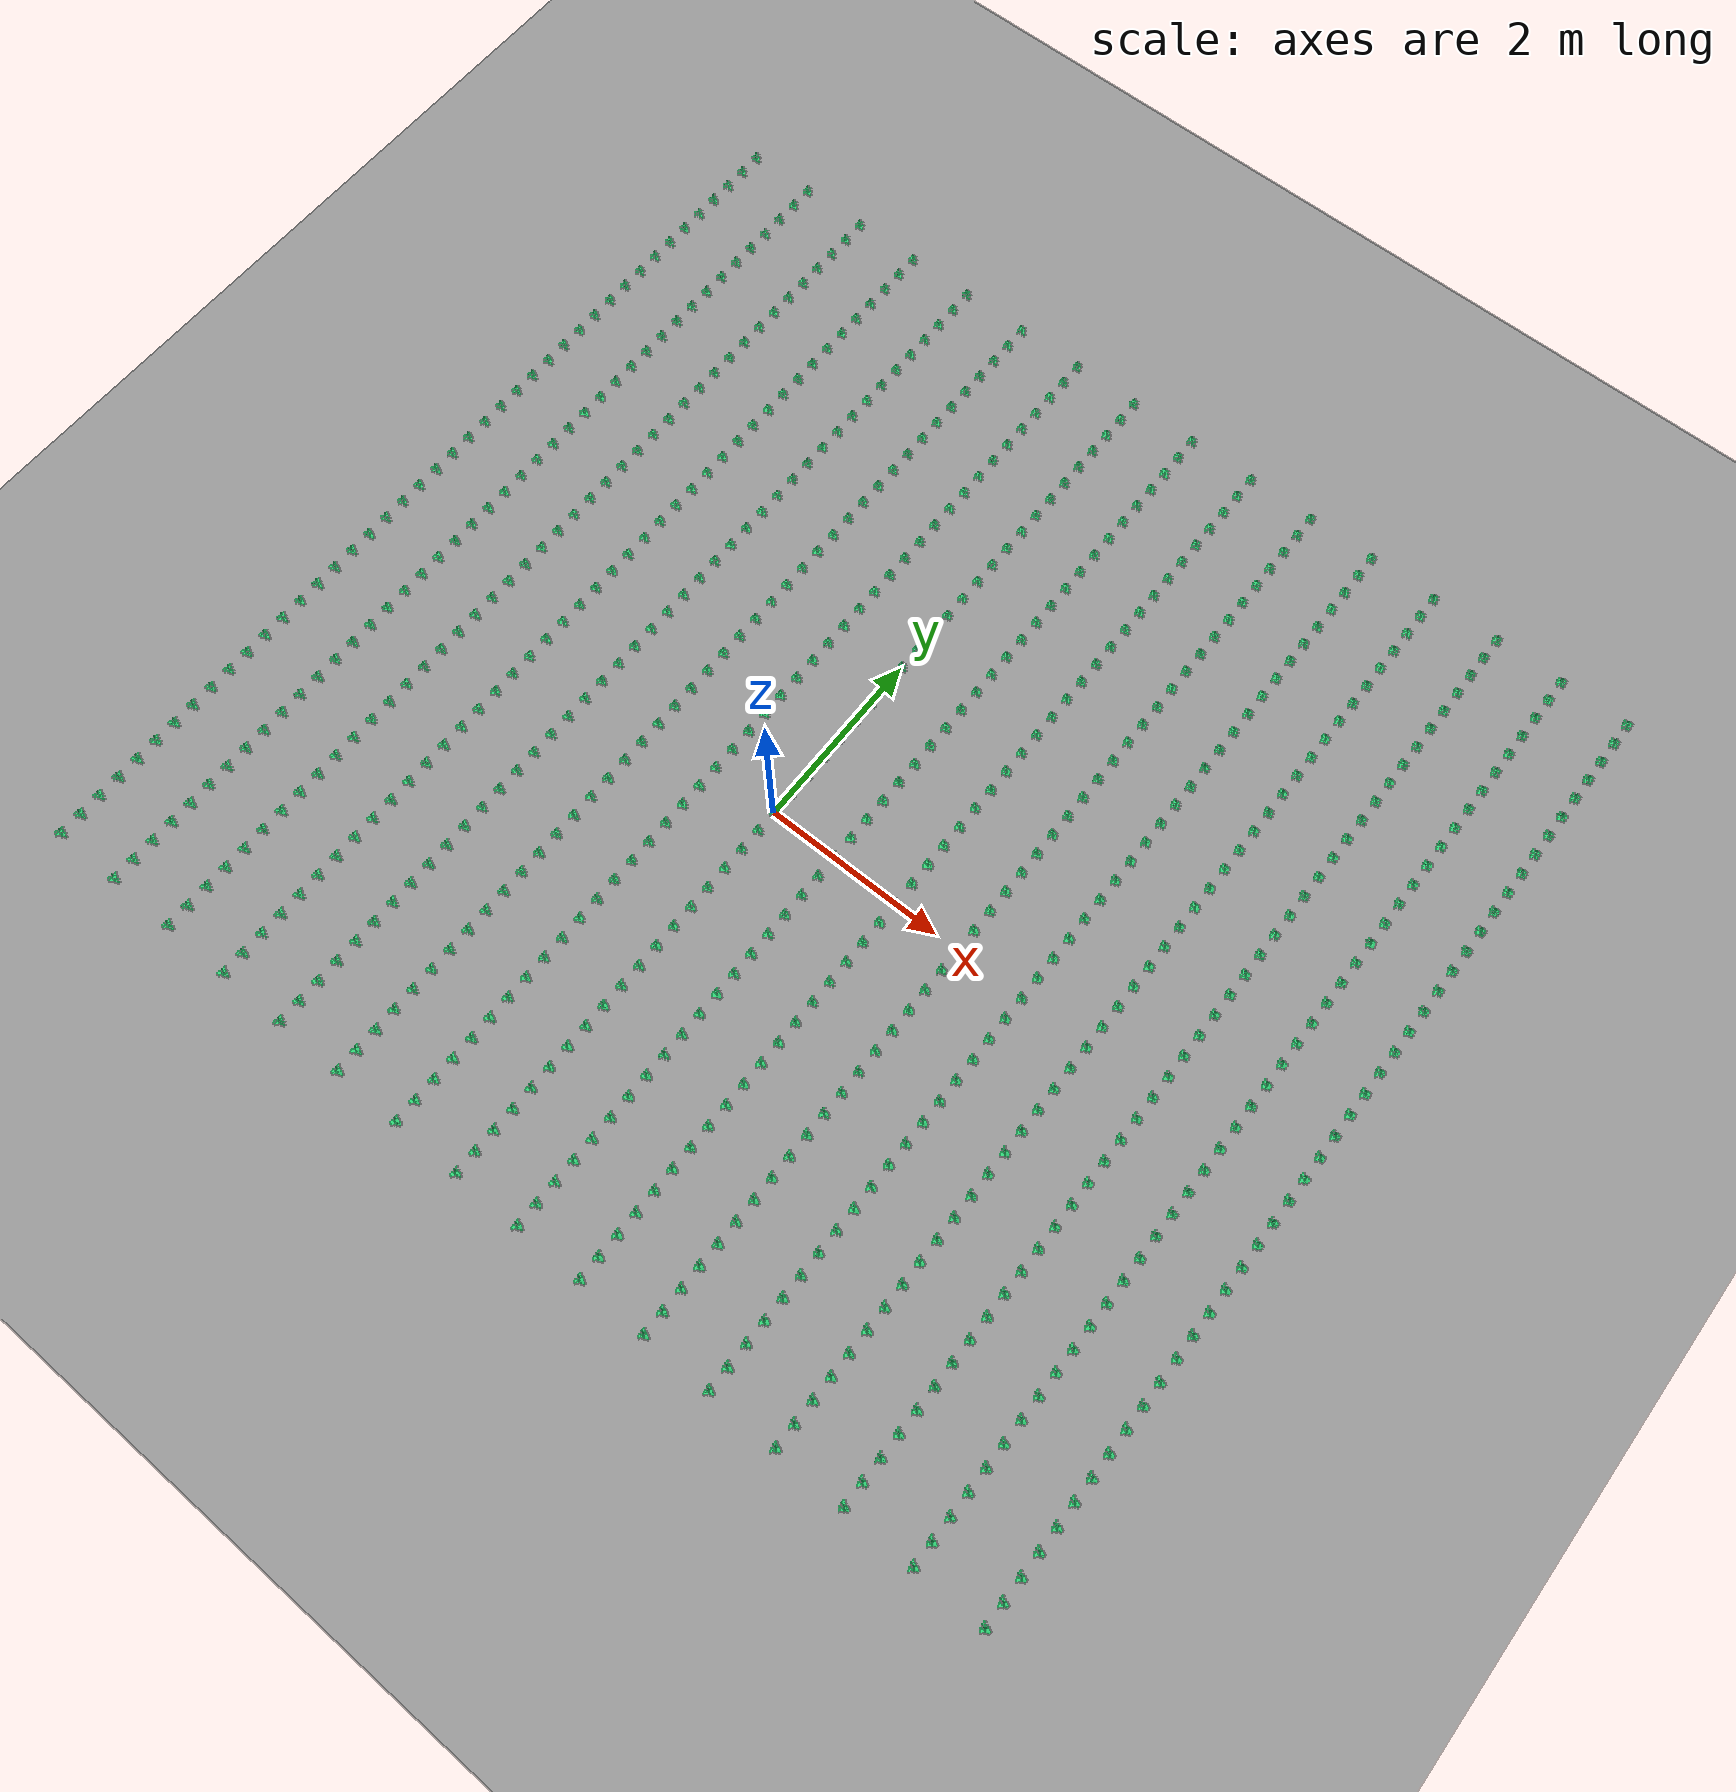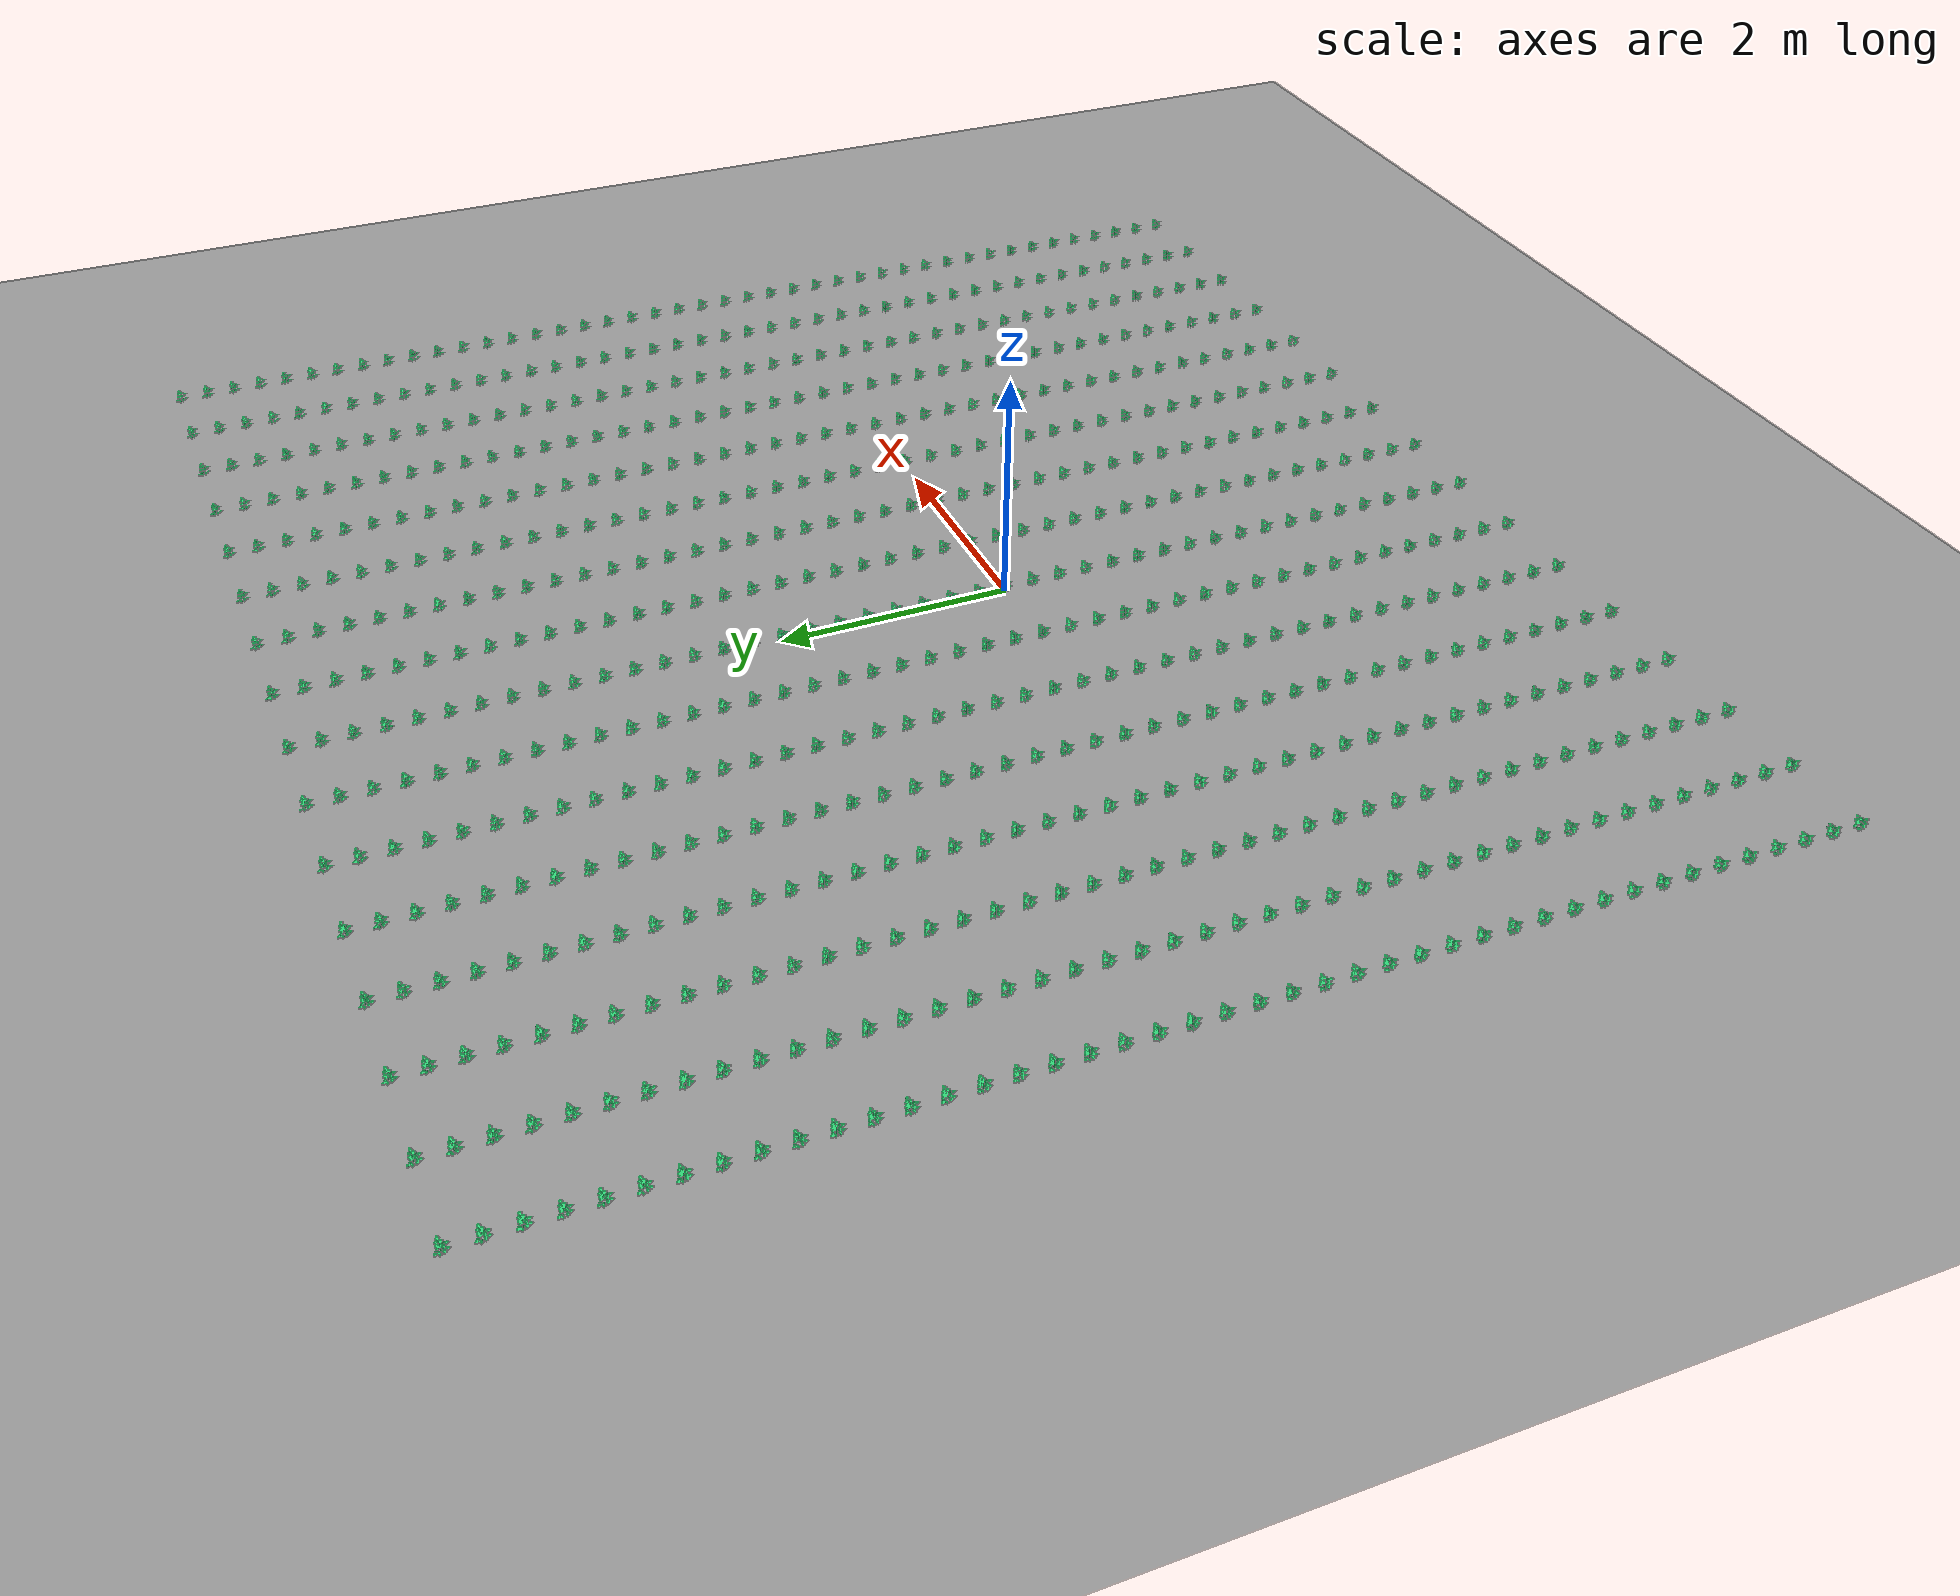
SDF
<?xml version='1.0' encoding='utf-8'?>
<sdf version="1.7">
  <world name="field">

    <static>true</static>

    <physics name="1ms" type="ignored">
      <max_step_size>0.001</max_step_size>
      <real_time_factor>0.7</real_time_factor>
      <real_time_update_rate>1000</real_time_update_rate>
    </physics>

    <plugin name="ignition::gazebo::systems::Physics" filename="ignition-gazebo-physics-system" />
    <plugin name="ignition::gazebo::systems::UserCommands" filename="ignition-gazebo-user-commands-system" />
    <plugin name="ignition::gazebo::systems::SceneBroadcaster" filename="ignition-gazebo-scene-broadcaster-system" />
    <plugin name="ignition::gazebo::systems::Sensors" filename="ignition-gazebo-sensors-system">
      <render_engine>ogre2</render_engine>
    </plugin>

    <scene>
      <ambient>1 1 1 1</ambient>
      <background>0.8 0.8 0.8 1</background>
      <shadows>1</shadows>
    </scene>

    <light name="sun" type="directional">
      <cast_shadows>1</cast_shadows>
      <pose>0 0 10 0 0 0</pose>
      <diffuse>0.8 0.8 0.8 1</diffuse>
      <specular>0.8 0.8 0.8 1</specular>
      <attenuation>
        <range>1000</range>
        <constant>0.9</constant>
        <linear>0.01</linear>
        <quadratic>0.001</quadratic>
      </attenuation>
      <direction>-0.5 0.1 -0.9</direction>
      <spot>
        <inner_angle>0</inner_angle>
        <outer_angle>0</outer_angle>
        <falloff>0</falloff>
      </spot>
    </light>

     <grid>off</grid>

    <include>
      <uri>model://field_ground_plane</uri>
      <pose>0 0 0 0 0 0</pose>
      <name>field_ground_plane_0_0</name>
    </include>

    <model name="static_video_camera">
      <static>true</static>

      <pose>-8 -4 2.5 0 0.5236 0</pose>

      <link name="camera_link">
        <sensor name="video_camera" type="camera">
          <always_on>true</always_on>
          <update_rate>30</update_rate>
          <visualize>false</visualize>

          <camera>
            <horizontal_fov>1.3962634</horizontal_fov>
            <image>
              <width>640</width>
              <height>320</height>
              <format>R8G8B8</format>
            </image>
            <clip><near>0.1</near><far>50</far></clip>
          </camera>

          <plugin name="ignition::gazebo::systems::CameraVideoRecorder" filename="ignition-gazebo6-camera-video-recorder-system">
            <service>/record_video_cmd</service>
            <fps>20</fps>
            <bitrate>3000000</bitrate>
            <use_sim_time>false</use_sim_time>
          </plugin>
        </sensor>
      </link>
    </model>

    <model name="crop1">
      <link name="crop_line">
        <static>true</static>
        <pose>0 0 0 0 0 0</pose>
        <collision name="collision">
          <geometry>
            <box>
              <size>0.2 0.2 0.2</size>
            </box>
          </geometry>
        </collision>

        <inertial>
          <mass>200000.0</mass>
          <inertia>
            <ixx>0.1</ixx>
            <iyy>0.1</iyy>
            <izz>0.1</izz>
            <ixy>0</ixy>
            <ixz>0</ixz>
            <iyz>0</iyz>
          </inertia>
        </inertial>

        <visual name="visual1">
      <pose>-5.250000000 -4.500000000 0.000000000 0.000000000 0.000000000 0.000000000</pose>
          <geometry>
            <mesh>
              <uri>file://very_low/plant_3.stl</uri>
              <scale>1 1 1</scale>
            </mesh>
          </geometry>
          <material>
            <diffuse>0.18 0.85 0.47 1.0</diffuse>
            <specular>0.01 0.01 0.01 1.0</specular>
            <ambient>0.13 0.60 0.33 1.0</ambient>
          </material>
          <cast_shadows>true</cast_shadows>
        </visual>

        <visual name="visual2">
      <pose>-5.250000000 -4.250000000 0.000000000 0.000000000 0.000000000 0.000000000</pose>
          <geometry>
            <mesh>
              <uri>file://very_low/plant_3.stl</uri>
            </mesh>
          </geometry>
          <material>
            <diffuse>0.18 0.85 0.47 1.0</diffuse>
            <specular>0.01 0.01 0.01 1.0</specular>
            <ambient>0.13 0.60 0.33 1.0</ambient>
          </material>
          <cast_shadows>true</cast_shadows>
        </visual>

        <visual name="visual3">
      <pose>-5.250000000 -4.000000000 0.000000000 0.000000000 0.000000000 0.000000000</pose>
          <geometry>
            <mesh>
              <uri>file://very_low/plant_3.stl</uri>
            </mesh>
          </geometry>
          <material>
            <diffuse>0.18 0.85 0.47 1.0</diffuse>
            <specular>0.01 0.01 0.01 1.0</specular>
            <ambient>0.13 0.60 0.33 1.0</ambient>
          </material>
          <cast_shadows>true</cast_shadows>
        </visual>

        <visual name="visual4">
      <pose>-5.250000000 -3.750000000 0.000000000 0.000000000 0.000000000 0.000000000</pose>
          <geometry>
            <mesh>
              <uri>file://very_low/plant_3.stl</uri>
            </mesh>
          </geometry>
          <material>
            <diffuse>0.18 0.85 0.47 1.0</diffuse>
            <specular>0.01 0.01 0.01 1.0</specular>
            <ambient>0.13 0.60 0.33 1.0</ambient>
          </material>
          <cast_shadows>true</cast_shadows>
        </visual>

        <visual name="visual5">
      <pose>-5.250000000 -3.500000000 0.000000000 0.000000000 0.000000000 0.000000000</pose>
          <geometry>
            <mesh>
              <uri>file://very_low/plant_3.stl</uri>
            </mesh>
          </geometry>
          <material>
            <diffuse>0.18 0.85 0.47 1.0</diffuse>
            <specular>0.01 0.01 0.01 1.0</specular>
            <ambient>0.13 0.60 0.33 1.0</ambient>
          </material>
          <cast_shadows>true</cast_shadows>
        </visual>

        <visual name="visual6">
      <pose>-5.250000000 -3.250000000 0.000000000 0.000000000 0.000000000 0.000000000</pose>
          <geometry>
            <mesh>
              <uri>file://very_low/plant_3.stl</uri>
            </mesh>
          </geometry>
          <material>
            <diffuse>0.18 0.85 0.47 1.0</diffuse>
            <specular>0.01 0.01 0.01 1.0</specular>
            <ambient>0.13 0.60 0.33 1.0</ambient>
          </material>
          <cast_shadows>true</cast_shadows>
        </visual>

        <visual name="visual7">
      <pose>-5.250000000 -3.000000000 0.000000000 0.000000000 0.000000000 0.000000000</pose>
          <geometry>
            <mesh>
              <uri>file://very_low/plant_3.stl</uri>
            </mesh>
          </geometry>
          <material>
            <diffuse>0.18 0.85 0.47 1.0</diffuse>
            <specular>0.01 0.01 0.01 1.0</specular>
            <ambient>0.13 0.60 0.33 1.0</ambient>
          </material>
          <cast_shadows>true</cast_shadows>
        </visual>

        <visual name="visual8">
      <pose>-5.250000000 -2.750000000 0.000000000 0.000000000 0.000000000 0.000000000</pose>
          <geometry>
            <mesh>
              <uri>file://very_low/plant_3.stl</uri>
            </mesh>
          </geometry>
          <material>
            <diffuse>0.18 0.85 0.47 1.0</diffuse>
            <specular>0.01 0.01 0.01 1.0</specular>
            <ambient>0.13 0.60 0.33 1.0</ambient>
          </material>
          <cast_shadows>true</cast_shadows>
        </visual>

        <visual name="visual9">
      <pose>-5.250000000 -2.500000000 0.000000000 0.000000000 0.000000000 0.000000000</pose>
          <geometry>
            <mesh>
              <uri>file://very_low/plant_3.stl</uri>
            </mesh>
          </geometry>
          <material>
            <diffuse>0.18 0.85 0.47 1.0</diffuse>
            <specular>0.01 0.01 0.01 1.0</specular>
            <ambient>0.13 0.60 0.33 1.0</ambient>
          </material>
          <cast_shadows>true</cast_shadows>
        </visual>

        <visual name="visual10">
      <pose>-5.250000000 -2.250000000 0.000000000 0.000000000 0.000000000 0.000000000</pose>
          <geometry>
            <mesh>
              <uri>file://very_low/plant_3.stl</uri>
            </mesh>
          </geometry>
          <material>
            <diffuse>0.18 0.85 0.47 1.0</diffuse>
            <specular>0.01 0.01 0.01 1.0</specular>
            <ambient>0.13 0.60 0.33 1.0</ambient>
          </material>
          <cast_shadows>true</cast_shadows>
        </visual>

        <visual name="visual11">
      <pose>-5.250000000 -2.000000000 0.000000000 0.000000000 0.000000000 0.000000000</pose>
          <geometry>
            <mesh>
              <uri>file://very_low/plant_3.stl</uri>
            </mesh>
          </geometry>
          <material>
            <diffuse>0.18 0.85 0.47 1.0</diffuse>
            <specular>0.01 0.01 0.01 1.0</specular>
            <ambient>0.13 0.60 0.33 1.0</ambient>
          </material>
          <cast_shadows>true</cast_shadows>
        </visual>

        <visual name="visual12">
      <pose>-5.250000000 -1.750000000 0.000000000 0.000000000 0.000000000 0.000000000</pose>
          <geometry>
            <mesh>
              <uri>file://very_low/plant_3.stl</uri>
            </mesh>
          </geometry>
          <material>
            <diffuse>0.18 0.85 0.47 1.0</diffuse>
            <specular>0.01 0.01 0.01 1.0</specular>
            <ambient>0.13 0.60 0.33 1.0</ambient>
          </material>
          <cast_shadows>true</cast_shadows>
        </visual>

        <visual name="visual13">
      <pose>-5.250000000 -1.500000000 0.000000000 0.000000000 0.000000000 0.000000000</pose>
          <geometry>
            <mesh>
              <uri>file://very_low/plant_3.stl</uri>
            </mesh>
          </geometry>
          <material>
            <diffuse>0.18 0.85 0.47 1.0</diffuse>
            <specular>0.01 0.01 0.01 1.0</specular>
            <ambient>0.13 0.60 0.33 1.0</ambient>
          </material>
          <cast_shadows>true</cast_shadows>
        </visual>

        <visual name="visual14">
      <pose>-5.250000000 -1.250000000 0.000000000 0.000000000 0.000000000 0.000000000</pose>
          <geometry>
            <mesh>
              <uri>file://very_low/plant_3.stl</uri>
            </mesh>
          </geometry>
          <material>
            <diffuse>0.18 0.85 0.47 1.0</diffuse>
            <specular>0.01 0.01 0.01 1.0</specular>
            <ambient>0.13 0.60 0.33 1.0</ambient>
          </material>
          <cast_shadows>true</cast_shadows>
        </visual>

        <visual name="visual15">
      <pose>-5.250000000 -1.000000000 0.000000000 0.000000000 0.000000000 0.000000000</pose>
          <geometry>
            <mesh>
              <uri>file://very_low/plant_3.stl</uri>
            </mesh>
          </geometry>
          <material>
            <diffuse>0.18 0.85 0.47 1.0</diffuse>
            <specular>0.01 0.01 0.01 1.0</specular>
            <ambient>0.13 0.60 0.33 1.0</ambient>
          </material>
          <cast_shadows>true</cast_shadows>
        </visual>

        <visual name="visual16">
      <pose>-5.250000000 -0.750000000 0.000000000 0.000000000 0.000000000 0.000000000</pose>
          <geometry>
            <mesh>
              <uri>file://very_low/plant_3.stl</uri>
            </mesh>
          </geometry>
          <material>
            <diffuse>0.18 0.85 0.47 1.0</diffuse>
            <specular>0.01 0.01 0.01 1.0</specular>
            <ambient>0.13 0.60 0.33 1.0</ambient>
          </material>
          <cast_shadows>true</cast_shadows>
        </visual>

        <visual name="visual17">
      <pose>-5.250000000 -0.500000000 0.000000000 0.000000000 0.000000000 0.000000000</pose>
          <geometry>
            <mesh>
              <uri>file://very_low/plant_3.stl</uri>
            </mesh>
          </geometry>
          <material>
            <diffuse>0.18 0.85 0.47 1.0</diffuse>
            <specular>0.01 0.01 0.01 1.0</specular>
            <ambient>0.13 0.60 0.33 1.0</ambient>
          </material>
          <cast_shadows>true</cast_shadows>
        </visual>

        <visual name="visual18">
      <pose>-5.250000000 -0.250000000 0.000000000 0.000000000 0.000000000 0.000000000</pose>
          <geometry>
            <mesh>
              <uri>file://very_low/plant_3.stl</uri>
            </mesh>
          </geometry>
          <material>
            <diffuse>0.18 0.85 0.47 1.0</diffuse>
            <specular>0.01 0.01 0.01 1.0</specular>
            <ambient>0.13 0.60 0.33 1.0</ambient>
          </material>
          <cast_shadows>true</cast_shadows>
        </visual>

        <visual name="visual19">
      <pose>-5.250000000 0.000000000 0.000000000 0.000000000 0.000000000 0.000000000</pose>
          <geometry>
            <mesh>
              <uri>file://very_low/plant_3.stl</uri>
            </mesh>
          </geometry>
          <material>
            <diffuse>0.18 0.85 0.47 1.0</diffuse>
            <specular>0.01 0.01 0.01 1.0</specular>
            <ambient>0.13 0.60 0.33 1.0</ambient>
          </material>
          <cast_shadows>true</cast_shadows>
        </visual>

        <visual name="visual20">
      <pose>-5.250000000 0.250000000 0.000000000 0.000000000 0.000000000 0.000000000</pose>
          <geometry>
            <mesh>
              <uri>file://very_low/plant_3.stl</uri>
            </mesh>
          </geometry>
          <material>
            <diffuse>0.18 0.85 0.47 1.0</diffuse>
            <specular>0.01 0.01 0.01 1.0</specular>
            <ambient>0.13 0.60 0.33 1.0</ambient>
          </material>
          <cast_shadows>true</cast_shadows>
        </visual>

        <visual name="visual21">
      <pose>-5.250000000 0.500000000 0.000000000 0.000000000 0.000000000 0.000000000</pose>
          <geometry>
            <mesh>
              <uri>file://very_low/plant_3.stl</uri>
            </mesh>
          </geometry>
          <material>
            <diffuse>0.18 0.85 0.47 1.0</diffuse>
            <specular>0.01 0.01 0.01 1.0</specular>
            <ambient>0.13 0.60 0.33 1.0</ambient>
          </material>
          <cast_shadows>true</cast_shadows>
        </visual>

        <visual name="visual22">
      <pose>-5.250000000 0.750000000 0.000000000 0.000000000 0.000000000 0.000000000</pose>
          <geometry>
            <mesh>
              <uri>file://very_low/plant_3.stl</uri>
            </mesh>
          </geometry>
          <material>
            <diffuse>0.18 0.85 0.47 1.0</diffuse>
            <specular>0.01 0.01 0.01 1.0</specular>
            <ambient>0.13 0.60 0.33 1.0</ambient>
          </material>
          <cast_shadows>true</cast_shadows>
        </visual>

        <visual name="visual23">
      <pose>-5.250000000 1.000000000 0.000000000 0.000000000 0.000000000 0.000000000</pose>
          <geometry>
            <mesh>
              <uri>file://very_low/plant_3.stl</uri>
            </mesh>
          </geometry>
          <material>
            <diffuse>0.18 0.85 0.47 1.0</diffuse>
            <specular>0.01 0.01 0.01 1.0</specular>
            <ambient>0.13 0.60 0.33 1.0</ambient>
          </material>
          <cast_shadows>true</cast_shadows>
        </visual>

        <visual name="visual24">
      <pose>-5.250000000 1.250000000 0.000000000 0.000000000 0.000000000 0.000000000</pose>
          <geometry>
            <mesh>
              <uri>file://very_low/plant_3.stl</uri>
            </mesh>
          </geometry>
          <material>
            <diffuse>0.18 0.85 0.47 1.0</diffuse>
            <specular>0.01 0.01 0.01 1.0</specular>
            <ambient>0.13 0.60 0.33 1.0</ambient>
          </material>
          <cast_shadows>true</cast_shadows>
        </visual>

        <visual name="visual25">
      <pose>-5.250000000 1.500000000 0.000000000 0.000000000 0.000000000 0.000000000</pose>
          <geometry>
            <mesh>
              <uri>file://very_low/plant_3.stl</uri>
            </mesh>
          </geometry>
          <material>
            <diffuse>0.18 0.85 0.47 1.0</diffuse>
            <specular>0.01 0.01 0.01 1.0</specular>
            <ambient>0.13 0.60 0.33 1.0</ambient>
          </material>
          <cast_shadows>true</cast_shadows>
        </visual>

        <visual name="visual26">
      <pose>-5.250000000 1.750000000 0.000000000 0.000000000 0.000000000 0.000000000</pose>
          <geometry>
            <mesh>
              <uri>file://very_low/plant_3.stl</uri>
            </mesh>
          </geometry>
          <material>
            <diffuse>0.18 0.85 0.47 1.0</diffuse>
            <specular>0.01 0.01 0.01 1.0</specular>
            <ambient>0.13 0.60 0.33 1.0</ambient>
          </material>
          <cast_shadows>true</cast_shadows>
        </visual>

        <visual name="visual27">
      <pose>-5.250000000 2.000000000 0.000000000 0.000000000 0.000000000 0.000000000</pose>
          <geometry>
            <mesh>
              <uri>file://very_low/plant_3.stl</uri>
            </mesh>
          </geometry>
          <material>
            <diffuse>0.18 0.85 0.47 1.0</diffuse>
            <specular>0.01 0.01 0.01 1.0</specular>
            <ambient>0.13 0.60 0.33 1.0</ambient>
          </material>
          <cast_shadows>true</cast_shadows>
        </visual>

        <visual name="visual28">
      <pose>-5.250000000 2.250000000 0.000000000 0.000000000 0.000000000 0.000000000</pose>
          <geometry>
            <mesh>
              <uri>file://very_low/plant_3.stl</uri>
            </mesh>
          </geometry>
          <material>
            <diffuse>0.18 0.85 0.47 1.0</diffuse>
            <specular>0.01 0.01 0.01 1.0</specular>
            <ambient>0.13 0.60 0.33 1.0</ambient>
          </material>
          <cast_shadows>true</cast_shadows>
        </visual>

        <visual name="visual29">
      <pose>-5.250000000 2.500000000 0.000000000 0.000000000 0.000000000 0.000000000</pose>
          <geometry>
            <mesh>
              <uri>file://very_low/plant_3.stl</uri>
            </mesh>
          </geometry>
          <material>
            <diffuse>0.18 0.85 0.47 1.0</diffuse>
            <specular>0.01 0.01 0.01 1.0</specular>
            <ambient>0.13 0.60 0.33 1.0</ambient>
          </material>
          <cast_shadows>true</cast_shadows>
        </visual>

        <visual name="visual30">
      <pose>-5.250000000 2.750000000 0.000000000 0.000000000 0.000000000 0.000000000</pose>
          <geometry>
            <mesh>
              <uri>file://very_low/plant_3.stl</uri>
            </mesh>
          </geometry>
          <material>
            <diffuse>0.18 0.85 0.47 1.0</diffuse>
            <specular>0.01 0.01 0.01 1.0</specular>
            <ambient>0.13 0.60 0.33 1.0</ambient>
          </material>
          <cast_shadows>true</cast_shadows>
        </visual>

        <visual name="visual31">
      <pose>-5.250000000 3.000000000 0.000000000 0.000000000 0.000000000 0.000000000</pose>
          <geometry>
            <mesh>
              <uri>file://very_low/plant_3.stl</uri>
            </mesh>
          </geometry>
          <material>
            <diffuse>0.18 0.85 0.47 1.0</diffuse>
            <specular>0.01 0.01 0.01 1.0</specular>
            <ambient>0.13 0.60 0.33 1.0</ambient>
          </material>
          <cast_shadows>true</cast_shadows>
        </visual>

        <visual name="visual32">
      <pose>-5.250000000 3.250000000 0.000000000 0.000000000 0.000000000 0.000000000</pose>
          <geometry>
            <mesh>
              <uri>file://very_low/plant_3.stl</uri>
            </mesh>
          </geometry>
          <material>
            <diffuse>0.18 0.85 0.47 1.0</diffuse>
            <specular>0.01 0.01 0.01 1.0</specular>
            <ambient>0.13 0.60 0.33 1.0</ambient>
          </material>
          <cast_shadows>true</cast_shadows>
        </visual>

        <visual name="visual33">
      <pose>-5.250000000 3.500000000 0.000000000 0.000000000 0.000000000 0.000000000</pose>
          <geometry>
            <mesh>
              <uri>file://very_low/plant_3.stl</uri>
            </mesh>
          </geometry>
          <material>
            <diffuse>0.18 0.85 0.47 1.0</diffuse>
            <specular>0.01 0.01 0.01 1.0</specular>
            <ambient>0.13 0.60 0.33 1.0</ambient>
          </material>
          <cast_shadows>true</cast_shadows>
        </visual>

        <visual name="visual34">
      <pose>-5.250000000 3.750000000 0.000000000 0.000000000 0.000000000 0.000000000</pose>
          <geometry>
            <mesh>
              <uri>file://very_low/plant_3.stl</uri>
            </mesh>
          </geometry>
          <material>
            <diffuse>0.18 0.85 0.47 1.0</diffuse>
            <specular>0.01 0.01 0.01 1.0</specular>
            <ambient>0.13 0.60 0.33 1.0</ambient>
          </material>
          <cast_shadows>true</cast_shadows>
        </visual>

        <visual name="visual35">
      <pose>-5.250000000 4.000000000 0.000000000 0.000000000 0.000000000 0.000000000</pose>
          <geometry>
            <mesh>
              <uri>file://very_low/plant_3.stl</uri>
            </mesh>
          </geometry>
          <material>
            <diffuse>0.18 0.85 0.47 1.0</diffuse>
            <specular>0.01 0.01 0.01 1.0</specular>
            <ambient>0.13 0.60 0.33 1.0</ambient>
          </material>
          <cast_shadows>true</cast_shadows>
        </visual>

        <visual name="visual36">
      <pose>-5.250000000 4.250000000 0.000000000 0.000000000 0.000000000 0.000000000</pose>
          <geometry>
            <mesh>
              <uri>file://very_low/plant_3.stl</uri>
            </mesh>
          </geometry>
          <material>
            <diffuse>0.18 0.85 0.47 1.0</diffuse>
            <specular>0.01 0.01 0.01 1.0</specular>
            <ambient>0.13 0.60 0.33 1.0</ambient>
          </material>
          <cast_shadows>true</cast_shadows>
        </visual>

        <visual name="visual37">
      <pose>-5.250000000 4.500000000 0.000000000 0.000000000 0.000000000 0.000000000</pose>
          <geometry>
            <mesh>
              <uri>file://very_low/plant_3.stl</uri>
            </mesh>
          </geometry>
          <material>
            <diffuse>0.18 0.85 0.47 1.0</diffuse>
            <specular>0.01 0.01 0.01 1.0</specular>
            <ambient>0.13 0.60 0.33 1.0</ambient>
          </material>
          <cast_shadows>true</cast_shadows>
        </visual>

        <visual name="visual38">
      <pose>-5.250000000 4.750000000 0.000000000 0.000000000 0.000000000 0.000000000</pose>
          <geometry>
            <mesh>
              <uri>file://very_low/plant_3.stl</uri>
            </mesh>
          </geometry>
          <material>
            <diffuse>0.18 0.85 0.47 1.0</diffuse>
            <specular>0.01 0.01 0.01 1.0</specular>
            <ambient>0.13 0.60 0.33 1.0</ambient>
          </material>
          <cast_shadows>true</cast_shadows>
        </visual>

        <visual name="visual39">
      <pose>-5.250000000 5.000000000 0.000000000 0.000000000 0.000000000 0.000000000</pose>
          <geometry>
            <mesh>
              <uri>file://very_low/plant_3.stl</uri>
            </mesh>
          </geometry>
          <material>
            <diffuse>0.18 0.85 0.47 1.0</diffuse>
            <specular>0.01 0.01 0.01 1.0</specular>
            <ambient>0.13 0.60 0.33 1.0</ambient>
          </material>
          <cast_shadows>true</cast_shadows>
        </visual>

        <visual name="visual40">
      <pose>-5.250000000 5.250000000 0.000000000 0.000000000 0.000000000 0.000000000</pose>
          <geometry>
            <mesh>
              <uri>file://very_low/plant_3.stl</uri>
            </mesh>
          </geometry>
          <material>
            <diffuse>0.18 0.85 0.47 1.0</diffuse>
            <specular>0.01 0.01 0.01 1.0</specular>
            <ambient>0.13 0.60 0.33 1.0</ambient>
          </material>
          <cast_shadows>true</cast_shadows>
        </visual>

        <visual name="visual41">
      <pose>-5.250000000 5.500000000 0.000000000 0.000000000 0.000000000 0.000000000</pose>
          <geometry>
            <mesh>
              <uri>file://very_low/plant_3.stl</uri>
            </mesh>
          </geometry>
          <material>
            <diffuse>0.18 0.85 0.47 1.0</diffuse>
            <specular>0.01 0.01 0.01 1.0</specular>
            <ambient>0.13 0.60 0.33 1.0</ambient>
          </material>
          <cast_shadows>true</cast_shadows>
        </visual>

        <visual name="visual42">
      <pose>-5.250000000 5.750000000 0.000000000 0.000000000 0.000000000 0.000000000</pose>
          <geometry>
            <mesh>
              <uri>file://very_low/plant_3.stl</uri>
            </mesh>
          </geometry>
          <material>
            <diffuse>0.18 0.85 0.47 1.0</diffuse>
            <specular>0.01 0.01 0.01 1.0</specular>
            <ambient>0.13 0.60 0.33 1.0</ambient>
          </material>
          <cast_shadows>true</cast_shadows>
        </visual>

        <visual name="visual43">
      <pose>-5.250000000 6.000000000 0.000000000 0.000000000 0.000000000 0.000000000</pose>
          <geometry>
            <mesh>
              <uri>file://very_low/plant_3.stl</uri>
            </mesh>
          </geometry>
          <material>
            <diffuse>0.18 0.85 0.47 1.0</diffuse>
            <specular>0.01 0.01 0.01 1.0</specular>
            <ambient>0.13 0.60 0.33 1.0</ambient>
          </material>
          <cast_shadows>true</cast_shadows>
        </visual>

        <visual name="visual44">
      <pose>-4.500000000 -4.500000000 0.000000000 0.000000000 0.000000000 0.000000000</pose>
          <geometry>
            <mesh>
              <uri>file://very_low/plant_3.stl</uri>
            </mesh>
          </geometry>
          <material>
            <diffuse>0.18 0.85 0.47 1.0</diffuse>
            <specular>0.01 0.01 0.01 1.0</specular>
            <ambient>0.13 0.60 0.33 1.0</ambient>
          </material>
          <cast_shadows>true</cast_shadows>
        </visual>

        <visual name="visual45">
      <pose>-4.500000000 -4.250000000 0.000000000 0.000000000 0.000000000 0.000000000</pose>
          <geometry>
            <mesh>
              <uri>file://very_low/plant_3.stl</uri>
            </mesh>
          </geometry>
          <material>
            <diffuse>0.18 0.85 0.47 1.0</diffuse>
            <specular>0.01 0.01 0.01 1.0</specular>
            <ambient>0.13 0.60 0.33 1.0</ambient>
          </material>
          <cast_shadows>true</cast_shadows>
        </visual>

        <visual name="visual46">
      <pose>-4.500000000 -4.000000000 0.000000000 0.000000000 0.000000000 0.000000000</pose>
          <geometry>
            <mesh>
              <uri>file://very_low/plant_3.stl</uri>
            </mesh>
          </geometry>
          <material>
            <diffuse>0.18 0.85 0.47 1.0</diffuse>
            <specular>0.01 0.01 0.01 1.0</specular>
            <ambient>0.13 0.60 0.33 1.0</ambient>
          </material>
          <cast_shadows>true</cast_shadows>
        </visual>

        <visual name="visual47">
      <pose>-4.500000000 -3.750000000 0.000000000 0.000000000 0.000000000 0.000000000</pose>
          <geometry>
            <mesh>
              <uri>file://very_low/plant_3.stl</uri>
            </mesh>
          </geometry>
          <material>
            <diffuse>0.18 0.85 0.47 1.0</diffuse>
            <specular>0.01 0.01 0.01 1.0</specular>
            <ambient>0.13 0.60 0.33 1.0</ambient>
          </material>
          <cast_shadows>true</cast_shadows>
        </visual>

        <visual name="visual48">
      <pose>-4.500000000 -3.500000000 0.000000000 0.000000000 0.000000000 0.000000000</pose>
          <geometry>
            <mesh>
              <uri>file://very_low/plant_3.stl</uri>
            </mesh>
          </geometry>
          <material>
            <diffuse>0.18 0.85 0.47 1.0</diffuse>
            <specular>0.01 0.01 0.01 1.0</specular>
            <ambient>0.13 0.60 0.33 1.0</ambient>
          </material>
          <cast_shadows>true</cast_shadows>
        </visual>

        <visual name="visual49">
      <pose>-4.500000000 -3.250000000 0.000000000 0.000000000 0.000000000 0.000000000</pose>
          <geometry>
            <mesh>
              <uri>file://very_low/plant_3.stl</uri>
            </mesh>
          </geometry>
          <material>
            <diffuse>0.18 0.85 0.47 1.0</diffuse>
            <specular>0.01 0.01 0.01 1.0</specular>
            <ambient>0.13 0.60 0.33 1.0</ambient>
          </material>
          <cast_shadows>true</cast_shadows>
        </visual>

        <visual name="visual50">
      <pose>-4.500000000 -3.000000000 0.000000000 0.000000000 0.000000000 0.000000000</pose>
          <geometry>
            <mesh>
              <uri>file://very_low/plant_3.stl</uri>
            </mesh>
          </geometry>
          <material>
            <diffuse>0.18 0.85 0.47 1.0</diffuse>
            <specular>0.01 0.01 0.01 1.0</specular>
            <ambient>0.13 0.60 0.33 1.0</ambient>
          </material>
          <cast_shadows>true</cast_shadows>
        </visual>

        <visual name="visual51">
      <pose>-4.500000000 -2.750000000 0.000000000 0.000000000 0.000000000 0.000000000</pose>
          <geometry>
            <mesh>
              <uri>file://very_low/plant_3.stl</uri>
            </mesh>
          </geometry>
          <material>
            <diffuse>0.18 0.85 0.47 1.0</diffuse>
            <specular>0.01 0.01 0.01 1.0</specular>
            <ambient>0.13 0.60 0.33 1.0</ambient>
          </material>
          <cast_shadows>true</cast_shadows>
        </visual>

        <visual name="visual52">
      <pose>-4.500000000 -2.500000000 0.000000000 0.000000000 0.000000000 0.000000000</pose>
          <geometry>
            <mesh>
              <uri>file://very_low/plant_3.stl</uri>
            </mesh>
          </geometry>
          <material>
            <diffuse>0.18 0.85 0.47 1.0</diffuse>
            <specular>0.01 0.01 0.01 1.0</specular>
            <ambient>0.13 0.60 0.33 1.0</ambient>
          </material>
          <cast_shadows>true</cast_shadows>
        </visual>

        <visual name="visual53">
      <pose>-4.500000000 -2.250000000 0.000000000 0.000000000 0.000000000 0.000000000</pose>
          <geometry>
            <mesh>
              <uri>file://very_low/plant_3.stl</uri>
            </mesh>
          </geometry>
          <material>
            <diffuse>0.18 0.85 0.47 1.0</diffuse>
            <specular>0.01 0.01 0.01 1.0</specular>
            <ambient>0.13 0.60 0.33 1.0</ambient>
          </material>
          <cast_shadows>true</cast_shadows>
        </visual>

        <visual name="visual54">
      <pose>-4.500000000 -2.000000000 0.000000000 0.000000000 0.000000000 0.000000000</pose>
          <geometry>
            <mesh>
              <uri>file://very_low/plant_3.stl</uri>
            </mesh>
          </geometry>
          <material>
            <diffuse>0.18 0.85 0.47 1.0</diffuse>
            <specular>0.01 0.01 0.01 1.0</specular>
            <ambient>0.13 0.60 0.33 1.0</ambient>
          </material>
          <cast_shadows>true</cast_shadows>
        </visual>

        <visual name="visual55">
      <pose>-4.500000000 -1.750000000 0.000000000 0.000000000 0.000000000 0.000000000</pose>
          <geometry>
            <mesh>
              <uri>file://very_low/plant_3.stl</uri>
            </mesh>
          </geometry>
          <material>
            <diffuse>0.18 0.85 0.47 1.0</diffuse>
            <specular>0.01 0.01 0.01 1.0</specular>
            <ambient>0.13 0.60 0.33 1.0</ambient>
          </material>
          <cast_shadows>true</cast_shadows>
        </visual>

        <visual name="visual56">
      <pose>-4.500000000 -1.500000000 0.000000000 0.000000000 0.000000000 0.000000000</pose>
          <geometry>
            <mesh>
              <uri>file://very_low/plant_3.stl</uri>
            </mesh>
          </geometry>
          <material>
            <diffuse>0.18 0.85 0.47 1.0</diffuse>
            <specular>0.01 0.01 0.01 1.0</specular>
            <ambient>0.13 0.60 0.33 1.0</ambient>
          </material>
          <cast_shadows>true</cast_shadows>
        </visual>

        <visual name="visual57">
      <pose>-4.500000000 -1.250000000 0.000000000 0.000000000 0.000000000 0.000000000</pose>
          <geometry>
            <mesh>
              <uri>file://very_low/plant_3.stl</uri>
            </mesh>
          </geometry>
          <material>
            <diffuse>0.18 0.85 0.47 1.0</diffuse>
            <specular>0.01 0.01 0.01 1.0</specular>
            <ambient>0.13 0.60 0.33 1.0</ambient>
          </material>
          <cast_shadows>true</cast_shadows>
        </visual>

        <visual name="visual58">
      <pose>-4.500000000 -1.000000000 0.000000000 0.000000000 0.000000000 0.000000000</pose>
          <geometry>
            <mesh>
              <uri>file://very_low/plant_3.stl</uri>
            </mesh>
          </geometry>
          <material>
            <diffuse>0.18 0.85 0.47 1.0</diffuse>
            <specular>0.01 0.01 0.01 1.0</specular>
            <ambient>0.13 0.60 0.33 1.0</ambient>
          </material>
          <cast_shadows>true</cast_shadows>
        </visual>

        <visual name="visual59">
      <pose>-4.500000000 -0.750000000 0.000000000 0.000000000 0.000000000 0.000000000</pose>
          <geometry>
            <mesh>
              <uri>file://very_low/plant_3.stl</uri>
            </mesh>
          </geometry>
          <material>
            <diffuse>0.18 0.85 0.47 1.0</diffuse>
            <specular>0.01 0.01 0.01 1.0</specular>
            <ambient>0.13 0.60 0.33 1.0</ambient>
          </material>
          <cast_shadows>true</cast_shadows>
        </visual>

        <visual name="visual60">
      <pose>-4.500000000 -0.500000000 0.000000000 0.000000000 0.000000000 0.000000000</pose>
          <geometry>
            <mesh>
              <uri>file://very_low/plant_3.stl</uri>
            </mesh>
          </geometry>
          <material>
            <diffuse>0.18 0.85 0.47 1.0</diffuse>
            <specular>0.01 0.01 0.01 1.0</specular>
            <ambient>0.13 0.60 0.33 1.0</ambient>
          </material>
          <cast_shadows>true</cast_shadows>
        </visual>

        <visual name="visual61">
      <pose>-4.500000000 -0.250000000 0.000000000 0.000000000 0.000000000 0.000000000</pose>
          <geometry>
            <mesh>
              <uri>file://very_low/plant_3.stl</uri>
            </mesh>
          </geometry>
          <material>
            <diffuse>0.18 0.85 0.47 1.0</diffuse>
            <specular>0.01 0.01 0.01 1.0</specular>
            <ambient>0.13 0.60 0.33 1.0</ambient>
          </material>
          <cast_shadows>true</cast_shadows>
        </visual>

        <visual name="visual62">
      <pose>-4.500000000 0.000000000 0.000000000 0.000000000 0.000000000 0.000000000</pose>
          <geometry>
            <mesh>
              <uri>file://very_low/plant_3.stl</uri>
            </mesh>
          </geometry>
          <material>
            <diffuse>0.18 0.85 0.47 1.0</diffuse>
            <specular>0.01 0.01 0.01 1.0</specular>
            <ambient>0.13 0.60 0.33 1.0</ambient>
          </material>
          <cast_shadows>true</cast_shadows>
        </visual>

        <visual name="visual63">
      <pose>-4.500000000 0.250000000 0.000000000 0.000000000 0.000000000 0.000000000</pose>
          <geometry>
            <mesh>
              <uri>file://very_low/plant_3.stl</uri>
            </mesh>
          </geometry>
          <material>
            <diffuse>0.18 0.85 0.47 1.0</diffuse>
            <specular>0.01 0.01 0.01 1.0</specular>
            <ambient>0.13 0.60 0.33 1.0</ambient>
          </material>
          <cast_shadows>true</cast_shadows>
        </visual>

        <visual name="visual64">
      <pose>-4.500000000 0.500000000 0.000000000 0.000000000 0.000000000 0.000000000</pose>
          <geometry>
            <mesh>
              <uri>file://very_low/plant_3.stl</uri>
            </mesh>
          </geometry>
          <material>
            <diffuse>0.18 0.85 0.47 1.0</diffuse>
            <specular>0.01 0.01 0.01 1.0</specular>
            <ambient>0.13 0.60 0.33 1.0</ambient>
          </material>
          <cast_shadows>true</cast_shadows>
        </visual>

        <visual name="visual65">
      <pose>-4.500000000 0.750000000 0.000000000 0.000000000 0.000000000 0.000000000</pose>
          <geometry>
            <mesh>
              <uri>file://very_low/plant_3.stl</uri>
            </mesh>
          </geometry>
          <material>
            <diffuse>0.18 0.85 0.47 1.0</diffuse>
            <specular>0.01 0.01 0.01 1.0</specular>
            <ambient>0.13 0.60 0.33 1.0</ambient>
          </material>
          <cast_shadows>true</cast_shadows>
        </visual>

        <visual name="visual66">
      <pose>-4.500000000 1.000000000 0.000000000 0.000000000 0.000000000 0.000000000</pose>
          <geometry>
            <mesh>
              <uri>file://very_low/plant_3.stl</uri>
            </mesh>
          </geometry>
          <material>
            <diffuse>0.18 0.85 0.47 1.0</diffuse>
            <specular>0.01 0.01 0.01 1.0</specular>
            <ambient>0.13 0.60 0.33 1.0</ambient>
          </material>
          <cast_shadows>true</cast_shadows>
        </visual>

        <visual name="visual67">
      <pose>-4.500000000 1.250000000 0.000000000 0.000000000 0.000000000 0.000000000</pose>
          <geometry>
            <mesh>
              <uri>file://very_low/plant_3.stl</uri>
            </mesh>
          </geometry>
          <material>
            <diffuse>0.18 0.85 0.47 1.0</diffuse>
            <specular>0.01 0.01 0.01 1.0</specular>
            <ambient>0.13 0.60 0.33 1.0</ambient>
          </material>
          <cast_shadows>true</cast_shadows>
        </visual>

        <visual name="visual68">
      <pose>-4.500000000 1.500000000 0.000000000 0.000000000 0.000000000 0.000000000</pose>
          <geometry>
            <mesh>
              <uri>file://very_low/plant_3.stl</uri>
            </mesh>
          </geometry>
          <material>
            <diffuse>0.18 0.85 0.47 1.0</diffuse>
            <specular>0.01 0.01 0.01 1.0</specular>
            <ambient>0.13 0.60 0.33 1.0</ambient>
          </material>
          <cast_shadows>true</cast_shadows>
        </visual>

        <visual name="visual69">
      <pose>-4.500000000 1.750000000 0.000000000 0.000000000 0.000000000 0.000000000</pose>
          <geometry>
            <mesh>
              <uri>file://very_low/plant_3.stl</uri>
            </mesh>
          </geometry>
          <material>
            <diffuse>0.18 0.85 0.47 1.0</diffuse>
            <specular>0.01 0.01 0.01 1.0</specular>
            <ambient>0.13 0.60 0.33 1.0</ambient>
          </material>
          <cast_shadows>true</cast_shadows>
        </visual>

        <visual name="visual70">
      <pose>-4.500000000 2.000000000 0.000000000 0.000000000 0.000000000 0.000000000</pose>
          <geometry>
            <mesh>
              <uri>file://very_low/plant_3.stl</uri>
            </mesh>
          </geometry>
          <material>
            <diffuse>0.18 0.85 0.47 1.0</diffuse>
            <specular>0.01 0.01 0.01 1.0</specular>
            <ambient>0.13 0.60 0.33 1.0</ambient>
          </material>
          <cast_shadows>true</cast_shadows>
        </visual>

        <visual name="visual71">
      <pose>-4.500000000 2.250000000 0.000000000 0.000000000 0.000000000 0.000000000</pose>
          <geometry>
            <mesh>
              <uri>file://very_low/plant_3.stl</uri>
            </mesh>
          </geometry>
          <material>
            <diffuse>0.18 0.85 0.47 1.0</diffuse>
            <specular>0.01 0.01 0.01 1.0</specular>
            <ambient>0.13 0.60 0.33 1.0</ambient>
          </material>
          <cast_shadows>true</cast_shadows>
        </visual>

        <visual name="visual72">
      <pose>-4.500000000 2.500000000 0.000000000 0.000000000 0.000000000 0.000000000</pose>
          <geometry>
            <mesh>
              <uri>file://very_low/plant_3.stl</uri>
            </mesh>
          </geometry>
          <material>
            <diffuse>0.18 0.85 0.47 1.0</diffuse>
            <specular>0.01 0.01 0.01 1.0</specular>
            <ambient>0.13 0.60 0.33 1.0</ambient>
          </material>
          <cast_shadows>true</cast_shadows>
        </visual>

        <visual name="visual73">
      <pose>-4.500000000 2.750000000 0.000000000 0.000000000 0.000000000 0.000000000</pose>
          <geometry>
            <mesh>
              <uri>file://very_low/plant_3.stl</uri>
            </mesh>
          </geometry>
          <material>
            <diffuse>0.18 0.85 0.47 1.0</diffuse>
            <specular>0.01 0.01 0.01 1.0</specular>
            <ambient>0.13 0.60 0.33 1.0</ambient>
          </material>
          <cast_shadows>true</cast_shadows>
        </visual>

        <visual name="visual74">
      <pose>-4.500000000 3.000000000 0.000000000 0.000000000 0.000000000 0.000000000</pose>
          <geometry>
            <mesh>
              <uri>file://very_low/plant_3.stl</uri>
            </mesh>
          </geometry>
          <material>
            <diffuse>0.18 0.85 0.47 1.0</diffuse>
            <specular>0.01 0.01 0.01 1.0</specular>
            <ambient>0.13 0.60 0.33 1.0</ambient>
          </material>
          <cast_shadows>true</cast_shadows>
        </visual>

        <visual name="visual75">
      <pose>-4.500000000 3.250000000 0.000000000 0.000000000 0.000000000 0.000000000</pose>
          <geometry>
            <mesh>
              <uri>file://very_low/plant_3.stl</uri>
            </mesh>
          </geometry>
          <material>
            <diffuse>0.18 0.85 0.47 1.0</diffuse>
            <specular>0.01 0.01 0.01 1.0</specular>
            <ambient>0.13 0.60 0.33 1.0</ambient>
          </material>
          <cast_shadows>true</cast_shadows>
        </visual>

        <visual name="visual76">
      <pose>-4.500000000 3.500000000 0.000000000 0.000000000 0.000000000 0.000000000</pose>
          <geometry>
            <mesh>
              <uri>file://very_low/plant_3.stl</uri>
            </mesh>
          </geometry>
          <material>
            <diffuse>0.18 0.85 0.47 1.0</diffuse>
            <specular>0.01 0.01 0.01 1.0</specular>
            <ambient>0.13 0.60 0.33 1.0</ambient>
          </material>
          <cast_shadows>true</cast_shadows>
        </visual>

        <visual name="visual77">
      <pose>-4.500000000 3.750000000 0.000000000 0.000000000 0.000000000 0.000000000</pose>
          <geometry>
            <mesh>
              <uri>file://very_low/plant_3.stl</uri>
            </mesh>
          </geometry>
          <material>
            <diffuse>0.18 0.85 0.47 1.0</diffuse>
            <specular>0.01 0.01 0.01 1.0</specular>
            <ambient>0.13 0.60 0.33 1.0</ambient>
          </material>
          <cast_shadows>true</cast_shadows>
        </visual>

        <visual name="visual78">
      <pose>-4.500000000 4.000000000 0.000000000 0.000000000 0.000000000 0.000000000</pose>
          <geometry>
            <mesh>
              <uri>file://very_low/plant_3.stl</uri>
            </mesh>
          </geometry>
          <material>
            <diffuse>0.18 0.85 0.47 1.0</diffuse>
            <specular>0.01 0.01 0.01 1.0</specular>
            <ambient>0.13 0.60 0.33 1.0</ambient>
          </material>
          <cast_shadows>true</cast_shadows>
        </visual>

        <visual name="visual79">
      <pose>-4.500000000 4.250000000 0.000000000 0.000000000 0.000000000 0.000000000</pose>
          <geometry>
            <mesh>
              <uri>file://very_low/plant_3.stl</uri>
            </mesh>
          </geometry>
          <material>
            <diffuse>0.18 0.85 0.47 1.0</diffuse>
            <specular>0.01 0.01 0.01 1.0</specular>
            <ambient>0.13 0.60 0.33 1.0</ambient>
          </material>
          <cast_shadows>true</cast_shadows>
        </visual>

        <visual name="visual80">
      <pose>-4.500000000 4.500000000 0.000000000 0.000000000 0.000000000 0.000000000</pose>
          <geometry>
            <mesh>
              <uri>file://very_low/plant_3.stl</uri>
            </mesh>
          </geometry>
          <material>
            <diffuse>0.18 0.85 0.47 1.0</diffuse>
            <specular>0.01 0.01 0.01 1.0</specular>
            <ambient>0.13 0.60 0.33 1.0</ambient>
          </material>
          <cast_shadows>true</cast_shadows>
        </visual>

        <visual name="visual81">
      <pose>-4.500000000 4.750000000 0.000000000 0.000000000 0.000000000 0.000000000</pose>
          <geometry>
            <mesh>
              <uri>file://very_low/plant_3.stl</uri>
            </mesh>
          </geometry>
          <material>
            <diffuse>0.18 0.85 0.47 1.0</diffuse>
            <specular>0.01 0.01 0.01 1.0</specular>
            <ambient>0.13 0.60 0.33 1.0</ambient>
          </material>
          <cast_shadows>true</cast_shadows>
        </visual>

        <visual name="visual82">
      <pose>-4.500000000 5.000000000 0.000000000 0.000000000 0.000000000 0.000000000</pose>
          <geometry>
            <mesh>
              <uri>file://very_low/plant_3.stl</uri>
            </mesh>
          </geometry>
          <material>
            <diffuse>0.18 0.85 0.47 1.0</diffuse>
            <specular>0.01 0.01 0.01 1.0</specular>
            <ambient>0.13 0.60 0.33 1.0</ambient>
          </material>
          <cast_shadows>true</cast_shadows>
        </visual>

        <visual name="visual83">
      <pose>-4.500000000 5.250000000 0.000000000 0.000000000 0.000000000 0.000000000</pose>
          <geometry>
            <mesh>
              <uri>file://very_low/plant_3.stl</uri>
            </mesh>
          </geometry>
          <material>
            <diffuse>0.18 0.85 0.47 1.0</diffuse>
            <specular>0.01 0.01 0.01 1.0</specular>
            <ambient>0.13 0.60 0.33 1.0</ambient>
          </material>
          <cast_shadows>true</cast_shadows>
        </visual>

        <visual name="visual84">
      <pose>-4.500000000 5.500000000 0.000000000 0.000000000 0.000000000 0.000000000</pose>
          <geometry>
            <mesh>
              <uri>file://very_low/plant_3.stl</uri>
            </mesh>
          </geometry>
          <material>
            <diffuse>0.18 0.85 0.47 1.0</diffuse>
            <specular>0.01 0.01 0.01 1.0</specular>
            <ambient>0.13 0.60 0.33 1.0</ambient>
          </material>
          <cast_shadows>true</cast_shadows>
        </visual>

        <visual name="visual85">
      <pose>-4.500000000 5.750000000 0.000000000 0.000000000 0.000000000 0.000000000</pose>
          <geometry>
            <mesh>
              <uri>file://very_low/plant_3.stl</uri>
            </mesh>
          </geometry>
          <material>
            <diffuse>0.18 0.85 0.47 1.0</diffuse>
            <specular>0.01 0.01 0.01 1.0</specular>
            <ambient>0.13 0.60 0.33 1.0</ambient>
          </material>
          <cast_shadows>true</cast_shadows>
        </visual>

        <visual name="visual86">
      <pose>-4.500000000 6.000000000 0.000000000 0.000000000 0.000000000 0.000000000</pose>
          <geometry>
            <mesh>
              <uri>file://very_low/plant_3.stl</uri>
            </mesh>
          </geometry>
          <material>
            <diffuse>0.18 0.85 0.47 1.0</diffuse>
            <specular>0.01 0.01 0.01 1.0</specular>
            <ambient>0.13 0.60 0.33 1.0</ambient>
          </material>
          <cast_shadows>true</cast_shadows>
        </visual>

        <visual name="visual87">
      <pose>-3.750000000 -4.500000000 0.000000000 0.000000000 0.000000000 0.000000000</pose>
          <geometry>
            <mesh>
              <uri>file://very_low/plant_3.stl</uri>
            </mesh>
          </geometry>
          <material>
            <diffuse>0.18 0.85 0.47 1.0</diffuse>
            <specular>0.01 0.01 0.01 1.0</specular>
            <ambient>0.13 0.60 0.33 1.0</ambient>
          </material>
          <cast_shadows>true</cast_shadows>
        </visual>

        <visual name="visual88">
      <pose>-3.750000000 -4.250000000 0.000000000 0.000000000 0.000000000 0.000000000</pose>
          <geometry>
            <mesh>
              <uri>file://very_low/plant_3.stl</uri>
            </mesh>
          </geometry>
          <material>
            <diffuse>0.18 0.85 0.47 1.0</diffuse>
            <specular>0.01 0.01 0.01 1.0</specular>
            <ambient>0.13 0.60 0.33 1.0</ambient>
          </material>
          <cast_shadows>true</cast_shadows>
        </visual>

        <visual name="visual89">
      <pose>-3.750000000 -4.000000000 0.000000000 0.000000000 0.000000000 0.000000000</pose>
          <geometry>
            <mesh>
              <uri>file://very_low/plant_3.stl</uri>
            </mesh>
          </geometry>
          <material>
            <diffuse>0.18 0.85 0.47 1.0</diffuse>
            <specular>0.01 0.01 0.01 1.0</specular>
            <ambient>0.13 0.60 0.33 1.0</ambient>
          </material>
          <cast_shadows>true</cast_shadows>
        </visual>

        <visual name="visual90">
      <pose>-3.750000000 -3.750000000 0.000000000 0.000000000 0.000000000 0.000000000</pose>
          <geometry>
            <mesh>
              <uri>file://very_low/plant_3.stl</uri>
            </mesh>
          </geometry>
          <material>
            <diffuse>0.18 0.85 0.47 1.0</diffuse>
            <specular>0.01 0.01 0.01 1.0</specular>
            <ambient>0.13 0.60 0.33 1.0</ambient>
          </material>
          <cast_shadows>true</cast_shadows>
        </visual>

        <visual name="visual91">
      <pose>-3.750000000 -3.500000000 0.000000000 0.000000000 0.000000000 0.000000000</pose>
          <geometry>
            <mesh>
              <uri>file://very_low/plant_3.stl</uri>
            </mesh>
          </geometry>
          <material>
            <diffuse>0.18 0.85 0.47 1.0</diffuse>
            <specular>0.01 0.01 0.01 1.0</specular>
            <ambient>0.13 0.60 0.33 1.0</ambient>
          </material>
          <cast_shadows>true</cast_shadows>
        </visual>

        <visual name="visual92">
      <pose>-3.750000000 -3.250000000 0.000000000 0.000000000 0.000000000 0.000000000</pose>
          <geometry>
            <mesh>
              <uri>file://very_low/plant_3.stl</uri>
            </mesh>
          </geometry>
          <material>
            <diffuse>0.18 0.85 0.47 1.0</diffuse>
            <specular>0.01 0.01 0.01 1.0</specular>
            <ambient>0.13 0.60 0.33 1.0</ambient>
          </material>
          <cast_shadows>true</cast_shadows>
        </visual>

        <visual name="visual93">
      <pose>-3.750000000 -3.000000000 0.000000000 0.000000000 0.000000000 0.000000000</pose>
          <geometry>
            <mesh>
              <uri>file://very_low/plant_3.stl</uri>
            </mesh>
          </geometry>
          <material>
            <diffuse>0.18 0.85 0.47 1.0</diffuse>
            <specular>0.01 0.01 0.01 1.0</specular>
            <ambient>0.13 0.60 0.33 1.0</ambient>
          </material>
          <cast_shadows>true</cast_shadows>
        </visual>

        <visual name="visual94">
      <pose>-3.750000000 -2.750000000 0.000000000 0.000000000 0.000000000 0.000000000</pose>
          <geometry>
            <mesh>
              <uri>file://very_low/plant_3.stl</uri>
            </mesh>
          </geometry>
          <material>
            <diffuse>0.18 0.85 0.47 1.0</diffuse>
            <specular>0.01 0.01 0.01 1.0</specular>
            <ambient>0.13 0.60 0.33 1.0</ambient>
          </material>
          <cast_shadows>true</cast_shadows>
        </visual>

        <visual name="visual95">
      <pose>-3.750000000 -2.500000000 0.000000000 0.000000000 0.000000000 0.000000000</pose>
          <geometry>
            <mesh>
              <uri>file://very_low/plant_3.stl</uri>
            </mesh>
          </geometry>
          <material>
            <diffuse>0.18 0.85 0.47 1.0</diffuse>
            <specular>0.01 0.01 0.01 1.0</specular>
            <ambient>0.13 0.60 0.33 1.0</ambient>
          </material>
          <cast_shadows>true</cast_shadows>
        </visual>

        <visual name="visual96">
      <pose>-3.750000000 -2.250000000 0.000000000 0.000000000 0.000000000 0.000000000</pose>
          <geometry>
            <mesh>
              <uri>file://very_low/plant_3.stl</uri>
            </mesh>
          </geometry>
          <material>
            <diffuse>0.18 0.85 0.47 1.0</diffuse>
            <specular>0.01 0.01 0.01 1.0</specular>
            <ambient>0.13 0.60 0.33 1.0</ambient>
          </material>
          <cast_shadows>true</cast_shadows>
        </visual>

        <visual name="visual97">
      <pose>-3.750000000 -2.000000000 0.000000000 0.000000000 0.000000000 0.000000000</pose>
          <geometry>
            <mesh>
              <uri>file://very_low/plant_3.stl</uri>
            </mesh>
          </geometry>
          <material>
            <diffuse>0.18 0.85 0.47 1.0</diffuse>
            <specular>0.01 0.01 0.01 1.0</specular>
            <ambient>0.13 0.60 0.33 1.0</ambient>
          </material>
          <cast_shadows>true</cast_shadows>
        </visual>

        <visual name="visual98">
      <pose>-3.750000000 -1.750000000 0.000000000 0.000000000 0.000000000 0.000000000</pose>
          <geometry>
            <mesh>
              <uri>file://very_low/plant_3.stl</uri>
            </mesh>
          </geometry>
          <material>
            <diffuse>0.18 0.85 0.47 1.0</diffuse>
            <specular>0.01 0.01 0.01 1.0</specular>
            <ambient>0.13 0.60 0.33 1.0</ambient>
          </material>
          <cast_shadows>true</cast_shadows>
        </visual>

        <visual name="visual99">
      <pose>-3.750000000 -1.500000000 0.000000000 0.000000000 0.000000000 0.000000000</pose>
          <geometry>
            <mesh>
              <uri>file://very_low/plant_3.stl</uri>
            </mesh>
          </geometry>
          <material>
            <diffuse>0.18 0.85 0.47 1.0</diffuse>
            <specular>0.01 0.01 0.01 1.0</specular>
            <ambient>0.13 0.60 0.33 1.0</ambient>
          </material>
          <cast_shadows>true</cast_shadows>
        </visual>

        <visual name="visual100">
      <pose>-3.750000000 -1.250000000 0.000000000 0.000000000 0.000000000 0.000000000</pose>
          <geometry>
            <mesh>
              <uri>file://very_low/plant_3.stl</uri>
            </mesh>
          </geometry>
          <material>
            <diffuse>0.18 0.85 0.47 1.0</diffuse>
            <specular>0.01 0.01 0.01 1.0</specular>
            <ambient>0.13 0.60 0.33 1.0</ambient>
          </material>
          <cast_shadows>true</cast_shadows>
        </visual>

        <visual name="visual101">
      <pose>-3.750000000 -1.000000000 0.000000000 0.000000000 0.000000000 0.000000000</pose>
          <geometry>
            <mesh>
              <uri>file://very_low/plant_3.stl</uri>
            </mesh>
          </geometry>
          <material>
            <diffuse>0.18 0.85 0.47 1.0</diffuse>
            <specular>0.01 0.01 0.01 1.0</specular>
            <ambient>0.13 0.60 0.33 1.0</ambient>
          </material>
          <cast_shadows>true</cast_shadows>
        </visual>

        <visual name="visual102">
      <pose>-3.750000000 -0.750000000 0.000000000 0.000000000 0.000000000 0.000000000</pose>
          <geometry>
            <mesh>
              <uri>file://very_low/plant_3.stl</uri>
            </mesh>
          </geometry>
          <material>
            <diffuse>0.18 0.85 0.47 1.0</diffuse>
            <specular>0.01 0.01 0.01 1.0</specular>
            <ambient>0.13 0.60 0.33 1.0</ambient>
          </material>
          <cast_shadows>true</cast_shadows>
        </visual>

        <visual name="visual103">
      <pose>-3.750000000 -0.500000000 0.000000000 0.000000000 0.000000000 0.000000000</pose>
          <geometry>
            <mesh>
              <uri>file://very_low/plant_3.stl</uri>
            </mesh>
          </geometry>
          <material>
            <diffuse>0.18 0.85 0.47 1.0</diffuse>
            <specular>0.01 0.01 0.01 1.0</specular>
            <ambient>0.13 0.60 0.33 1.0</ambient>
          </material>
          <cast_shadows>true</cast_shadows>
        </visual>

        <visual name="visual104">
      <pose>-3.750000000 -0.250000000 0.000000000 0.000000000 0.000000000 0.000000000</pose>
          <geometry>
            <mesh>
              <uri>file://very_low/plant_3.stl</uri>
            </mesh>
          </geometry>
          <material>
            <diffuse>0.18 0.85 0.47 1.0</diffuse>
            <specular>0.01 0.01 0.01 1.0</specular>
            <ambient>0.13 0.60 0.33 1.0</ambient>
          </material>
          <cast_shadows>true</cast_shadows>
        </visual>

        <visual name="visual105">
      <pose>-3.750000000 0.000000000 0.000000000 0.000000000 0.000000000 0.000000000</pose>
          <geometry>
            <mesh>
              <uri>file://very_low/plant_3.stl</uri>
            </mesh>
          </geometry>
          <material>
            <diffuse>0.18 0.85 0.47 1.0</diffuse>
            <specular>0.01 0.01 0.01 1.0</specular>
            <ambient>0.13 0.60 0.33 1.0</ambient>
          </material>
          <cast_shadows>true</cast_shadows>
        </visual>

        <visual name="visual106">
      <pose>-3.750000000 0.250000000 0.000000000 0.000000000 0.000000000 0.000000000</pose>
          <geometry>
            <mesh>
              <uri>file://very_low/plant_3.stl</uri>
            </mesh>
          </geometry>
          <material>
            <diffuse>0.18 0.85 0.47 1.0</diffuse>
            <specular>0.01 0.01 0.01 1.0</specular>
            <ambient>0.13 0.60 0.33 1.0</ambient>
          </material>
          <cast_shadows>true</cast_shadows>
        </visual>

        <visual name="visual107">
      <pose>-3.750000000 0.500000000 0.000000000 0.000000000 0.000000000 0.000000000</pose>
          <geometry>
            <mesh>
              <uri>file://very_low/plant_3.stl</uri>
            </mesh>
          </geometry>
          <material>
            <diffuse>0.18 0.85 0.47 1.0</diffuse>
            <specular>0.01 0.01 0.01 1.0</specular>
            <ambient>0.13 0.60 0.33 1.0</ambient>
          </material>
          <cast_shadows>true</cast_shadows>
        </visual>

        <visual name="visual108">
      <pose>-3.750000000 0.750000000 0.000000000 0.000000000 0.000000000 0.000000000</pose>
          <geometry>
            <mesh>
              <uri>file://very_low/plant_3.stl</uri>
            </mesh>
          </geometry>
          <material>
            <diffuse>0.18 0.85 0.47 1.0</diffuse>
            <specular>0.01 0.01 0.01 1.0</specular>
            <ambient>0.13 0.60 0.33 1.0</ambient>
          </material>
          <cast_shadows>true</cast_shadows>
        </visual>

        <visual name="visual109">
      <pose>-3.750000000 1.000000000 0.000000000 0.000000000 0.000000000 0.000000000</pose>
          <geometry>
            <mesh>
              <uri>file://very_low/plant_3.stl</uri>
            </mesh>
          </geometry>
          <material>
            <diffuse>0.18 0.85 0.47 1.0</diffuse>
            <specular>0.01 0.01 0.01 1.0</specular>
            <ambient>0.13 0.60 0.33 1.0</ambient>
          </material>
          <cast_shadows>true</cast_shadows>
        </visual>

        <visual name="visual110">
      <pose>-3.750000000 1.250000000 0.000000000 0.000000000 0.000000000 0.000000000</pose>
          <geometry>
            <mesh>
              <uri>file://very_low/plant_3.stl</uri>
            </mesh>
          </geometry>
          <material>
            <diffuse>0.18 0.85 0.47 1.0</diffuse>
            <specular>0.01 0.01 0.01 1.0</specular>
            <ambient>0.13 0.60 0.33 1.0</ambient>
          </material>
          <cast_shadows>true</cast_shadows>
        </visual>

        <visual name="visual111">
      <pose>-3.750000000 1.500000000 0.000000000 0.000000000 0.000000000 0.000000000</pose>
          <geometry>
            <mesh>
              <uri>file://very_low/plant_3.stl</uri>
            </mesh>
          </geometry>
          <material>
            <diffuse>0.18 0.85 0.47 1.0</diffuse>
            <specular>0.01 0.01 0.01 1.0</specular>
            <ambient>0.13 0.60 0.33 1.0</ambient>
          </material>
          <cast_shadows>true</cast_shadows>
        </visual>

        <visual name="visual112">
      <pose>-3.750000000 1.750000000 0.000000000 0.000000000 0.000000000 0.000000000</pose>
          <geometry>
            <mesh>
              <uri>file://very_low/plant_3.stl</uri>
            </mesh>
          </geometry>
          <material>
            <diffuse>0.18 0.85 0.47 1.0</diffuse>
            <specular>0.01 0.01 0.01 1.0</specular>
            <ambient>0.13 0.60 0.33 1.0</ambient>
          </material>
          <cast_shadows>true</cast_shadows>
        </visual>

        <visual name="visual113">
      <pose>-3.750000000 2.000000000 0.000000000 0.000000000 0.000000000 0.000000000</pose>
          <geometry>
            <mesh>
              <uri>file://very_low/plant_3.stl</uri>
            </mesh>
          </geometry>
          <material>
            <diffuse>0.18 0.85 0.47 1.0</diffuse>
            <specular>0.01 0.01 0.01 1.0</specular>
            <ambient>0.13 0.60 0.33 1.0</ambient>
          </material>
          <cast_shadows>true</cast_shadows>
        </visual>

        <visual name="visual114">
      <pose>-3.750000000 2.250000000 0.000000000 0.000000000 0.000000000 0.000000000</pose>
          <geometry>
            <mesh>
              <uri>file://very_low/plant_3.stl</uri>
            </mesh>
          </geometry>
          <material>
            <diffuse>0.18 0.85 0.47 1.0</diffuse>
            <specular>0.01 0.01 0.01 1.0</specular>
            <ambient>0.13 0.60 0.33 1.0</ambient>
          </material>
          <cast_shadows>true</cast_shadows>
        </visual>

        <visual name="visual115">
      <pose>-3.750000000 2.500000000 0.000000000 0.000000000 0.000000000 0.000000000</pose>
          <geometry>
            <mesh>
              <uri>file://very_low/plant_3.stl</uri>
            </mesh>
          </geometry>
          <material>
            <diffuse>0.18 0.85 0.47 1.0</diffuse>
            <specular>0.01 0.01 0.01 1.0</specular>
            <ambient>0.13 0.60 0.33 1.0</ambient>
          </material>
          <cast_shadows>true</cast_shadows>
        </visual>

        <visual name="visual116">
      <pose>-3.750000000 2.750000000 0.000000000 0.000000000 0.000000000 0.000000000</pose>
          <geometry>
            <mesh>
              <uri>file://very_low/plant_3.stl</uri>
            </mesh>
          </geometry>
          <material>
            <diffuse>0.18 0.85 0.47 1.0</diffuse>
            <specular>0.01 0.01 0.01 1.0</specular>
            <ambient>0.13 0.60 0.33 1.0</ambient>
          </material>
          <cast_shadows>true</cast_shadows>
        </visual>

        <visual name="visual117">
      <pose>-3.750000000 3.000000000 0.000000000 0.000000000 0.000000000 0.000000000</pose>
          <geometry>
            <mesh>
              <uri>file://very_low/plant_3.stl</uri>
            </mesh>
          </geometry>
          <material>
            <diffuse>0.18 0.85 0.47 1.0</diffuse>
            <specular>0.01 0.01 0.01 1.0</specular>
            <ambient>0.13 0.60 0.33 1.0</ambient>
          </material>
          <cast_shadows>true</cast_shadows>
        </visual>

        <visual name="visual118">
      <pose>-3.750000000 3.250000000 0.000000000 0.000000000 0.000000000 0.000000000</pose>
          <geometry>
            <mesh>
              <uri>file://very_low/plant_3.stl</uri>
            </mesh>
          </geometry>
          <material>
            <diffuse>0.18 0.85 0.47 1.0</diffuse>
            <specular>0.01 0.01 0.01 1.0</specular>
            <ambient>0.13 0.60 0.33 1.0</ambient>
          </material>
          <cast_shadows>true</cast_shadows>
        </visual>

        <visual name="visual119">
      <pose>-3.750000000 3.500000000 0.000000000 0.000000000 0.000000000 0.000000000</pose>
          <geometry>
            <mesh>
              <uri>file://very_low/plant_3.stl</uri>
            </mesh>
          </geometry>
          <material>
            <diffuse>0.18 0.85 0.47 1.0</diffuse>
            <specular>0.01 0.01 0.01 1.0</specular>
            <ambient>0.13 0.60 0.33 1.0</ambient>
          </material>
          <cast_shadows>true</cast_shadows>
        </visual>

        <visual name="visual120">
      <pose>-3.750000000 3.750000000 0.000000000 0.000000000 0.000000000 0.000000000</pose>
          <geometry>
            <mesh>
              <uri>file://very_low/plant_3.stl</uri>
            </mesh>
          </geometry>
          <material>
            <diffuse>0.18 0.85 0.47 1.0</diffuse>
            <specular>0.01 0.01 0.01 1.0</specular>
            <ambient>0.13 0.60 0.33 1.0</ambient>
          </material>
          <cast_shadows>true</cast_shadows>
        </visual>

        <visual name="visual121">
      <pose>-3.750000000 4.000000000 0.000000000 0.000000000 0.000000000 0.000000000</pose>
          <geometry>
            <mesh>
              <uri>file://very_low/plant_3.stl</uri>
            </mesh>
          </geometry>
          <material>
            <diffuse>0.18 0.85 0.47 1.0</diffuse>
            <specular>0.01 0.01 0.01 1.0</specular>
            <ambient>0.13 0.60 0.33 1.0</ambient>
          </material>
          <cast_shadows>true</cast_shadows>
        </visual>

        <visual name="visual122">
      <pose>-3.750000000 4.250000000 0.000000000 0.000000000 0.000000000 0.000000000</pose>
          <geometry>
            <mesh>
              <uri>file://very_low/plant_3.stl</uri>
            </mesh>
          </geometry>
          <material>
            <diffuse>0.18 0.85 0.47 1.0</diffuse>
            <specular>0.01 0.01 0.01 1.0</specular>
            <ambient>0.13 0.60 0.33 1.0</ambient>
          </material>
          <cast_shadows>true</cast_shadows>
        </visual>

        <visual name="visual123">
      <pose>-3.750000000 4.500000000 0.000000000 0.000000000 0.000000000 0.000000000</pose>
          <geometry>
            <mesh>
              <uri>file://very_low/plant_3.stl</uri>
            </mesh>
          </geometry>
          <material>
            <diffuse>0.18 0.85 0.47 1.0</diffuse>
            <specular>0.01 0.01 0.01 1.0</specular>
            <ambient>0.13 0.60 0.33 1.0</ambient>
          </material>
          <cast_shadows>true</cast_shadows>
        </visual>

        <visual name="visual124">
      <pose>-3.750000000 4.750000000 0.000000000 0.000000000 0.000000000 0.000000000</pose>
          <geometry>
            <mesh>
              <uri>file://very_low/plant_3.stl</uri>
            </mesh>
          </geometry>
          <material>
            <diffuse>0.18 0.85 0.47 1.0</diffuse>
            <specular>0.01 0.01 0.01 1.0</specular>
            <ambient>0.13 0.60 0.33 1.0</ambient>
          </material>
          <cast_shadows>true</cast_shadows>
        </visual>

        <visual name="visual125">
      <pose>-3.750000000 5.000000000 0.000000000 0.000000000 0.000000000 0.000000000</pose>
          <geometry>
            <mesh>
              <uri>file://very_low/plant_3.stl</uri>
            </mesh>
          </geometry>
          <material>
            <diffuse>0.18 0.85 0.47 1.0</diffuse>
            <specular>0.01 0.01 0.01 1.0</specular>
            <ambient>0.13 0.60 0.33 1.0</ambient>
          </material>
          <cast_shadows>true</cast_shadows>
        </visual>

        <visual name="visual126">
      <pose>-3.750000000 5.250000000 0.000000000 0.000000000 0.000000000 0.000000000</pose>
          <geometry>
            <mesh>
              <uri>file://very_low/plant_3.stl</uri>
            </mesh>
          </geometry>
          <material>
            <diffuse>0.18 0.85 0.47 1.0</diffuse>
            <specular>0.01 0.01 0.01 1.0</specular>
            <ambient>0.13 0.60 0.33 1.0</ambient>
          </material>
          <cast_shadows>true</cast_shadows>
        </visual>

        <visual name="visual127">
      <pose>-3.750000000 5.500000000 0.000000000 0.000000000 0.000000000 0.000000000</pose>
          <geometry>
            <mesh>
              <uri>file://very_low/plant_3.stl</uri>
            </mesh>
          </geometry>
          <material>
            <diffuse>0.18 0.85 0.47 1.0</diffuse>
            <specular>0.01 0.01 0.01 1.0</specular>
            <ambient>0.13 0.60 0.33 1.0</ambient>
          </material>
          <cast_shadows>true</cast_shadows>
        </visual>

        <visual name="visual128">
      <pose>-3.750000000 5.750000000 0.000000000 0.000000000 0.000000000 0.000000000</pose>
          <geometry>
            <mesh>
              <uri>file://very_low/plant_3.stl</uri>
            </mesh>
          </geometry>
          <material>
            <diffuse>0.18 0.85 0.47 1.0</diffuse>
            <specular>0.01 0.01 0.01 1.0</specular>
            <ambient>0.13 0.60 0.33 1.0</ambient>
          </material>
          <cast_shadows>true</cast_shadows>
        </visual>

        <visual name="visual129">
      <pose>-3.750000000 6.000000000 0.000000000 0.000000000 0.000000000 0.000000000</pose>
          <geometry>
            <mesh>
              <uri>file://very_low/plant_3.stl</uri>
            </mesh>
          </geometry>
          <material>
            <diffuse>0.18 0.85 0.47 1.0</diffuse>
            <specular>0.01 0.01 0.01 1.0</specular>
            <ambient>0.13 0.60 0.33 1.0</ambient>
          </material>
          <cast_shadows>true</cast_shadows>
        </visual>

        <visual name="visual130">
      <pose>-3.000000000 -4.500000000 0.000000000 0.000000000 0.000000000 0.000000000</pose>
          <geometry>
            <mesh>
              <uri>file://very_low/plant_3.stl</uri>
            </mesh>
          </geometry>
          <material>
            <diffuse>0.18 0.85 0.47 1.0</diffuse>
            <specular>0.01 0.01 0.01 1.0</specular>
            <ambient>0.13 0.60 0.33 1.0</ambient>
          </material>
          <cast_shadows>true</cast_shadows>
        </visual>

        <visual name="visual131">
      <pose>-3.000000000 -4.250000000 0.000000000 0.000000000 0.000000000 0.000000000</pose>
          <geometry>
            <mesh>
              <uri>file://very_low/plant_3.stl</uri>
            </mesh>
          </geometry>
          <material>
            <diffuse>0.18 0.85 0.47 1.0</diffuse>
            <specular>0.01 0.01 0.01 1.0</specular>
            <ambient>0.13 0.60 0.33 1.0</ambient>
          </material>
          <cast_shadows>true</cast_shadows>
        </visual>

        <visual name="visual132">
      <pose>-3.000000000 -4.000000000 0.000000000 0.000000000 0.000000000 0.000000000</pose>
          <geometry>
            <mesh>
              <uri>file://very_low/plant_3.stl</uri>
            </mesh>
          </geometry>
          <material>
            <diffuse>0.18 0.85 0.47 1.0</diffuse>
            <specular>0.01 0.01 0.01 1.0</specular>
            <ambient>0.13 0.60 0.33 1.0</ambient>
          </material>
          <cast_shadows>true</cast_shadows>
        </visual>

        <visual name="visual133">
      <pose>-3.000000000 -3.750000000 0.000000000 0.000000000 0.000000000 0.000000000</pose>
          <geometry>
            <mesh>
              <uri>file://very_low/plant_3.stl</uri>
            </mesh>
          </geometry>
          <material>
            <diffuse>0.18 0.85 0.47 1.0</diffuse>
            <specular>0.01 0.01 0.01 1.0</specular>
            <ambient>0.13 0.60 0.33 1.0</ambient>
          </material>
          <cast_shadows>true</cast_shadows>
        </visual>

        <visual name="visual134">
      <pose>-3.000000000 -3.500000000 0.000000000 0.000000000 0.000000000 0.000000000</pose>
          <geometry>
            <mesh>
              <uri>file://very_low/plant_3.stl</uri>
            </mesh>
          </geometry>
          <material>
            <diffuse>0.18 0.85 0.47 1.0</diffuse>
            <specular>0.01 0.01 0.01 1.0</specular>
            <ambient>0.13 0.60 0.33 1.0</ambient>
          </material>
          <cast_shadows>true</cast_shadows>
        </visual>

        <visual name="visual135">
      <pose>-3.000000000 -3.250000000 0.000000000 0.000000000 0.000000000 0.000000000</pose>
          <geometry>
            <mesh>
              <uri>file://very_low/plant_3.stl</uri>
            </mesh>
          </geometry>
          <material>
            <diffuse>0.18 0.85 0.47 1.0</diffuse>
            <specular>0.01 0.01 0.01 1.0</specular>
            <ambient>0.13 0.60 0.33 1.0</ambient>
          </material>
          <cast_shadows>true</cast_shadows>
        </visual>

        <visual name="visual136">
      <pose>-3.000000000 -3.000000000 0.000000000 0.000000000 0.000000000 0.000000000</pose>
          <geometry>
            <mesh>
              <uri>file://very_low/plant_3.stl</uri>
            </mesh>
          </geometry>
          <material>
            <diffuse>0.18 0.85 0.47 1.0</diffuse>
            <specular>0.01 0.01 0.01 1.0</specular>
            <ambient>0.13 0.60 0.33 1.0</ambient>
          </material>
          <cast_shadows>true</cast_shadows>
        </visual>

        <visual name="visual137">
      <pose>-3.000000000 -2.750000000 0.000000000 0.000000000 0.000000000 0.000000000</pose>
          <geometry>
            <mesh>
              <uri>file://very_low/plant_3.stl</uri>
            </mesh>
          </geometry>
          <material>
            <diffuse>0.18 0.85 0.47 1.0</diffuse>
            <specular>0.01 0.01 0.01 1.0</specular>
            <ambient>0.13 0.60 0.33 1.0</ambient>
          </material>
          <cast_shadows>true</cast_shadows>
        </visual>

        <visual name="visual138">
      <pose>-3.000000000 -2.500000000 0.000000000 0.000000000 0.000000000 0.000000000</pose>
          <geometry>
            <mesh>
              <uri>file://very_low/plant_3.stl</uri>
            </mesh>
          </geometry>
          <material>
            <diffuse>0.18 0.85 0.47 1.0</diffuse>
            <specular>0.01 0.01 0.01 1.0</specular>
            <ambient>0.13 0.60 0.33 1.0</ambient>
          </material>
          <cast_shadows>true</cast_shadows>
        </visual>

        <visual name="visual139">
      <pose>-3.000000000 -2.250000000 0.000000000 0.000000000 0.000000000 0.000000000</pose>
          <geometry>
            <mesh>
              <uri>file://very_low/plant_3.stl</uri>
            </mesh>
          </geometry>
          <material>
            <diffuse>0.18 0.85 0.47 1.0</diffuse>
            <specular>0.01 0.01 0.01 1.0</specular>
            <ambient>0.13 0.60 0.33 1.0</ambient>
          </material>
          <cast_shadows>true</cast_shadows>
        </visual>

        <visual name="visual140">
      <pose>-3.000000000 -2.000000000 0.000000000 0.000000000 0.000000000 0.000000000</pose>
          <geometry>
            <mesh>
              <uri>file://very_low/plant_3.stl</uri>
            </mesh>
          </geometry>
          <material>
            <diffuse>0.18 0.85 0.47 1.0</diffuse>
            <specular>0.01 0.01 0.01 1.0</specular>
            <ambient>0.13 0.60 0.33 1.0</ambient>
          </material>
          <cast_shadows>true</cast_shadows>
        </visual>

        <visual name="visual141">
      <pose>-3.000000000 -1.750000000 0.000000000 0.000000000 0.000000000 0.000000000</pose>
          <geometry>
            <mesh>
              <uri>file://very_low/plant_3.stl</uri>
            </mesh>
          </geometry>
          <material>
            <diffuse>0.18 0.85 0.47 1.0</diffuse>
            <specular>0.01 0.01 0.01 1.0</specular>
            <ambient>0.13 0.60 0.33 1.0</ambient>
          </material>
          <cast_shadows>true</cast_shadows>
        </visual>

        <visual name="visual142">
      <pose>-3.000000000 -1.500000000 0.000000000 0.000000000 0.000000000 0.000000000</pose>
          <geometry>
            <mesh>
              <uri>file://very_low/plant_3.stl</uri>
            </mesh>
          </geometry>
          <material>
            <diffuse>0.18 0.85 0.47 1.0</diffuse>
            <specular>0.01 0.01 0.01 1.0</specular>
            <ambient>0.13 0.60 0.33 1.0</ambient>
          </material>
          <cast_shadows>true</cast_shadows>
        </visual>

        <visual name="visual143">
      <pose>-3.000000000 -1.250000000 0.000000000 0.000000000 0.000000000 0.000000000</pose>
          <geometry>
            <mesh>
              <uri>file://very_low/plant_3.stl</uri>
            </mesh>
          </geometry>
          <material>
            <diffuse>0.18 0.85 0.47 1.0</diffuse>
            <specular>0.01 0.01 0.01 1.0</specular>
            <ambient>0.13 0.60 0.33 1.0</ambient>
          </material>
          <cast_shadows>true</cast_shadows>
        </visual>

        <visual name="visual144">
      <pose>-3.000000000 -1.000000000 0.000000000 0.000000000 0.000000000 0.000000000</pose>
          <geometry>
            <mesh>
              <uri>file://very_low/plant_3.stl</uri>
            </mesh>
          </geometry>
          <material>
            <diffuse>0.18 0.85 0.47 1.0</diffuse>
            <specular>0.01 0.01 0.01 1.0</specular>
            <ambient>0.13 0.60 0.33 1.0</ambient>
          </material>
          <cast_shadows>true</cast_shadows>
        </visual>

        <visual name="visual145">
      <pose>-3.000000000 -0.750000000 0.000000000 0.000000000 0.000000000 0.000000000</pose>
          <geometry>
            <mesh>
              <uri>file://very_low/plant_3.stl</uri>
            </mesh>
          </geometry>
          <material>
            <diffuse>0.18 0.85 0.47 1.0</diffuse>
            <specular>0.01 0.01 0.01 1.0</specular>
            <ambient>0.13 0.60 0.33 1.0</ambient>
          </material>
          <cast_shadows>true</cast_shadows>
        </visual>

        <visual name="visual146">
      <pose>-3.000000000 -0.500000000 0.000000000 0.000000000 0.000000000 0.000000000</pose>
          <geometry>
            <mesh>
              <uri>file://very_low/plant_3.stl</uri>
            </mesh>
          </geometry>
          <material>
            <diffuse>0.18 0.85 0.47 1.0</diffuse>
            <specular>0.01 0.01 0.01 1.0</specular>
            <ambient>0.13 0.60 0.33 1.0</ambient>
          </material>
          <cast_shadows>true</cast_shadows>
        </visual>

        <visual name="visual147">
      <pose>-3.000000000 -0.250000000 0.000000000 0.000000000 0.000000000 0.000000000</pose>
          <geometry>
            <mesh>
              <uri>file://very_low/plant_3.stl</uri>
            </mesh>
          </geometry>
          <material>
            <diffuse>0.18 0.85 0.47 1.0</diffuse>
            <specular>0.01 0.01 0.01 1.0</specular>
            <ambient>0.13 0.60 0.33 1.0</ambient>
          </material>
          <cast_shadows>true</cast_shadows>
        </visual>

        <visual name="visual148">
      <pose>-3.000000000 0.000000000 0.000000000 0.000000000 0.000000000 0.000000000</pose>
          <geometry>
            <mesh>
              <uri>file://very_low/plant_3.stl</uri>
            </mesh>
          </geometry>
          <material>
            <diffuse>0.18 0.85 0.47 1.0</diffuse>
            <specular>0.01 0.01 0.01 1.0</specular>
            <ambient>0.13 0.60 0.33 1.0</ambient>
          </material>
          <cast_shadows>true</cast_shadows>
        </visual>

        <visual name="visual149">
      <pose>-3.000000000 0.250000000 0.000000000 0.000000000 0.000000000 0.000000000</pose>
          <geometry>
            <mesh>
              <uri>file://very_low/plant_3.stl</uri>
            </mesh>
          </geometry>
          <material>
            <diffuse>0.18 0.85 0.47 1.0</diffuse>
            <specular>0.01 0.01 0.01 1.0</specular>
            <ambient>0.13 0.60 0.33 1.0</ambient>
          </material>
          <cast_shadows>true</cast_shadows>
        </visual>

        <visual name="visual150">
      <pose>-3.000000000 0.500000000 0.000000000 0.000000000 0.000000000 0.000000000</pose>
          <geometry>
            <mesh>
              <uri>file://very_low/plant_3.stl</uri>
            </mesh>
          </geometry>
          <material>
            <diffuse>0.18 0.85 0.47 1.0</diffuse>
            <specular>0.01 0.01 0.01 1.0</specular>
            <ambient>0.13 0.60 0.33 1.0</ambient>
          </material>
          <cast_shadows>true</cast_shadows>
        </visual>

        <visual name="visual151">
      <pose>-3.000000000 0.750000000 0.000000000 0.000000000 0.000000000 0.000000000</pose>
          <geometry>
            <mesh>
              <uri>file://very_low/plant_3.stl</uri>
            </mesh>
          </geometry>
          <material>
            <diffuse>0.18 0.85 0.47 1.0</diffuse>
            <specular>0.01 0.01 0.01 1.0</specular>
            <ambient>0.13 0.60 0.33 1.0</ambient>
          </material>
          <cast_shadows>true</cast_shadows>
        </visual>

        <visual name="visual152">
      <pose>-3.000000000 1.000000000 0.000000000 0.000000000 0.000000000 0.000000000</pose>
          <geometry>
            <mesh>
              <uri>file://very_low/plant_3.stl</uri>
            </mesh>
          </geometry>
          <material>
            <diffuse>0.18 0.85 0.47 1.0</diffuse>
            <specular>0.01 0.01 0.01 1.0</specular>
            <ambient>0.13 0.60 0.33 1.0</ambient>
          </material>
          <cast_shadows>true</cast_shadows>
        </visual>

        <visual name="visual153">
      <pose>-3.000000000 1.250000000 0.000000000 0.000000000 0.000000000 0.000000000</pose>
          <geometry>
            <mesh>
              <uri>file://very_low/plant_3.stl</uri>
            </mesh>
          </geometry>
          <material>
            <diffuse>0.18 0.85 0.47 1.0</diffuse>
            <specular>0.01 0.01 0.01 1.0</specular>
            <ambient>0.13 0.60 0.33 1.0</ambient>
          </material>
          <cast_shadows>true</cast_shadows>
        </visual>

        <visual name="visual154">
      <pose>-3.000000000 1.500000000 0.000000000 0.000000000 0.000000000 0.000000000</pose>
          <geometry>
            <mesh>
              <uri>file://very_low/plant_3.stl</uri>
            </mesh>
          </geometry>
          <material>
            <diffuse>0.18 0.85 0.47 1.0</diffuse>
            <specular>0.01 0.01 0.01 1.0</specular>
            <ambient>0.13 0.60 0.33 1.0</ambient>
          </material>
          <cast_shadows>true</cast_shadows>
        </visual>

        <visual name="visual155">
      <pose>-3.000000000 1.750000000 0.000000000 0.000000000 0.000000000 0.000000000</pose>
          <geometry>
            <mesh>
              <uri>file://very_low/plant_3.stl</uri>
            </mesh>
          </geometry>
          <material>
            <diffuse>0.18 0.85 0.47 1.0</diffuse>
            <specular>0.01 0.01 0.01 1.0</specular>
            <ambient>0.13 0.60 0.33 1.0</ambient>
          </material>
          <cast_shadows>true</cast_shadows>
        </visual>

        <visual name="visual156">
      <pose>-3.000000000 2.000000000 0.000000000 0.000000000 0.000000000 0.000000000</pose>
          <geometry>
            <mesh>
              <uri>file://very_low/plant_3.stl</uri>
            </mesh>
          </geometry>
          <material>
            <diffuse>0.18 0.85 0.47 1.0</diffuse>
            <specular>0.01 0.01 0.01 1.0</specular>
            <ambient>0.13 0.60 0.33 1.0</ambient>
          </material>
          <cast_shadows>true</cast_shadows>
        </visual>

        <visual name="visual157">
      <pose>-3.000000000 2.250000000 0.000000000 0.000000000 0.000000000 0.000000000</pose>
          <geometry>
            <mesh>
              <uri>file://very_low/plant_3.stl</uri>
            </mesh>
          </geometry>
          <material>
            <diffuse>0.18 0.85 0.47 1.0</diffuse>
            <specular>0.01 0.01 0.01 1.0</specular>
            <ambient>0.13 0.60 0.33 1.0</ambient>
          </material>
          <cast_shadows>true</cast_shadows>
        </visual>

        <visual name="visual158">
      <pose>-3.000000000 2.500000000 0.000000000 0.000000000 0.000000000 0.000000000</pose>
          <geometry>
            <mesh>
              <uri>file://very_low/plant_3.stl</uri>
            </mesh>
          </geometry>
          <material>
            <diffuse>0.18 0.85 0.47 1.0</diffuse>
            <specular>0.01 0.01 0.01 1.0</specular>
            <ambient>0.13 0.60 0.33 1.0</ambient>
          </material>
          <cast_shadows>true</cast_shadows>
        </visual>

        <visual name="visual159">
      <pose>-3.000000000 2.750000000 0.000000000 0.000000000 0.000000000 0.000000000</pose>
          <geometry>
            <mesh>
              <uri>file://very_low/plant_3.stl</uri>
            </mesh>
          </geometry>
          <material>
            <diffuse>0.18 0.85 0.47 1.0</diffuse>
            <specular>0.01 0.01 0.01 1.0</specular>
            <ambient>0.13 0.60 0.33 1.0</ambient>
          </material>
          <cast_shadows>true</cast_shadows>
        </visual>

        <visual name="visual160">
      <pose>-3.000000000 3.000000000 0.000000000 0.000000000 0.000000000 0.000000000</pose>
          <geometry>
            <mesh>
              <uri>file://very_low/plant_3.stl</uri>
            </mesh>
          </geometry>
          <material>
            <diffuse>0.18 0.85 0.47 1.0</diffuse>
            <specular>0.01 0.01 0.01 1.0</specular>
            <ambient>0.13 0.60 0.33 1.0</ambient>
          </material>
          <cast_shadows>true</cast_shadows>
        </visual>

        <visual name="visual161">
      <pose>-3.000000000 3.250000000 0.000000000 0.000000000 0.000000000 0.000000000</pose>
          <geometry>
            <mesh>
              <uri>file://very_low/plant_3.stl</uri>
            </mesh>
          </geometry>
          <material>
            <diffuse>0.18 0.85 0.47 1.0</diffuse>
            <specular>0.01 0.01 0.01 1.0</specular>
            <ambient>0.13 0.60 0.33 1.0</ambient>
          </material>
          <cast_shadows>true</cast_shadows>
        </visual>

        <visual name="visual162">
      <pose>-3.000000000 3.500000000 0.000000000 0.000000000 0.000000000 0.000000000</pose>
          <geometry>
            <mesh>
              <uri>file://very_low/plant_3.stl</uri>
            </mesh>
          </geometry>
          <material>
            <diffuse>0.18 0.85 0.47 1.0</diffuse>
            <specular>0.01 0.01 0.01 1.0</specular>
            <ambient>0.13 0.60 0.33 1.0</ambient>
          </material>
          <cast_shadows>true</cast_shadows>
        </visual>

        <visual name="visual163">
      <pose>-3.000000000 3.750000000 0.000000000 0.000000000 0.000000000 0.000000000</pose>
          <geometry>
            <mesh>
              <uri>file://very_low/plant_3.stl</uri>
            </mesh>
          </geometry>
          <material>
            <diffuse>0.18 0.85 0.47 1.0</diffuse>
            <specular>0.01 0.01 0.01 1.0</specular>
            <ambient>0.13 0.60 0.33 1.0</ambient>
          </material>
          <cast_shadows>true</cast_shadows>
        </visual>

        <visual name="visual164">
      <pose>-3.000000000 4.000000000 0.000000000 0.000000000 0.000000000 0.000000000</pose>
          <geometry>
            <mesh>
              <uri>file://very_low/plant_3.stl</uri>
            </mesh>
          </geometry>
          <material>
            <diffuse>0.18 0.85 0.47 1.0</diffuse>
            <specular>0.01 0.01 0.01 1.0</specular>
            <ambient>0.13 0.60 0.33 1.0</ambient>
          </material>
          <cast_shadows>true</cast_shadows>
        </visual>

        <visual name="visual165">
      <pose>-3.000000000 4.250000000 0.000000000 0.000000000 0.000000000 0.000000000</pose>
          <geometry>
            <mesh>
              <uri>file://very_low/plant_3.stl</uri>
            </mesh>
          </geometry>
          <material>
            <diffuse>0.18 0.85 0.47 1.0</diffuse>
            <specular>0.01 0.01 0.01 1.0</specular>
            <ambient>0.13 0.60 0.33 1.0</ambient>
          </material>
          <cast_shadows>true</cast_shadows>
        </visual>

        <visual name="visual166">
      <pose>-3.000000000 4.500000000 0.000000000 0.000000000 0.000000000 0.000000000</pose>
          <geometry>
            <mesh>
              <uri>file://very_low/plant_3.stl</uri>
            </mesh>
          </geometry>
          <material>
            <diffuse>0.18 0.85 0.47 1.0</diffuse>
            <specular>0.01 0.01 0.01 1.0</specular>
            <ambient>0.13 0.60 0.33 1.0</ambient>
          </material>
          <cast_shadows>true</cast_shadows>
        </visual>

        <visual name="visual167">
      <pose>-3.000000000 4.750000000 0.000000000 0.000000000 0.000000000 0.000000000</pose>
          <geometry>
            <mesh>
              <uri>file://very_low/plant_3.stl</uri>
            </mesh>
          </geometry>
          <material>
            <diffuse>0.18 0.85 0.47 1.0</diffuse>
            <specular>0.01 0.01 0.01 1.0</specular>
            <ambient>0.13 0.60 0.33 1.0</ambient>
          </material>
          <cast_shadows>true</cast_shadows>
        </visual>

        <visual name="visual168">
      <pose>-3.000000000 5.000000000 0.000000000 0.000000000 0.000000000 0.000000000</pose>
          <geometry>
            <mesh>
              <uri>file://very_low/plant_3.stl</uri>
            </mesh>
          </geometry>
          <material>
            <diffuse>0.18 0.85 0.47 1.0</diffuse>
            <specular>0.01 0.01 0.01 1.0</specular>
            <ambient>0.13 0.60 0.33 1.0</ambient>
          </material>
          <cast_shadows>true</cast_shadows>
        </visual>

        <visual name="visual169">
      <pose>-3.000000000 5.250000000 0.000000000 0.000000000 0.000000000 0.000000000</pose>
          <geometry>
            <mesh>
              <uri>file://very_low/plant_3.stl</uri>
            </mesh>
          </geometry>
          <material>
            <diffuse>0.18 0.85 0.47 1.0</diffuse>
            <specular>0.01 0.01 0.01 1.0</specular>
            <ambient>0.13 0.60 0.33 1.0</ambient>
          </material>
          <cast_shadows>true</cast_shadows>
        </visual>

        <visual name="visual170">
      <pose>-3.000000000 5.500000000 0.000000000 0.000000000 0.000000000 0.000000000</pose>
          <geometry>
            <mesh>
              <uri>file://very_low/plant_3.stl</uri>
            </mesh>
          </geometry>
          <material>
            <diffuse>0.18 0.85 0.47 1.0</diffuse>
            <specular>0.01 0.01 0.01 1.0</specular>
            <ambient>0.13 0.60 0.33 1.0</ambient>
          </material>
          <cast_shadows>true</cast_shadows>
        </visual>

        <visual name="visual171">
      <pose>-3.000000000 5.750000000 0.000000000 0.000000000 0.000000000 0.000000000</pose>
          <geometry>
            <mesh>
              <uri>file://very_low/plant_3.stl</uri>
            </mesh>
          </geometry>
          <material>
            <diffuse>0.18 0.85 0.47 1.0</diffuse>
            <specular>0.01 0.01 0.01 1.0</specular>
            <ambient>0.13 0.60 0.33 1.0</ambient>
          </material>
          <cast_shadows>true</cast_shadows>
        </visual>

        <visual name="visual172">
      <pose>-3.000000000 6.000000000 0.000000000 0.000000000 0.000000000 0.000000000</pose>
          <geometry>
            <mesh>
              <uri>file://very_low/plant_3.stl</uri>
            </mesh>
          </geometry>
          <material>
            <diffuse>0.18 0.85 0.47 1.0</diffuse>
            <specular>0.01 0.01 0.01 1.0</specular>
            <ambient>0.13 0.60 0.33 1.0</ambient>
          </material>
          <cast_shadows>true</cast_shadows>
        </visual>

        <visual name="visual173">
      <pose>-2.250000000 -4.500000000 0.000000000 0.000000000 0.000000000 0.000000000</pose>
          <geometry>
            <mesh>
              <uri>file://very_low/plant_3.stl</uri>
            </mesh>
          </geometry>
          <material>
            <diffuse>0.18 0.85 0.47 1.0</diffuse>
            <specular>0.01 0.01 0.01 1.0</specular>
            <ambient>0.13 0.60 0.33 1.0</ambient>
          </material>
          <cast_shadows>true</cast_shadows>
        </visual>

        <visual name="visual174">
      <pose>-2.250000000 -4.250000000 0.000000000 0.000000000 0.000000000 0.000000000</pose>
          <geometry>
            <mesh>
              <uri>file://very_low/plant_3.stl</uri>
            </mesh>
          </geometry>
          <material>
            <diffuse>0.18 0.85 0.47 1.0</diffuse>
            <specular>0.01 0.01 0.01 1.0</specular>
            <ambient>0.13 0.60 0.33 1.0</ambient>
          </material>
          <cast_shadows>true</cast_shadows>
        </visual>

        <visual name="visual175">
      <pose>-2.250000000 -4.000000000 0.000000000 0.000000000 0.000000000 0.000000000</pose>
          <geometry>
            <mesh>
              <uri>file://very_low/plant_3.stl</uri>
            </mesh>
          </geometry>
          <material>
            <diffuse>0.18 0.85 0.47 1.0</diffuse>
            <specular>0.01 0.01 0.01 1.0</specular>
            <ambient>0.13 0.60 0.33 1.0</ambient>
          </material>
          <cast_shadows>true</cast_shadows>
        </visual>

        <visual name="visual176">
      <pose>-2.250000000 -3.750000000 0.000000000 0.000000000 0.000000000 0.000000000</pose>
          <geometry>
            <mesh>
              <uri>file://very_low/plant_3.stl</uri>
            </mesh>
          </geometry>
          <material>
            <diffuse>0.18 0.85 0.47 1.0</diffuse>
            <specular>0.01 0.01 0.01 1.0</specular>
            <ambient>0.13 0.60 0.33 1.0</ambient>
          </material>
          <cast_shadows>true</cast_shadows>
        </visual>

        <visual name="visual177">
      <pose>-2.250000000 -3.500000000 0.000000000 0.000000000 0.000000000 0.000000000</pose>
          <geometry>
            <mesh>
              <uri>file://very_low/plant_3.stl</uri>
            </mesh>
          </geometry>
          <material>
            <diffuse>0.18 0.85 0.47 1.0</diffuse>
            <specular>0.01 0.01 0.01 1.0</specular>
            <ambient>0.13 0.60 0.33 1.0</ambient>
          </material>
          <cast_shadows>true</cast_shadows>
        </visual>

        <visual name="visual178">
      <pose>-2.250000000 -3.250000000 0.000000000 0.000000000 0.000000000 0.000000000</pose>
          <geometry>
            <mesh>
              <uri>file://very_low/plant_3.stl</uri>
            </mesh>
          </geometry>
          <material>
            <diffuse>0.18 0.85 0.47 1.0</diffuse>
            <specular>0.01 0.01 0.01 1.0</specular>
            <ambient>0.13 0.60 0.33 1.0</ambient>
          </material>
          <cast_shadows>true</cast_shadows>
        </visual>

        <visual name="visual179">
      <pose>-2.250000000 -3.000000000 0.000000000 0.000000000 0.000000000 0.000000000</pose>
          <geometry>
            <mesh>
              <uri>file://very_low/plant_3.stl</uri>
            </mesh>
          </geometry>
          <material>
            <diffuse>0.18 0.85 0.47 1.0</diffuse>
            <specular>0.01 0.01 0.01 1.0</specular>
            <ambient>0.13 0.60 0.33 1.0</ambient>
          </material>
          <cast_shadows>true</cast_shadows>
        </visual>

        <visual name="visual180">
      <pose>-2.250000000 -2.750000000 0.000000000 0.000000000 0.000000000 0.000000000</pose>
          <geometry>
            <mesh>
              <uri>file://very_low/plant_3.stl</uri>
            </mesh>
          </geometry>
          <material>
            <diffuse>0.18 0.85 0.47 1.0</diffuse>
            <specular>0.01 0.01 0.01 1.0</specular>
            <ambient>0.13 0.60 0.33 1.0</ambient>
          </material>
          <cast_shadows>true</cast_shadows>
        </visual>

        <visual name="visual181">
      <pose>-2.250000000 -2.500000000 0.000000000 0.000000000 0.000000000 0.000000000</pose>
          <geometry>
            <mesh>
              <uri>file://very_low/plant_3.stl</uri>
            </mesh>
          </geometry>
          <material>
            <diffuse>0.18 0.85 0.47 1.0</diffuse>
            <specular>0.01 0.01 0.01 1.0</specular>
            <ambient>0.13 0.60 0.33 1.0</ambient>
          </material>
          <cast_shadows>true</cast_shadows>
        </visual>

        <visual name="visual182">
      <pose>-2.250000000 -2.250000000 0.000000000 0.000000000 0.000000000 0.000000000</pose>
          <geometry>
            <mesh>
              <uri>file://very_low/plant_3.stl</uri>
            </mesh>
          </geometry>
          <material>
            <diffuse>0.18 0.85 0.47 1.0</diffuse>
            <specular>0.01 0.01 0.01 1.0</specular>
            <ambient>0.13 0.60 0.33 1.0</ambient>
          </material>
          <cast_shadows>true</cast_shadows>
        </visual>

        <visual name="visual183">
      <pose>-2.250000000 -2.000000000 0.000000000 0.000000000 0.000000000 0.000000000</pose>
          <geometry>
            <mesh>
              <uri>file://very_low/plant_3.stl</uri>
            </mesh>
          </geometry>
          <material>
            <diffuse>0.18 0.85 0.47 1.0</diffuse>
            <specular>0.01 0.01 0.01 1.0</specular>
            <ambient>0.13 0.60 0.33 1.0</ambient>
          </material>
          <cast_shadows>true</cast_shadows>
        </visual>

        <visual name="visual184">
      <pose>-2.250000000 -1.750000000 0.000000000 0.000000000 0.000000000 0.000000000</pose>
          <geometry>
            <mesh>
              <uri>file://very_low/plant_3.stl</uri>
            </mesh>
          </geometry>
          <material>
            <diffuse>0.18 0.85 0.47 1.0</diffuse>
            <specular>0.01 0.01 0.01 1.0</specular>
            <ambient>0.13 0.60 0.33 1.0</ambient>
          </material>
          <cast_shadows>true</cast_shadows>
        </visual>

        <visual name="visual185">
      <pose>-2.250000000 -1.500000000 0.000000000 0.000000000 0.000000000 0.000000000</pose>
          <geometry>
            <mesh>
              <uri>file://very_low/plant_3.stl</uri>
            </mesh>
          </geometry>
          <material>
            <diffuse>0.18 0.85 0.47 1.0</diffuse>
            <specular>0.01 0.01 0.01 1.0</specular>
            <ambient>0.13 0.60 0.33 1.0</ambient>
          </material>
          <cast_shadows>true</cast_shadows>
        </visual>

        <visual name="visual186">
      <pose>-2.250000000 -1.250000000 0.000000000 0.000000000 0.000000000 0.000000000</pose>
          <geometry>
            <mesh>
              <uri>file://very_low/plant_3.stl</uri>
            </mesh>
          </geometry>
          <material>
            <diffuse>0.18 0.85 0.47 1.0</diffuse>
            <specular>0.01 0.01 0.01 1.0</specular>
            <ambient>0.13 0.60 0.33 1.0</ambient>
          </material>
          <cast_shadows>true</cast_shadows>
        </visual>

        <visual name="visual187">
      <pose>-2.250000000 -1.000000000 0.000000000 0.000000000 0.000000000 0.000000000</pose>
          <geometry>
            <mesh>
              <uri>file://very_low/plant_3.stl</uri>
            </mesh>
          </geometry>
          <material>
            <diffuse>0.18 0.85 0.47 1.0</diffuse>
            <specular>0.01 0.01 0.01 1.0</specular>
            <ambient>0.13 0.60 0.33 1.0</ambient>
          </material>
          <cast_shadows>true</cast_shadows>
        </visual>

        <visual name="visual188">
      <pose>-2.250000000 -0.750000000 0.000000000 0.000000000 0.000000000 0.000000000</pose>
          <geometry>
            <mesh>
              <uri>file://very_low/plant_3.stl</uri>
            </mesh>
          </geometry>
          <material>
            <diffuse>0.18 0.85 0.47 1.0</diffuse>
            <specular>0.01 0.01 0.01 1.0</specular>
            <ambient>0.13 0.60 0.33 1.0</ambient>
          </material>
          <cast_shadows>true</cast_shadows>
        </visual>

        <visual name="visual189">
      <pose>-2.250000000 -0.500000000 0.000000000 0.000000000 0.000000000 0.000000000</pose>
          <geometry>
            <mesh>
              <uri>file://very_low/plant_3.stl</uri>
            </mesh>
          </geometry>
          <material>
            <diffuse>0.18 0.85 0.47 1.0</diffuse>
            <specular>0.01 0.01 0.01 1.0</specular>
            <ambient>0.13 0.60 0.33 1.0</ambient>
          </material>
          <cast_shadows>true</cast_shadows>
        </visual>

        <visual name="visual190">
      <pose>-2.250000000 -0.250000000 0.000000000 0.000000000 0.000000000 0.000000000</pose>
          <geometry>
            <mesh>
              <uri>file://very_low/plant_3.stl</uri>
            </mesh>
          </geometry>
          <material>
            <diffuse>0.18 0.85 0.47 1.0</diffuse>
            <specular>0.01 0.01 0.01 1.0</specular>
            <ambient>0.13 0.60 0.33 1.0</ambient>
          </material>
          <cast_shadows>true</cast_shadows>
        </visual>

        <visual name="visual191">
      <pose>-2.250000000 0.000000000 0.000000000 0.000000000 0.000000000 0.000000000</pose>
          <geometry>
            <mesh>
              <uri>file://very_low/plant_3.stl</uri>
            </mesh>
          </geometry>
          <material>
            <diffuse>0.18 0.85 0.47 1.0</diffuse>
            <specular>0.01 0.01 0.01 1.0</specular>
            <ambient>0.13 0.60 0.33 1.0</ambient>
          </material>
          <cast_shadows>true</cast_shadows>
        </visual>

        <visual name="visual192">
      <pose>-2.250000000 0.250000000 0.000000000 0.000000000 0.000000000 0.000000000</pose>
          <geometry>
            <mesh>
              <uri>file://very_low/plant_3.stl</uri>
            </mesh>
          </geometry>
          <material>
            <diffuse>0.18 0.85 0.47 1.0</diffuse>
            <specular>0.01 0.01 0.01 1.0</specular>
            <ambient>0.13 0.60 0.33 1.0</ambient>
          </material>
          <cast_shadows>true</cast_shadows>
        </visual>

        <visual name="visual193">
      <pose>-2.250000000 0.500000000 0.000000000 0.000000000 0.000000000 0.000000000</pose>
          <geometry>
            <mesh>
              <uri>file://very_low/plant_3.stl</uri>
            </mesh>
          </geometry>
          <material>
            <diffuse>0.18 0.85 0.47 1.0</diffuse>
            <specular>0.01 0.01 0.01 1.0</specular>
            <ambient>0.13 0.60 0.33 1.0</ambient>
          </material>
          <cast_shadows>true</cast_shadows>
        </visual>

        <visual name="visual194">
      <pose>-2.250000000 0.750000000 0.000000000 0.000000000 0.000000000 0.000000000</pose>
          <geometry>
            <mesh>
              <uri>file://very_low/plant_3.stl</uri>
            </mesh>
          </geometry>
          <material>
            <diffuse>0.18 0.85 0.47 1.0</diffuse>
            <specular>0.01 0.01 0.01 1.0</specular>
            <ambient>0.13 0.60 0.33 1.0</ambient>
          </material>
          <cast_shadows>true</cast_shadows>
        </visual>

        <visual name="visual195">
      <pose>-2.250000000 1.000000000 0.000000000 0.000000000 0.000000000 0.000000000</pose>
          <geometry>
            <mesh>
              <uri>file://very_low/plant_3.stl</uri>
            </mesh>
          </geometry>
          <material>
            <diffuse>0.18 0.85 0.47 1.0</diffuse>
            <specular>0.01 0.01 0.01 1.0</specular>
            <ambient>0.13 0.60 0.33 1.0</ambient>
          </material>
          <cast_shadows>true</cast_shadows>
        </visual>

        <visual name="visual196">
      <pose>-2.250000000 1.250000000 0.000000000 0.000000000 0.000000000 0.000000000</pose>
          <geometry>
            <mesh>
              <uri>file://very_low/plant_3.stl</uri>
            </mesh>
          </geometry>
          <material>
            <diffuse>0.18 0.85 0.47 1.0</diffuse>
            <specular>0.01 0.01 0.01 1.0</specular>
            <ambient>0.13 0.60 0.33 1.0</ambient>
          </material>
          <cast_shadows>true</cast_shadows>
        </visual>

        <visual name="visual197">
      <pose>-2.250000000 1.500000000 0.000000000 0.000000000 0.000000000 0.000000000</pose>
          <geometry>
            <mesh>
              <uri>file://very_low/plant_3.stl</uri>
            </mesh>
          </geometry>
          <material>
            <diffuse>0.18 0.85 0.47 1.0</diffuse>
            <specular>0.01 0.01 0.01 1.0</specular>
            <ambient>0.13 0.60 0.33 1.0</ambient>
          </material>
          <cast_shadows>true</cast_shadows>
        </visual>

        <visual name="visual198">
      <pose>-2.250000000 1.750000000 0.000000000 0.000000000 0.000000000 0.000000000</pose>
          <geometry>
            <mesh>
              <uri>file://very_low/plant_3.stl</uri>
            </mesh>
          </geometry>
          <material>
            <diffuse>0.18 0.85 0.47 1.0</diffuse>
            <specular>0.01 0.01 0.01 1.0</specular>
            <ambient>0.13 0.60 0.33 1.0</ambient>
          </material>
          <cast_shadows>true</cast_shadows>
        </visual>

        <visual name="visual199">
      <pose>-2.250000000 2.000000000 0.000000000 0.000000000 0.000000000 0.000000000</pose>
          <geometry>
            <mesh>
              <uri>file://very_low/plant_3.stl</uri>
            </mesh>
          </geometry>
          <material>
            <diffuse>0.18 0.85 0.47 1.0</diffuse>
            <specular>0.01 0.01 0.01 1.0</specular>
            <ambient>0.13 0.60 0.33 1.0</ambient>
          </material>
          <cast_shadows>true</cast_shadows>
        </visual>

        <visual name="visual200">
      <pose>-2.250000000 2.250000000 0.000000000 0.000000000 0.000000000 0.000000000</pose>
          <geometry>
            <mesh>
              <uri>file://very_low/plant_3.stl</uri>
            </mesh>
          </geometry>
          <material>
            <diffuse>0.18 0.85 0.47 1.0</diffuse>
            <specular>0.01 0.01 0.01 1.0</specular>
            <ambient>0.13 0.60 0.33 1.0</ambient>
          </material>
          <cast_shadows>true</cast_shadows>
        </visual>

        <visual name="visual201">
      <pose>-2.250000000 2.500000000 0.000000000 0.000000000 0.000000000 0.000000000</pose>
          <geometry>
            <mesh>
              <uri>file://very_low/plant_3.stl</uri>
            </mesh>
          </geometry>
          <material>
            <diffuse>0.18 0.85 0.47 1.0</diffuse>
            <specular>0.01 0.01 0.01 1.0</specular>
            <ambient>0.13 0.60 0.33 1.0</ambient>
          </material>
          <cast_shadows>true</cast_shadows>
        </visual>

        <visual name="visual202">
      <pose>-2.250000000 2.750000000 0.000000000 0.000000000 0.000000000 0.000000000</pose>
          <geometry>
            <mesh>
              <uri>file://very_low/plant_3.stl</uri>
            </mesh>
          </geometry>
          <material>
            <diffuse>0.18 0.85 0.47 1.0</diffuse>
            <specular>0.01 0.01 0.01 1.0</specular>
            <ambient>0.13 0.60 0.33 1.0</ambient>
          </material>
          <cast_shadows>true</cast_shadows>
        </visual>

        <visual name="visual203">
      <pose>-2.250000000 3.000000000 0.000000000 0.000000000 0.000000000 0.000000000</pose>
          <geometry>
            <mesh>
              <uri>file://very_low/plant_3.stl</uri>
            </mesh>
          </geometry>
          <material>
            <diffuse>0.18 0.85 0.47 1.0</diffuse>
            <specular>0.01 0.01 0.01 1.0</specular>
            <ambient>0.13 0.60 0.33 1.0</ambient>
          </material>
          <cast_shadows>true</cast_shadows>
        </visual>

        <visual name="visual204">
      <pose>-2.250000000 3.250000000 0.000000000 0.000000000 0.000000000 0.000000000</pose>
          <geometry>
            <mesh>
              <uri>file://very_low/plant_3.stl</uri>
            </mesh>
          </geometry>
          <material>
            <diffuse>0.18 0.85 0.47 1.0</diffuse>
            <specular>0.01 0.01 0.01 1.0</specular>
            <ambient>0.13 0.60 0.33 1.0</ambient>
          </material>
          <cast_shadows>true</cast_shadows>
        </visual>

        <visual name="visual205">
      <pose>-2.250000000 3.500000000 0.000000000 0.000000000 0.000000000 0.000000000</pose>
          <geometry>
            <mesh>
              <uri>file://very_low/plant_3.stl</uri>
            </mesh>
          </geometry>
          <material>
            <diffuse>0.18 0.85 0.47 1.0</diffuse>
            <specular>0.01 0.01 0.01 1.0</specular>
            <ambient>0.13 0.60 0.33 1.0</ambient>
          </material>
          <cast_shadows>true</cast_shadows>
        </visual>

        <visual name="visual206">
      <pose>-2.250000000 3.750000000 0.000000000 0.000000000 0.000000000 0.000000000</pose>
          <geometry>
            <mesh>
              <uri>file://very_low/plant_3.stl</uri>
            </mesh>
          </geometry>
          <material>
            <diffuse>0.18 0.85 0.47 1.0</diffuse>
            <specular>0.01 0.01 0.01 1.0</specular>
            <ambient>0.13 0.60 0.33 1.0</ambient>
          </material>
          <cast_shadows>true</cast_shadows>
        </visual>

        <visual name="visual207">
      <pose>-2.250000000 4.000000000 0.000000000 0.000000000 0.000000000 0.000000000</pose>
          <geometry>
            <mesh>
              <uri>file://very_low/plant_3.stl</uri>
            </mesh>
          </geometry>
          <material>
            <diffuse>0.18 0.85 0.47 1.0</diffuse>
            <specular>0.01 0.01 0.01 1.0</specular>
            <ambient>0.13 0.60 0.33 1.0</ambient>
          </material>
          <cast_shadows>true</cast_shadows>
        </visual>

        <visual name="visual208">
      <pose>-2.250000000 4.250000000 0.000000000 0.000000000 0.000000000 0.000000000</pose>
          <geometry>
            <mesh>
              <uri>file://very_low/plant_3.stl</uri>
            </mesh>
          </geometry>
          <material>
            <diffuse>0.18 0.85 0.47 1.0</diffuse>
            <specular>0.01 0.01 0.01 1.0</specular>
            <ambient>0.13 0.60 0.33 1.0</ambient>
          </material>
          <cast_shadows>true</cast_shadows>
        </visual>

        <visual name="visual209">
      <pose>-2.250000000 4.500000000 0.000000000 0.000000000 0.000000000 0.000000000</pose>
          <geometry>
            <mesh>
              <uri>file://very_low/plant_3.stl</uri>
            </mesh>
          </geometry>
          <material>
            <diffuse>0.18 0.85 0.47 1.0</diffuse>
            <specular>0.01 0.01 0.01 1.0</specular>
            <ambient>0.13 0.60 0.33 1.0</ambient>
          </material>
          <cast_shadows>true</cast_shadows>
        </visual>

        <visual name="visual210">
      <pose>-2.250000000 4.750000000 0.000000000 0.000000000 0.000000000 0.000000000</pose>
          <geometry>
            <mesh>
              <uri>file://very_low/plant_3.stl</uri>
            </mesh>
          </geometry>
          <material>
            <diffuse>0.18 0.85 0.47 1.0</diffuse>
            <specular>0.01 0.01 0.01 1.0</specular>
            <ambient>0.13 0.60 0.33 1.0</ambient>
          </material>
          <cast_shadows>true</cast_shadows>
        </visual>

        <visual name="visual211">
      <pose>-2.250000000 5.000000000 0.000000000 0.000000000 0.000000000 0.000000000</pose>
          <geometry>
            <mesh>
              <uri>file://very_low/plant_3.stl</uri>
            </mesh>
          </geometry>
          <material>
            <diffuse>0.18 0.85 0.47 1.0</diffuse>
            <specular>0.01 0.01 0.01 1.0</specular>
            <ambient>0.13 0.60 0.33 1.0</ambient>
          </material>
          <cast_shadows>true</cast_shadows>
        </visual>

        <visual name="visual212">
      <pose>-2.250000000 5.250000000 0.000000000 0.000000000 0.000000000 0.000000000</pose>
          <geometry>
            <mesh>
              <uri>file://very_low/plant_3.stl</uri>
            </mesh>
          </geometry>
          <material>
            <diffuse>0.18 0.85 0.47 1.0</diffuse>
            <specular>0.01 0.01 0.01 1.0</specular>
            <ambient>0.13 0.60 0.33 1.0</ambient>
          </material>
          <cast_shadows>true</cast_shadows>
        </visual>

        <visual name="visual213">
      <pose>-2.250000000 5.500000000 0.000000000 0.000000000 0.000000000 0.000000000</pose>
          <geometry>
            <mesh>
              <uri>file://very_low/plant_3.stl</uri>
            </mesh>
          </geometry>
          <material>
            <diffuse>0.18 0.85 0.47 1.0</diffuse>
            <specular>0.01 0.01 0.01 1.0</specular>
            <ambient>0.13 0.60 0.33 1.0</ambient>
          </material>
          <cast_shadows>true</cast_shadows>
        </visual>

        <visual name="visual214">
      <pose>-2.250000000 5.750000000 0.000000000 0.000000000 0.000000000 0.000000000</pose>
          <geometry>
            <mesh>
              <uri>file://very_low/plant_3.stl</uri>
            </mesh>
          </geometry>
          <material>
            <diffuse>0.18 0.85 0.47 1.0</diffuse>
            <specular>0.01 0.01 0.01 1.0</specular>
            <ambient>0.13 0.60 0.33 1.0</ambient>
          </material>
          <cast_shadows>true</cast_shadows>
        </visual>

        <visual name="visual215">
      <pose>-2.250000000 6.000000000 0.000000000 0.000000000 0.000000000 0.000000000</pose>
          <geometry>
            <mesh>
              <uri>file://very_low/plant_3.stl</uri>
            </mesh>
          </geometry>
          <material>
            <diffuse>0.18 0.85 0.47 1.0</diffuse>
            <specular>0.01 0.01 0.01 1.0</specular>
            <ambient>0.13 0.60 0.33 1.0</ambient>
          </material>
          <cast_shadows>true</cast_shadows>
        </visual>

        <visual name="visual216">
      <pose>-1.500000000 -4.500000000 0.000000000 0.000000000 0.000000000 0.000000000</pose>
          <geometry>
            <mesh>
              <uri>file://very_low/plant_3.stl</uri>
            </mesh>
          </geometry>
          <material>
            <diffuse>0.18 0.85 0.47 1.0</diffuse>
            <specular>0.01 0.01 0.01 1.0</specular>
            <ambient>0.13 0.60 0.33 1.0</ambient>
          </material>
          <cast_shadows>true</cast_shadows>
        </visual>

        <visual name="visual217">
      <pose>-1.500000000 -4.250000000 0.000000000 0.000000000 0.000000000 0.000000000</pose>
          <geometry>
            <mesh>
              <uri>file://very_low/plant_3.stl</uri>
            </mesh>
          </geometry>
          <material>
            <diffuse>0.18 0.85 0.47 1.0</diffuse>
            <specular>0.01 0.01 0.01 1.0</specular>
            <ambient>0.13 0.60 0.33 1.0</ambient>
          </material>
          <cast_shadows>true</cast_shadows>
        </visual>

        <visual name="visual218">
      <pose>-1.500000000 -4.000000000 0.000000000 0.000000000 0.000000000 0.000000000</pose>
          <geometry>
            <mesh>
              <uri>file://very_low/plant_3.stl</uri>
            </mesh>
          </geometry>
          <material>
            <diffuse>0.18 0.85 0.47 1.0</diffuse>
            <specular>0.01 0.01 0.01 1.0</specular>
            <ambient>0.13 0.60 0.33 1.0</ambient>
          </material>
          <cast_shadows>true</cast_shadows>
        </visual>

        <visual name="visual219">
      <pose>-1.500000000 -3.750000000 0.000000000 0.000000000 0.000000000 0.000000000</pose>
          <geometry>
            <mesh>
              <uri>file://very_low/plant_3.stl</uri>
            </mesh>
          </geometry>
          <material>
            <diffuse>0.18 0.85 0.47 1.0</diffuse>
            <specular>0.01 0.01 0.01 1.0</specular>
            <ambient>0.13 0.60 0.33 1.0</ambient>
          </material>
          <cast_shadows>true</cast_shadows>
        </visual>

        <visual name="visual220">
      <pose>-1.500000000 -3.500000000 0.000000000 0.000000000 0.000000000 0.000000000</pose>
          <geometry>
            <mesh>
              <uri>file://very_low/plant_3.stl</uri>
            </mesh>
          </geometry>
          <material>
            <diffuse>0.18 0.85 0.47 1.0</diffuse>
            <specular>0.01 0.01 0.01 1.0</specular>
            <ambient>0.13 0.60 0.33 1.0</ambient>
          </material>
          <cast_shadows>true</cast_shadows>
        </visual>

        <visual name="visual221">
      <pose>-1.500000000 -3.250000000 0.000000000 0.000000000 0.000000000 0.000000000</pose>
          <geometry>
            <mesh>
              <uri>file://very_low/plant_3.stl</uri>
            </mesh>
          </geometry>
          <material>
            <diffuse>0.18 0.85 0.47 1.0</diffuse>
            <specular>0.01 0.01 0.01 1.0</specular>
            <ambient>0.13 0.60 0.33 1.0</ambient>
          </material>
          <cast_shadows>true</cast_shadows>
        </visual>

        <visual name="visual222">
      <pose>-1.500000000 -3.000000000 0.000000000 0.000000000 0.000000000 0.000000000</pose>
          <geometry>
            <mesh>
              <uri>file://very_low/plant_3.stl</uri>
            </mesh>
          </geometry>
          <material>
            <diffuse>0.18 0.85 0.47 1.0</diffuse>
            <specular>0.01 0.01 0.01 1.0</specular>
            <ambient>0.13 0.60 0.33 1.0</ambient>
          </material>
          <cast_shadows>true</cast_shadows>
        </visual>

        <visual name="visual223">
      <pose>-1.500000000 -2.750000000 0.000000000 0.000000000 0.000000000 0.000000000</pose>
          <geometry>
            <mesh>
              <uri>file://very_low/plant_3.stl</uri>
            </mesh>
          </geometry>
          <material>
            <diffuse>0.18 0.85 0.47 1.0</diffuse>
            <specular>0.01 0.01 0.01 1.0</specular>
            <ambient>0.13 0.60 0.33 1.0</ambient>
          </material>
          <cast_shadows>true</cast_shadows>
        </visual>

        <visual name="visual224">
      <pose>-1.500000000 -2.500000000 0.000000000 0.000000000 0.000000000 0.000000000</pose>
          <geometry>
            <mesh>
              <uri>file://very_low/plant_3.stl</uri>
            </mesh>
          </geometry>
          <material>
            <diffuse>0.18 0.85 0.47 1.0</diffuse>
            <specular>0.01 0.01 0.01 1.0</specular>
            <ambient>0.13 0.60 0.33 1.0</ambient>
          </material>
          <cast_shadows>true</cast_shadows>
        </visual>

        <visual name="visual225">
      <pose>-1.500000000 -2.250000000 0.000000000 0.000000000 0.000000000 0.000000000</pose>
          <geometry>
            <mesh>
              <uri>file://very_low/plant_3.stl</uri>
            </mesh>
          </geometry>
          <material>
            <diffuse>0.18 0.85 0.47 1.0</diffuse>
            <specular>0.01 0.01 0.01 1.0</specular>
            <ambient>0.13 0.60 0.33 1.0</ambient>
          </material>
          <cast_shadows>true</cast_shadows>
        </visual>

        <visual name="visual226">
      <pose>-1.500000000 -2.000000000 0.000000000 0.000000000 0.000000000 0.000000000</pose>
          <geometry>
            <mesh>
              <uri>file://very_low/plant_3.stl</uri>
            </mesh>
          </geometry>
          <material>
            <diffuse>0.18 0.85 0.47 1.0</diffuse>
            <specular>0.01 0.01 0.01 1.0</specular>
            <ambient>0.13 0.60 0.33 1.0</ambient>
          </material>
          <cast_shadows>true</cast_shadows>
        </visual>

        <visual name="visual227">
      <pose>-1.500000000 -1.750000000 0.000000000 0.000000000 0.000000000 0.000000000</pose>
          <geometry>
            <mesh>
              <uri>file://very_low/plant_3.stl</uri>
            </mesh>
          </geometry>
          <material>
            <diffuse>0.18 0.85 0.47 1.0</diffuse>
            <specular>0.01 0.01 0.01 1.0</specular>
            <ambient>0.13 0.60 0.33 1.0</ambient>
          </material>
          <cast_shadows>true</cast_shadows>
        </visual>

        <visual name="visual228">
      <pose>-1.500000000 -1.500000000 0.000000000 0.000000000 0.000000000 0.000000000</pose>
          <geometry>
            <mesh>
              <uri>file://very_low/plant_3.stl</uri>
            </mesh>
          </geometry>
          <material>
            <diffuse>0.18 0.85 0.47 1.0</diffuse>
            <specular>0.01 0.01 0.01 1.0</specular>
            <ambient>0.13 0.60 0.33 1.0</ambient>
          </material>
          <cast_shadows>true</cast_shadows>
        </visual>

        <visual name="visual229">
      <pose>-1.500000000 -1.250000000 0.000000000 0.000000000 0.000000000 0.000000000</pose>
          <geometry>
            <mesh>
              <uri>file://very_low/plant_3.stl</uri>
            </mesh>
          </geometry>
          <material>
            <diffuse>0.18 0.85 0.47 1.0</diffuse>
            <specular>0.01 0.01 0.01 1.0</specular>
            <ambient>0.13 0.60 0.33 1.0</ambient>
          </material>
          <cast_shadows>true</cast_shadows>
        </visual>

        <visual name="visual230">
      <pose>-1.500000000 -1.000000000 0.000000000 0.000000000 0.000000000 0.000000000</pose>
          <geometry>
            <mesh>
              <uri>file://very_low/plant_3.stl</uri>
            </mesh>
          </geometry>
          <material>
            <diffuse>0.18 0.85 0.47 1.0</diffuse>
            <specular>0.01 0.01 0.01 1.0</specular>
            <ambient>0.13 0.60 0.33 1.0</ambient>
          </material>
          <cast_shadows>true</cast_shadows>
        </visual>

        <visual name="visual231">
      <pose>-1.500000000 -0.750000000 0.000000000 0.000000000 0.000000000 0.000000000</pose>
          <geometry>
            <mesh>
              <uri>file://very_low/plant_3.stl</uri>
            </mesh>
          </geometry>
          <material>
            <diffuse>0.18 0.85 0.47 1.0</diffuse>
            <specular>0.01 0.01 0.01 1.0</specular>
            <ambient>0.13 0.60 0.33 1.0</ambient>
          </material>
          <cast_shadows>true</cast_shadows>
        </visual>

        <visual name="visual232">
      <pose>-1.500000000 -0.500000000 0.000000000 0.000000000 0.000000000 0.000000000</pose>
          <geometry>
            <mesh>
              <uri>file://very_low/plant_3.stl</uri>
            </mesh>
          </geometry>
          <material>
            <diffuse>0.18 0.85 0.47 1.0</diffuse>
            <specular>0.01 0.01 0.01 1.0</specular>
            <ambient>0.13 0.60 0.33 1.0</ambient>
          </material>
          <cast_shadows>true</cast_shadows>
        </visual>

        <visual name="visual233">
      <pose>-1.500000000 -0.250000000 0.000000000 0.000000000 0.000000000 0.000000000</pose>
          <geometry>
            <mesh>
              <uri>file://very_low/plant_3.stl</uri>
            </mesh>
          </geometry>
          <material>
            <diffuse>0.18 0.85 0.47 1.0</diffuse>
            <specular>0.01 0.01 0.01 1.0</specular>
            <ambient>0.13 0.60 0.33 1.0</ambient>
          </material>
          <cast_shadows>true</cast_shadows>
        </visual>

        <visual name="visual234">
      <pose>-1.500000000 0.000000000 0.000000000 0.000000000 0.000000000 0.000000000</pose>
          <geometry>
            <mesh>
              <uri>file://very_low/plant_3.stl</uri>
            </mesh>
          </geometry>
          <material>
            <diffuse>0.18 0.85 0.47 1.0</diffuse>
            <specular>0.01 0.01 0.01 1.0</specular>
            <ambient>0.13 0.60 0.33 1.0</ambient>
          </material>
          <cast_shadows>true</cast_shadows>
        </visual>

        <visual name="visual235">
      <pose>-1.500000000 0.250000000 0.000000000 0.000000000 0.000000000 0.000000000</pose>
          <geometry>
            <mesh>
              <uri>file://very_low/plant_3.stl</uri>
            </mesh>
          </geometry>
          <material>
            <diffuse>0.18 0.85 0.47 1.0</diffuse>
            <specular>0.01 0.01 0.01 1.0</specular>
            <ambient>0.13 0.60 0.33 1.0</ambient>
          </material>
          <cast_shadows>true</cast_shadows>
        </visual>

        <visual name="visual236">
      <pose>-1.500000000 0.500000000 0.000000000 0.000000000 0.000000000 0.000000000</pose>
          <geometry>
            <mesh>
              <uri>file://very_low/plant_3.stl</uri>
            </mesh>
          </geometry>
          <material>
            <diffuse>0.18 0.85 0.47 1.0</diffuse>
            <specular>0.01 0.01 0.01 1.0</specular>
            <ambient>0.13 0.60 0.33 1.0</ambient>
          </material>
          <cast_shadows>true</cast_shadows>
        </visual>

        <visual name="visual237">
      <pose>-1.500000000 0.750000000 0.000000000 0.000000000 0.000000000 0.000000000</pose>
          <geometry>
            <mesh>
              <uri>file://very_low/plant_3.stl</uri>
            </mesh>
          </geometry>
          <material>
            <diffuse>0.18 0.85 0.47 1.0</diffuse>
            <specular>0.01 0.01 0.01 1.0</specular>
            <ambient>0.13 0.60 0.33 1.0</ambient>
          </material>
          <cast_shadows>true</cast_shadows>
        </visual>

        <visual name="visual238">
      <pose>-1.500000000 1.000000000 0.000000000 0.000000000 0.000000000 0.000000000</pose>
          <geometry>
            <mesh>
              <uri>file://very_low/plant_3.stl</uri>
            </mesh>
          </geometry>
          <material>
            <diffuse>0.18 0.85 0.47 1.0</diffuse>
            <specular>0.01 0.01 0.01 1.0</specular>
            <ambient>0.13 0.60 0.33 1.0</ambient>
          </material>
          <cast_shadows>true</cast_shadows>
        </visual>

        <visual name="visual239">
      <pose>-1.500000000 1.250000000 0.000000000 0.000000000 0.000000000 0.000000000</pose>
          <geometry>
            <mesh>
              <uri>file://very_low/plant_3.stl</uri>
            </mesh>
          </geometry>
          <material>
            <diffuse>0.18 0.85 0.47 1.0</diffuse>
            <specular>0.01 0.01 0.01 1.0</specular>
            <ambient>0.13 0.60 0.33 1.0</ambient>
          </material>
          <cast_shadows>true</cast_shadows>
        </visual>

        <visual name="visual240">
      <pose>-1.500000000 1.500000000 0.000000000 0.000000000 0.000000000 0.000000000</pose>
          <geometry>
            <mesh>
              <uri>file://very_low/plant_3.stl</uri>
            </mesh>
          </geometry>
          <material>
            <diffuse>0.18 0.85 0.47 1.0</diffuse>
            <specular>0.01 0.01 0.01 1.0</specular>
            <ambient>0.13 0.60 0.33 1.0</ambient>
          </material>
          <cast_shadows>true</cast_shadows>
        </visual>

        <visual name="visual241">
      <pose>-1.500000000 1.750000000 0.000000000 0.000000000 0.000000000 0.000000000</pose>
          <geometry>
            <mesh>
              <uri>file://very_low/plant_3.stl</uri>
            </mesh>
          </geometry>
          <material>
            <diffuse>0.18 0.85 0.47 1.0</diffuse>
            <specular>0.01 0.01 0.01 1.0</specular>
            <ambient>0.13 0.60 0.33 1.0</ambient>
          </material>
          <cast_shadows>true</cast_shadows>
        </visual>

        <visual name="visual242">
      <pose>-1.500000000 2.000000000 0.000000000 0.000000000 0.000000000 0.000000000</pose>
          <geometry>
            <mesh>
              <uri>file://very_low/plant_3.stl</uri>
            </mesh>
          </geometry>
          <material>
            <diffuse>0.18 0.85 0.47 1.0</diffuse>
            <specular>0.01 0.01 0.01 1.0</specular>
            <ambient>0.13 0.60 0.33 1.0</ambient>
          </material>
          <cast_shadows>true</cast_shadows>
        </visual>

        <visual name="visual243">
      <pose>-1.500000000 2.250000000 0.000000000 0.000000000 0.000000000 0.000000000</pose>
          <geometry>
            <mesh>
              <uri>file://very_low/plant_3.stl</uri>
            </mesh>
          </geometry>
          <material>
            <diffuse>0.18 0.85 0.47 1.0</diffuse>
            <specular>0.01 0.01 0.01 1.0</specular>
            <ambient>0.13 0.60 0.33 1.0</ambient>
          </material>
          <cast_shadows>true</cast_shadows>
        </visual>

        <visual name="visual244">
      <pose>-1.500000000 2.500000000 0.000000000 0.000000000 0.000000000 0.000000000</pose>
          <geometry>
            <mesh>
              <uri>file://very_low/plant_3.stl</uri>
            </mesh>
          </geometry>
          <material>
            <diffuse>0.18 0.85 0.47 1.0</diffuse>
            <specular>0.01 0.01 0.01 1.0</specular>
            <ambient>0.13 0.60 0.33 1.0</ambient>
          </material>
          <cast_shadows>true</cast_shadows>
        </visual>

        <visual name="visual245">
      <pose>-1.500000000 2.750000000 0.000000000 0.000000000 0.000000000 0.000000000</pose>
          <geometry>
            <mesh>
              <uri>file://very_low/plant_3.stl</uri>
            </mesh>
          </geometry>
          <material>
            <diffuse>0.18 0.85 0.47 1.0</diffuse>
            <specular>0.01 0.01 0.01 1.0</specular>
            <ambient>0.13 0.60 0.33 1.0</ambient>
          </material>
          <cast_shadows>true</cast_shadows>
        </visual>

        <visual name="visual246">
      <pose>-1.500000000 3.000000000 0.000000000 0.000000000 0.000000000 0.000000000</pose>
          <geometry>
            <mesh>
              <uri>file://very_low/plant_3.stl</uri>
            </mesh>
          </geometry>
          <material>
            <diffuse>0.18 0.85 0.47 1.0</diffuse>
            <specular>0.01 0.01 0.01 1.0</specular>
            <ambient>0.13 0.60 0.33 1.0</ambient>
          </material>
          <cast_shadows>true</cast_shadows>
        </visual>

        <visual name="visual247">
      <pose>-1.500000000 3.250000000 0.000000000 0.000000000 0.000000000 0.000000000</pose>
          <geometry>
            <mesh>
              <uri>file://very_low/plant_3.stl</uri>
            </mesh>
          </geometry>
          <material>
            <diffuse>0.18 0.85 0.47 1.0</diffuse>
            <specular>0.01 0.01 0.01 1.0</specular>
            <ambient>0.13 0.60 0.33 1.0</ambient>
          </material>
          <cast_shadows>true</cast_shadows>
        </visual>

        <visual name="visual248">
      <pose>-1.500000000 3.500000000 0.000000000 0.000000000 0.000000000 0.000000000</pose>
          <geometry>
            <mesh>
              <uri>file://very_low/plant_3.stl</uri>
            </mesh>
          </geometry>
          <material>
            <diffuse>0.18 0.85 0.47 1.0</diffuse>
            <specular>0.01 0.01 0.01 1.0</specular>
            <ambient>0.13 0.60 0.33 1.0</ambient>
          </material>
          <cast_shadows>true</cast_shadows>
        </visual>

        <visual name="visual249">
      <pose>-1.500000000 3.750000000 0.000000000 0.000000000 0.000000000 0.000000000</pose>
          <geometry>
            <mesh>
              <uri>file://very_low/plant_3.stl</uri>
            </mesh>
          </geometry>
          <material>
            <diffuse>0.18 0.85 0.47 1.0</diffuse>
            <specular>0.01 0.01 0.01 1.0</specular>
            <ambient>0.13 0.60 0.33 1.0</ambient>
          </material>
          <cast_shadows>true</cast_shadows>
        </visual>

        <visual name="visual250">
      <pose>-1.500000000 4.000000000 0.000000000 0.000000000 0.000000000 0.000000000</pose>
          <geometry>
            <mesh>
              <uri>file://very_low/plant_3.stl</uri>
            </mesh>
          </geometry>
          <material>
            <diffuse>0.18 0.85 0.47 1.0</diffuse>
            <specular>0.01 0.01 0.01 1.0</specular>
            <ambient>0.13 0.60 0.33 1.0</ambient>
          </material>
          <cast_shadows>true</cast_shadows>
        </visual>

        <visual name="visual251">
      <pose>-1.500000000 4.250000000 0.000000000 0.000000000 0.000000000 0.000000000</pose>
          <geometry>
            <mesh>
              <uri>file://very_low/plant_3.stl</uri>
            </mesh>
          </geometry>
          <material>
            <diffuse>0.18 0.85 0.47 1.0</diffuse>
            <specular>0.01 0.01 0.01 1.0</specular>
            <ambient>0.13 0.60 0.33 1.0</ambient>
          </material>
          <cast_shadows>true</cast_shadows>
        </visual>

        <visual name="visual252">
      <pose>-1.500000000 4.500000000 0.000000000 0.000000000 0.000000000 0.000000000</pose>
          <geometry>
            <mesh>
              <uri>file://very_low/plant_3.stl</uri>
            </mesh>
          </geometry>
          <material>
            <diffuse>0.18 0.85 0.47 1.0</diffuse>
            <specular>0.01 0.01 0.01 1.0</specular>
            <ambient>0.13 0.60 0.33 1.0</ambient>
          </material>
          <cast_shadows>true</cast_shadows>
        </visual>

        <visual name="visual253">
      <pose>-1.500000000 4.750000000 0.000000000 0.000000000 0.000000000 0.000000000</pose>
          <geometry>
            <mesh>
              <uri>file://very_low/plant_3.stl</uri>
            </mesh>
          </geometry>
          <material>
            <diffuse>0.18 0.85 0.47 1.0</diffuse>
            <specular>0.01 0.01 0.01 1.0</specular>
            <ambient>0.13 0.60 0.33 1.0</ambient>
          </material>
          <cast_shadows>true</cast_shadows>
        </visual>

        <visual name="visual254">
      <pose>-1.500000000 5.000000000 0.000000000 0.000000000 0.000000000 0.000000000</pose>
          <geometry>
            <mesh>
              <uri>file://very_low/plant_3.stl</uri>
            </mesh>
          </geometry>
          <material>
            <diffuse>0.18 0.85 0.47 1.0</diffuse>
            <specular>0.01 0.01 0.01 1.0</specular>
            <ambient>0.13 0.60 0.33 1.0</ambient>
          </material>
          <cast_shadows>true</cast_shadows>
        </visual>

        <visual name="visual255">
      <pose>-1.500000000 5.250000000 0.000000000 0.000000000 0.000000000 0.000000000</pose>
          <geometry>
            <mesh>
              <uri>file://very_low/plant_3.stl</uri>
            </mesh>
          </geometry>
          <material>
            <diffuse>0.18 0.85 0.47 1.0</diffuse>
            <specular>0.01 0.01 0.01 1.0</specular>
            <ambient>0.13 0.60 0.33 1.0</ambient>
          </material>
          <cast_shadows>true</cast_shadows>
        </visual>

        <visual name="visual256">
      <pose>-1.500000000 5.500000000 0.000000000 0.000000000 0.000000000 0.000000000</pose>
          <geometry>
            <mesh>
              <uri>file://very_low/plant_3.stl</uri>
            </mesh>
          </geometry>
          <material>
            <diffuse>0.18 0.85 0.47 1.0</diffuse>
            <specular>0.01 0.01 0.01 1.0</specular>
            <ambient>0.13 0.60 0.33 1.0</ambient>
          </material>
          <cast_shadows>true</cast_shadows>
        </visual>

        <visual name="visual257">
      <pose>-1.500000000 5.750000000 0.000000000 0.000000000 0.000000000 0.000000000</pose>
          <geometry>
            <mesh>
              <uri>file://very_low/plant_3.stl</uri>
            </mesh>
          </geometry>
          <material>
            <diffuse>0.18 0.85 0.47 1.0</diffuse>
            <specular>0.01 0.01 0.01 1.0</specular>
            <ambient>0.13 0.60 0.33 1.0</ambient>
          </material>
          <cast_shadows>true</cast_shadows>
        </visual>

        <visual name="visual258">
      <pose>-1.500000000 6.000000000 0.000000000 0.000000000 0.000000000 0.000000000</pose>
          <geometry>
            <mesh>
              <uri>file://very_low/plant_3.stl</uri>
            </mesh>
          </geometry>
          <material>
            <diffuse>0.18 0.85 0.47 1.0</diffuse>
            <specular>0.01 0.01 0.01 1.0</specular>
            <ambient>0.13 0.60 0.33 1.0</ambient>
          </material>
          <cast_shadows>true</cast_shadows>
        </visual>

        <visual name="visual259">
      <pose>-0.750000000 -4.500000000 0.000000000 0.000000000 0.000000000 0.000000000</pose>
          <geometry>
            <mesh>
              <uri>file://very_low/plant_3.stl</uri>
            </mesh>
          </geometry>
          <material>
            <diffuse>0.18 0.85 0.47 1.0</diffuse>
            <specular>0.01 0.01 0.01 1.0</specular>
            <ambient>0.13 0.60 0.33 1.0</ambient>
          </material>
          <cast_shadows>true</cast_shadows>
        </visual>

        <visual name="visual260">
      <pose>-0.750000000 -4.250000000 0.000000000 0.000000000 0.000000000 0.000000000</pose>
          <geometry>
            <mesh>
              <uri>file://very_low/plant_3.stl</uri>
            </mesh>
          </geometry>
          <material>
            <diffuse>0.18 0.85 0.47 1.0</diffuse>
            <specular>0.01 0.01 0.01 1.0</specular>
            <ambient>0.13 0.60 0.33 1.0</ambient>
          </material>
          <cast_shadows>true</cast_shadows>
        </visual>

        <visual name="visual261">
      <pose>-0.750000000 -4.000000000 0.000000000 0.000000000 0.000000000 0.000000000</pose>
          <geometry>
            <mesh>
              <uri>file://very_low/plant_3.stl</uri>
            </mesh>
          </geometry>
          <material>
            <diffuse>0.18 0.85 0.47 1.0</diffuse>
            <specular>0.01 0.01 0.01 1.0</specular>
            <ambient>0.13 0.60 0.33 1.0</ambient>
          </material>
          <cast_shadows>true</cast_shadows>
        </visual>

        <visual name="visual262">
      <pose>-0.750000000 -3.750000000 0.000000000 0.000000000 0.000000000 0.000000000</pose>
          <geometry>
            <mesh>
              <uri>file://very_low/plant_3.stl</uri>
            </mesh>
          </geometry>
          <material>
            <diffuse>0.18 0.85 0.47 1.0</diffuse>
            <specular>0.01 0.01 0.01 1.0</specular>
            <ambient>0.13 0.60 0.33 1.0</ambient>
          </material>
          <cast_shadows>true</cast_shadows>
        </visual>

        <visual name="visual263">
      <pose>-0.750000000 -3.500000000 0.000000000 0.000000000 0.000000000 0.000000000</pose>
          <geometry>
            <mesh>
              <uri>file://very_low/plant_3.stl</uri>
            </mesh>
          </geometry>
          <material>
            <diffuse>0.18 0.85 0.47 1.0</diffuse>
            <specular>0.01 0.01 0.01 1.0</specular>
            <ambient>0.13 0.60 0.33 1.0</ambient>
          </material>
          <cast_shadows>true</cast_shadows>
        </visual>

        <visual name="visual264">
      <pose>-0.750000000 -3.250000000 0.000000000 0.000000000 0.000000000 0.000000000</pose>
          <geometry>
            <mesh>
              <uri>file://very_low/plant_3.stl</uri>
            </mesh>
          </geometry>
          <material>
            <diffuse>0.18 0.85 0.47 1.0</diffuse>
            <specular>0.01 0.01 0.01 1.0</specular>
            <ambient>0.13 0.60 0.33 1.0</ambient>
          </material>
          <cast_shadows>true</cast_shadows>
        </visual>

        <visual name="visual265">
      <pose>-0.750000000 -3.000000000 0.000000000 0.000000000 0.000000000 0.000000000</pose>
          <geometry>
            <mesh>
              <uri>file://very_low/plant_3.stl</uri>
            </mesh>
          </geometry>
          <material>
            <diffuse>0.18 0.85 0.47 1.0</diffuse>
            <specular>0.01 0.01 0.01 1.0</specular>
            <ambient>0.13 0.60 0.33 1.0</ambient>
          </material>
          <cast_shadows>true</cast_shadows>
        </visual>

        <visual name="visual266">
      <pose>-0.750000000 -2.750000000 0.000000000 0.000000000 0.000000000 0.000000000</pose>
          <geometry>
            <mesh>
              <uri>file://very_low/plant_3.stl</uri>
            </mesh>
          </geometry>
          <material>
            <diffuse>0.18 0.85 0.47 1.0</diffuse>
            <specular>0.01 0.01 0.01 1.0</specular>
            <ambient>0.13 0.60 0.33 1.0</ambient>
          </material>
          <cast_shadows>true</cast_shadows>
        </visual>

        <visual name="visual267">
      <pose>-0.750000000 -2.500000000 0.000000000 0.000000000 0.000000000 0.000000000</pose>
          <geometry>
            <mesh>
              <uri>file://very_low/plant_3.stl</uri>
            </mesh>
          </geometry>
          <material>
            <diffuse>0.18 0.85 0.47 1.0</diffuse>
            <specular>0.01 0.01 0.01 1.0</specular>
            <ambient>0.13 0.60 0.33 1.0</ambient>
          </material>
          <cast_shadows>true</cast_shadows>
        </visual>

        <visual name="visual268">
      <pose>-0.750000000 -2.250000000 0.000000000 0.000000000 0.000000000 0.000000000</pose>
          <geometry>
            <mesh>
              <uri>file://very_low/plant_3.stl</uri>
            </mesh>
          </geometry>
          <material>
            <diffuse>0.18 0.85 0.47 1.0</diffuse>
            <specular>0.01 0.01 0.01 1.0</specular>
            <ambient>0.13 0.60 0.33 1.0</ambient>
          </material>
          <cast_shadows>true</cast_shadows>
        </visual>

        <visual name="visual269">
      <pose>-0.750000000 -2.000000000 0.000000000 0.000000000 0.000000000 0.000000000</pose>
          <geometry>
            <mesh>
              <uri>file://very_low/plant_3.stl</uri>
            </mesh>
          </geometry>
          <material>
            <diffuse>0.18 0.85 0.47 1.0</diffuse>
            <specular>0.01 0.01 0.01 1.0</specular>
            <ambient>0.13 0.60 0.33 1.0</ambient>
          </material>
          <cast_shadows>true</cast_shadows>
        </visual>

        <visual name="visual270">
      <pose>-0.750000000 -1.750000000 0.000000000 0.000000000 0.000000000 0.000000000</pose>
          <geometry>
            <mesh>
              <uri>file://very_low/plant_3.stl</uri>
            </mesh>
          </geometry>
          <material>
            <diffuse>0.18 0.85 0.47 1.0</diffuse>
            <specular>0.01 0.01 0.01 1.0</specular>
            <ambient>0.13 0.60 0.33 1.0</ambient>
          </material>
          <cast_shadows>true</cast_shadows>
        </visual>

        <visual name="visual271">
      <pose>-0.750000000 -1.500000000 0.000000000 0.000000000 0.000000000 0.000000000</pose>
          <geometry>
            <mesh>
              <uri>file://very_low/plant_3.stl</uri>
            </mesh>
          </geometry>
          <material>
            <diffuse>0.18 0.85 0.47 1.0</diffuse>
            <specular>0.01 0.01 0.01 1.0</specular>
            <ambient>0.13 0.60 0.33 1.0</ambient>
          </material>
          <cast_shadows>true</cast_shadows>
        </visual>

        <visual name="visual272">
      <pose>-0.750000000 -1.250000000 0.000000000 0.000000000 0.000000000 0.000000000</pose>
          <geometry>
            <mesh>
              <uri>file://very_low/plant_3.stl</uri>
            </mesh>
          </geometry>
          <material>
            <diffuse>0.18 0.85 0.47 1.0</diffuse>
            <specular>0.01 0.01 0.01 1.0</specular>
            <ambient>0.13 0.60 0.33 1.0</ambient>
          </material>
          <cast_shadows>true</cast_shadows>
        </visual>

        <visual name="visual273">
      <pose>-0.750000000 -1.000000000 0.000000000 0.000000000 0.000000000 0.000000000</pose>
          <geometry>
            <mesh>
              <uri>file://very_low/plant_3.stl</uri>
            </mesh>
          </geometry>
          <material>
            <diffuse>0.18 0.85 0.47 1.0</diffuse>
            <specular>0.01 0.01 0.01 1.0</specular>
            <ambient>0.13 0.60 0.33 1.0</ambient>
          </material>
          <cast_shadows>true</cast_shadows>
        </visual>

        <visual name="visual274">
      <pose>-0.750000000 -0.750000000 0.000000000 0.000000000 0.000000000 0.000000000</pose>
          <geometry>
            <mesh>
              <uri>file://very_low/plant_3.stl</uri>
            </mesh>
          </geometry>
          <material>
            <diffuse>0.18 0.85 0.47 1.0</diffuse>
            <specular>0.01 0.01 0.01 1.0</specular>
            <ambient>0.13 0.60 0.33 1.0</ambient>
          </material>
          <cast_shadows>true</cast_shadows>
        </visual>

        <visual name="visual275">
      <pose>-0.750000000 -0.500000000 0.000000000 0.000000000 0.000000000 0.000000000</pose>
          <geometry>
            <mesh>
              <uri>file://very_low/plant_3.stl</uri>
            </mesh>
          </geometry>
          <material>
            <diffuse>0.18 0.85 0.47 1.0</diffuse>
            <specular>0.01 0.01 0.01 1.0</specular>
            <ambient>0.13 0.60 0.33 1.0</ambient>
          </material>
          <cast_shadows>true</cast_shadows>
        </visual>

        <visual name="visual276">
      <pose>-0.750000000 -0.250000000 0.000000000 0.000000000 0.000000000 0.000000000</pose>
          <geometry>
            <mesh>
              <uri>file://very_low/plant_3.stl</uri>
            </mesh>
          </geometry>
          <material>
            <diffuse>0.18 0.85 0.47 1.0</diffuse>
            <specular>0.01 0.01 0.01 1.0</specular>
            <ambient>0.13 0.60 0.33 1.0</ambient>
          </material>
          <cast_shadows>true</cast_shadows>
        </visual>

        <visual name="visual277">
      <pose>-0.750000000 0.000000000 0.000000000 0.000000000 0.000000000 0.000000000</pose>
          <geometry>
            <mesh>
              <uri>file://very_low/plant_3.stl</uri>
            </mesh>
          </geometry>
          <material>
            <diffuse>0.18 0.85 0.47 1.0</diffuse>
            <specular>0.01 0.01 0.01 1.0</specular>
            <ambient>0.13 0.60 0.33 1.0</ambient>
          </material>
          <cast_shadows>true</cast_shadows>
        </visual>

        <visual name="visual278">
      <pose>-0.750000000 0.250000000 0.000000000 0.000000000 0.000000000 0.000000000</pose>
          <geometry>
            <mesh>
              <uri>file://very_low/plant_3.stl</uri>
            </mesh>
          </geometry>
          <material>
            <diffuse>0.18 0.85 0.47 1.0</diffuse>
            <specular>0.01 0.01 0.01 1.0</specular>
            <ambient>0.13 0.60 0.33 1.0</ambient>
          </material>
          <cast_shadows>true</cast_shadows>
        </visual>

        <visual name="visual279">
      <pose>-0.750000000 0.500000000 0.000000000 0.000000000 0.000000000 0.000000000</pose>
          <geometry>
            <mesh>
              <uri>file://very_low/plant_3.stl</uri>
            </mesh>
          </geometry>
          <material>
            <diffuse>0.18 0.85 0.47 1.0</diffuse>
            <specular>0.01 0.01 0.01 1.0</specular>
            <ambient>0.13 0.60 0.33 1.0</ambient>
          </material>
          <cast_shadows>true</cast_shadows>
        </visual>

        <visual name="visual280">
      <pose>-0.750000000 0.750000000 0.000000000 0.000000000 0.000000000 0.000000000</pose>
          <geometry>
            <mesh>
              <uri>file://very_low/plant_3.stl</uri>
            </mesh>
          </geometry>
          <material>
            <diffuse>0.18 0.85 0.47 1.0</diffuse>
            <specular>0.01 0.01 0.01 1.0</specular>
            <ambient>0.13 0.60 0.33 1.0</ambient>
          </material>
          <cast_shadows>true</cast_shadows>
        </visual>

        <visual name="visual281">
      <pose>-0.750000000 1.000000000 0.000000000 0.000000000 0.000000000 0.000000000</pose>
          <geometry>
            <mesh>
              <uri>file://very_low/plant_3.stl</uri>
            </mesh>
          </geometry>
          <material>
            <diffuse>0.18 0.85 0.47 1.0</diffuse>
            <specular>0.01 0.01 0.01 1.0</specular>
            <ambient>0.13 0.60 0.33 1.0</ambient>
          </material>
          <cast_shadows>true</cast_shadows>
        </visual>

        <visual name="visual282">
      <pose>-0.750000000 1.250000000 0.000000000 0.000000000 0.000000000 0.000000000</pose>
          <geometry>
            <mesh>
              <uri>file://very_low/plant_3.stl</uri>
            </mesh>
          </geometry>
          <material>
            <diffuse>0.18 0.85 0.47 1.0</diffuse>
            <specular>0.01 0.01 0.01 1.0</specular>
            <ambient>0.13 0.60 0.33 1.0</ambient>
          </material>
          <cast_shadows>true</cast_shadows>
        </visual>

        <visual name="visual283">
      <pose>-0.750000000 1.500000000 0.000000000 0.000000000 0.000000000 0.000000000</pose>
          <geometry>
            <mesh>
              <uri>file://very_low/plant_3.stl</uri>
            </mesh>
          </geometry>
          <material>
            <diffuse>0.18 0.85 0.47 1.0</diffuse>
            <specular>0.01 0.01 0.01 1.0</specular>
            <ambient>0.13 0.60 0.33 1.0</ambient>
          </material>
          <cast_shadows>true</cast_shadows>
        </visual>

        <visual name="visual284">
      <pose>-0.750000000 1.750000000 0.000000000 0.000000000 0.000000000 0.000000000</pose>
          <geometry>
            <mesh>
              <uri>file://very_low/plant_3.stl</uri>
            </mesh>
          </geometry>
          <material>
            <diffuse>0.18 0.85 0.47 1.0</diffuse>
            <specular>0.01 0.01 0.01 1.0</specular>
            <ambient>0.13 0.60 0.33 1.0</ambient>
          </material>
          <cast_shadows>true</cast_shadows>
        </visual>

        <visual name="visual285">
      <pose>-0.750000000 2.000000000 0.000000000 0.000000000 0.000000000 0.000000000</pose>
          <geometry>
            <mesh>
              <uri>file://very_low/plant_3.stl</uri>
            </mesh>
          </geometry>
          <material>
            <diffuse>0.18 0.85 0.47 1.0</diffuse>
            <specular>0.01 0.01 0.01 1.0</specular>
            <ambient>0.13 0.60 0.33 1.0</ambient>
          </material>
          <cast_shadows>true</cast_shadows>
        </visual>

        <visual name="visual286">
      <pose>-0.750000000 2.250000000 0.000000000 0.000000000 0.000000000 0.000000000</pose>
          <geometry>
            <mesh>
              <uri>file://very_low/plant_3.stl</uri>
            </mesh>
          </geometry>
          <material>
            <diffuse>0.18 0.85 0.47 1.0</diffuse>
            <specular>0.01 0.01 0.01 1.0</specular>
            <ambient>0.13 0.60 0.33 1.0</ambient>
          </material>
          <cast_shadows>true</cast_shadows>
        </visual>

        <visual name="visual287">
      <pose>-0.750000000 2.500000000 0.000000000 0.000000000 0.000000000 0.000000000</pose>
          <geometry>
            <mesh>
              <uri>file://very_low/plant_3.stl</uri>
            </mesh>
          </geometry>
          <material>
            <diffuse>0.18 0.85 0.47 1.0</diffuse>
            <specular>0.01 0.01 0.01 1.0</specular>
            <ambient>0.13 0.60 0.33 1.0</ambient>
          </material>
          <cast_shadows>true</cast_shadows>
        </visual>

        <visual name="visual288">
      <pose>-0.750000000 2.750000000 0.000000000 0.000000000 0.000000000 0.000000000</pose>
          <geometry>
            <mesh>
              <uri>file://very_low/plant_3.stl</uri>
            </mesh>
          </geometry>
          <material>
            <diffuse>0.18 0.85 0.47 1.0</diffuse>
            <specular>0.01 0.01 0.01 1.0</specular>
            <ambient>0.13 0.60 0.33 1.0</ambient>
          </material>
          <cast_shadows>true</cast_shadows>
        </visual>

        <visual name="visual289">
      <pose>-0.750000000 3.000000000 0.000000000 0.000000000 0.000000000 0.000000000</pose>
          <geometry>
            <mesh>
              <uri>file://very_low/plant_3.stl</uri>
            </mesh>
          </geometry>
          <material>
            <diffuse>0.18 0.85 0.47 1.0</diffuse>
            <specular>0.01 0.01 0.01 1.0</specular>
            <ambient>0.13 0.60 0.33 1.0</ambient>
          </material>
          <cast_shadows>true</cast_shadows>
        </visual>

        <visual name="visual290">
      <pose>-0.750000000 3.250000000 0.000000000 0.000000000 0.000000000 0.000000000</pose>
          <geometry>
            <mesh>
              <uri>file://very_low/plant_3.stl</uri>
            </mesh>
          </geometry>
          <material>
            <diffuse>0.18 0.85 0.47 1.0</diffuse>
            <specular>0.01 0.01 0.01 1.0</specular>
            <ambient>0.13 0.60 0.33 1.0</ambient>
          </material>
          <cast_shadows>true</cast_shadows>
        </visual>

        <visual name="visual291">
      <pose>-0.750000000 3.500000000 0.000000000 0.000000000 0.000000000 0.000000000</pose>
          <geometry>
            <mesh>
              <uri>file://very_low/plant_3.stl</uri>
            </mesh>
          </geometry>
          <material>
            <diffuse>0.18 0.85 0.47 1.0</diffuse>
            <specular>0.01 0.01 0.01 1.0</specular>
            <ambient>0.13 0.60 0.33 1.0</ambient>
          </material>
          <cast_shadows>true</cast_shadows>
        </visual>

        <visual name="visual292">
      <pose>-0.750000000 3.750000000 0.000000000 0.000000000 0.000000000 0.000000000</pose>
          <geometry>
            <mesh>
              <uri>file://very_low/plant_3.stl</uri>
            </mesh>
          </geometry>
          <material>
            <diffuse>0.18 0.85 0.47 1.0</diffuse>
            <specular>0.01 0.01 0.01 1.0</specular>
            <ambient>0.13 0.60 0.33 1.0</ambient>
          </material>
          <cast_shadows>true</cast_shadows>
        </visual>

        <visual name="visual293">
      <pose>-0.750000000 4.000000000 0.000000000 0.000000000 0.000000000 0.000000000</pose>
          <geometry>
            <mesh>
              <uri>file://very_low/plant_3.stl</uri>
            </mesh>
          </geometry>
          <material>
            <diffuse>0.18 0.85 0.47 1.0</diffuse>
            <specular>0.01 0.01 0.01 1.0</specular>
            <ambient>0.13 0.60 0.33 1.0</ambient>
          </material>
          <cast_shadows>true</cast_shadows>
        </visual>

        <visual name="visual294">
      <pose>-0.750000000 4.250000000 0.000000000 0.000000000 0.000000000 0.000000000</pose>
          <geometry>
            <mesh>
              <uri>file://very_low/plant_3.stl</uri>
            </mesh>
          </geometry>
          <material>
            <diffuse>0.18 0.85 0.47 1.0</diffuse>
            <specular>0.01 0.01 0.01 1.0</specular>
            <ambient>0.13 0.60 0.33 1.0</ambient>
          </material>
          <cast_shadows>true</cast_shadows>
        </visual>

        <visual name="visual295">
      <pose>-0.750000000 4.500000000 0.000000000 0.000000000 0.000000000 0.000000000</pose>
          <geometry>
            <mesh>
              <uri>file://very_low/plant_3.stl</uri>
            </mesh>
          </geometry>
          <material>
            <diffuse>0.18 0.85 0.47 1.0</diffuse>
            <specular>0.01 0.01 0.01 1.0</specular>
            <ambient>0.13 0.60 0.33 1.0</ambient>
          </material>
          <cast_shadows>true</cast_shadows>
        </visual>

        <visual name="visual296">
      <pose>-0.750000000 4.750000000 0.000000000 0.000000000 0.000000000 0.000000000</pose>
          <geometry>
            <mesh>
              <uri>file://very_low/plant_3.stl</uri>
            </mesh>
          </geometry>
          <material>
            <diffuse>0.18 0.85 0.47 1.0</diffuse>
            <specular>0.01 0.01 0.01 1.0</specular>
            <ambient>0.13 0.60 0.33 1.0</ambient>
          </material>
          <cast_shadows>true</cast_shadows>
        </visual>

        <visual name="visual297">
      <pose>-0.750000000 5.000000000 0.000000000 0.000000000 0.000000000 0.000000000</pose>
          <geometry>
            <mesh>
              <uri>file://very_low/plant_3.stl</uri>
            </mesh>
          </geometry>
          <material>
            <diffuse>0.18 0.85 0.47 1.0</diffuse>
            <specular>0.01 0.01 0.01 1.0</specular>
            <ambient>0.13 0.60 0.33 1.0</ambient>
          </material>
          <cast_shadows>true</cast_shadows>
        </visual>

        <visual name="visual298">
      <pose>-0.750000000 5.250000000 0.000000000 0.000000000 0.000000000 0.000000000</pose>
          <geometry>
            <mesh>
              <uri>file://very_low/plant_3.stl</uri>
            </mesh>
          </geometry>
          <material>
            <diffuse>0.18 0.85 0.47 1.0</diffuse>
            <specular>0.01 0.01 0.01 1.0</specular>
            <ambient>0.13 0.60 0.33 1.0</ambient>
          </material>
          <cast_shadows>true</cast_shadows>
        </visual>

        <visual name="visual299">
      <pose>-0.750000000 5.500000000 0.000000000 0.000000000 0.000000000 0.000000000</pose>
          <geometry>
            <mesh>
              <uri>file://very_low/plant_3.stl</uri>
            </mesh>
          </geometry>
          <material>
            <diffuse>0.18 0.85 0.47 1.0</diffuse>
            <specular>0.01 0.01 0.01 1.0</specular>
            <ambient>0.13 0.60 0.33 1.0</ambient>
          </material>
          <cast_shadows>true</cast_shadows>
        </visual>

        <visual name="visual300">
      <pose>-0.750000000 5.750000000 0.000000000 0.000000000 0.000000000 0.000000000</pose>
          <geometry>
            <mesh>
              <uri>file://very_low/plant_3.stl</uri>
            </mesh>
          </geometry>
          <material>
            <diffuse>0.18 0.85 0.47 1.0</diffuse>
            <specular>0.01 0.01 0.01 1.0</specular>
            <ambient>0.13 0.60 0.33 1.0</ambient>
          </material>
          <cast_shadows>true</cast_shadows>
        </visual>

        <visual name="visual301">
      <pose>-0.750000000 6.000000000 0.000000000 0.000000000 0.000000000 0.000000000</pose>
          <geometry>
            <mesh>
              <uri>file://very_low/plant_3.stl</uri>
            </mesh>
          </geometry>
          <material>
            <diffuse>0.18 0.85 0.47 1.0</diffuse>
            <specular>0.01 0.01 0.01 1.0</specular>
            <ambient>0.13 0.60 0.33 1.0</ambient>
          </material>
          <cast_shadows>true</cast_shadows>
        </visual>

        <visual name="visual302">
      <pose>0.000000000 -4.500000000 0.000000000 0.000000000 0.000000000 0.000000000</pose>
          <geometry>
            <mesh>
              <uri>file://very_low/plant_3.stl</uri>
            </mesh>
          </geometry>
          <material>
            <diffuse>0.18 0.85 0.47 1.0</diffuse>
            <specular>0.01 0.01 0.01 1.0</specular>
            <ambient>0.13 0.60 0.33 1.0</ambient>
          </material>
          <cast_shadows>true</cast_shadows>
        </visual>

        <visual name="visual303">
      <pose>0.000000000 -4.250000000 0.000000000 0.000000000 0.000000000 0.000000000</pose>
          <geometry>
            <mesh>
              <uri>file://very_low/plant_3.stl</uri>
            </mesh>
          </geometry>
          <material>
            <diffuse>0.18 0.85 0.47 1.0</diffuse>
            <specular>0.01 0.01 0.01 1.0</specular>
            <ambient>0.13 0.60 0.33 1.0</ambient>
          </material>
          <cast_shadows>true</cast_shadows>
        </visual>

        <visual name="visual304">
      <pose>0.000000000 -4.000000000 0.000000000 0.000000000 0.000000000 0.000000000</pose>
          <geometry>
            <mesh>
              <uri>file://very_low/plant_3.stl</uri>
            </mesh>
          </geometry>
          <material>
            <diffuse>0.18 0.85 0.47 1.0</diffuse>
            <specular>0.01 0.01 0.01 1.0</specular>
            <ambient>0.13 0.60 0.33 1.0</ambient>
          </material>
          <cast_shadows>true</cast_shadows>
        </visual>

        <visual name="visual305">
      <pose>0.000000000 -3.750000000 0.000000000 0.000000000 0.000000000 0.000000000</pose>
          <geometry>
            <mesh>
              <uri>file://very_low/plant_3.stl</uri>
            </mesh>
          </geometry>
          <material>
            <diffuse>0.18 0.85 0.47 1.0</diffuse>
            <specular>0.01 0.01 0.01 1.0</specular>
            <ambient>0.13 0.60 0.33 1.0</ambient>
          </material>
          <cast_shadows>true</cast_shadows>
        </visual>

        <visual name="visual306">
      <pose>0.000000000 -3.500000000 0.000000000 0.000000000 0.000000000 0.000000000</pose>
          <geometry>
            <mesh>
              <uri>file://very_low/plant_3.stl</uri>
            </mesh>
          </geometry>
          <material>
            <diffuse>0.18 0.85 0.47 1.0</diffuse>
            <specular>0.01 0.01 0.01 1.0</specular>
            <ambient>0.13 0.60 0.33 1.0</ambient>
          </material>
          <cast_shadows>true</cast_shadows>
        </visual>

        <visual name="visual307">
      <pose>0.000000000 -3.250000000 0.000000000 0.000000000 0.000000000 0.000000000</pose>
          <geometry>
            <mesh>
              <uri>file://very_low/plant_3.stl</uri>
            </mesh>
          </geometry>
          <material>
            <diffuse>0.18 0.85 0.47 1.0</diffuse>
            <specular>0.01 0.01 0.01 1.0</specular>
            <ambient>0.13 0.60 0.33 1.0</ambient>
          </material>
          <cast_shadows>true</cast_shadows>
        </visual>

        <visual name="visual308">
      <pose>0.000000000 -3.000000000 0.000000000 0.000000000 0.000000000 0.000000000</pose>
          <geometry>
            <mesh>
              <uri>file://very_low/plant_3.stl</uri>
            </mesh>
          </geometry>
          <material>
            <diffuse>0.18 0.85 0.47 1.0</diffuse>
            <specular>0.01 0.01 0.01 1.0</specular>
            <ambient>0.13 0.60 0.33 1.0</ambient>
          </material>
          <cast_shadows>true</cast_shadows>
        </visual>

        <visual name="visual309">
      <pose>0.000000000 -2.750000000 0.000000000 0.000000000 0.000000000 0.000000000</pose>
          <geometry>
            <mesh>
              <uri>file://very_low/plant_3.stl</uri>
            </mesh>
          </geometry>
          <material>
            <diffuse>0.18 0.85 0.47 1.0</diffuse>
            <specular>0.01 0.01 0.01 1.0</specular>
            <ambient>0.13 0.60 0.33 1.0</ambient>
          </material>
          <cast_shadows>true</cast_shadows>
        </visual>

        <visual name="visual310">
      <pose>0.000000000 -2.500000000 0.000000000 0.000000000 0.000000000 0.000000000</pose>
          <geometry>
            <mesh>
              <uri>file://very_low/plant_3.stl</uri>
            </mesh>
          </geometry>
          <material>
            <diffuse>0.18 0.85 0.47 1.0</diffuse>
            <specular>0.01 0.01 0.01 1.0</specular>
            <ambient>0.13 0.60 0.33 1.0</ambient>
          </material>
          <cast_shadows>true</cast_shadows>
        </visual>

        <visual name="visual311">
      <pose>0.000000000 -2.250000000 0.000000000 0.000000000 0.000000000 0.000000000</pose>
          <geometry>
            <mesh>
              <uri>file://very_low/plant_3.stl</uri>
            </mesh>
          </geometry>
          <material>
            <diffuse>0.18 0.85 0.47 1.0</diffuse>
            <specular>0.01 0.01 0.01 1.0</specular>
            <ambient>0.13 0.60 0.33 1.0</ambient>
          </material>
          <cast_shadows>true</cast_shadows>
        </visual>

        <visual name="visual312">
      <pose>0.000000000 -2.000000000 0.000000000 0.000000000 0.000000000 0.000000000</pose>
          <geometry>
            <mesh>
              <uri>file://very_low/plant_3.stl</uri>
            </mesh>
          </geometry>
          <material>
            <diffuse>0.18 0.85 0.47 1.0</diffuse>
            <specular>0.01 0.01 0.01 1.0</specular>
            <ambient>0.13 0.60 0.33 1.0</ambient>
          </material>
          <cast_shadows>true</cast_shadows>
        </visual>

        <visual name="visual313">
      <pose>0.000000000 -1.750000000 0.000000000 0.000000000 0.000000000 0.000000000</pose>
          <geometry>
            <mesh>
              <uri>file://very_low/plant_3.stl</uri>
            </mesh>
          </geometry>
          <material>
            <diffuse>0.18 0.85 0.47 1.0</diffuse>
            <specular>0.01 0.01 0.01 1.0</specular>
            <ambient>0.13 0.60 0.33 1.0</ambient>
          </material>
          <cast_shadows>true</cast_shadows>
        </visual>
        <visual name="visual314">
      <pose>0.000000000 -1.500000000 0.000000000 0.000000000 0.000000000 0.000000000</pose>
          <geometry>
            <mesh>
              <uri>file://very_low/plant_3.stl</uri>
            </mesh>
          </geometry>
          <material>
            <diffuse>0.18 0.85 0.47 1.0</diffuse>
            <specular>0.01 0.01 0.01 1.0</specular>
            <ambient>0.13 0.60 0.33 1.0</ambient>
          </material>
          <cast_shadows>true</cast_shadows>
        </visual>
        <visual name="visual315">
      <pose>0.000000000 -1.250000000 0.000000000 0.000000000 0.000000000 0.000000000</pose>
          <geometry>
            <mesh>
              <uri>file://very_low/plant_3.stl</uri>
            </mesh>
          </geometry>
          <material>
            <diffuse>0.18 0.85 0.47 1.0</diffuse>
            <specular>0.01 0.01 0.01 1.0</specular>
            <ambient>0.13 0.60 0.33 1.0</ambient>
          </material>
          <cast_shadows>true</cast_shadows>
        </visual>
        <visual name="visual316">
      <pose>0.000000000 -1.000000000 0.000000000 0.000000000 0.000000000 0.000000000</pose>
          <geometry>
            <mesh>
              <uri>file://very_low/plant_3.stl</uri>
            </mesh>
          </geometry>
          <material>
            <diffuse>0.18 0.85 0.47 1.0</diffuse>
            <specular>0.01 0.01 0.01 1.0</specular>
            <ambient>0.13 0.60 0.33 1.0</ambient>
          </material>
          <cast_shadows>true</cast_shadows>
        </visual>
        <visual name="visual317">
      <pose>0.000000000 -0.750000000 0.000000000 0.000000000 0.000000000 0.000000000</pose>
          <geometry>
            <mesh>
              <uri>file://very_low/plant_3.stl</uri>
            </mesh>
          </geometry>
          <material>
            <diffuse>0.18 0.85 0.47 1.0</diffuse>
            <specular>0.01 0.01 0.01 1.0</specular>
            <ambient>0.13 0.60 0.33 1.0</ambient>
          </material>
          <cast_shadows>true</cast_shadows>
        </visual>
        <visual name="visual318">
      <pose>0.000000000 -0.500000000 0.000000000 0.000000000 0.000000000 0.000000000</pose>
          <geometry>
            <mesh>
              <uri>file://very_low/plant_3.stl</uri>
            </mesh>
          </geometry>
          <material>
            <diffuse>0.18 0.85 0.47 1.0</diffuse>
            <specular>0.01 0.01 0.01 1.0</specular>
            <ambient>0.13 0.60 0.33 1.0</ambient>
          </material>
          <cast_shadows>true</cast_shadows>
        </visual>
        <visual name="visual319">
      <pose>0.000000000 -0.250000000 0.000000000 0.000000000 0.000000000 0.000000000</pose>
          <geometry>
            <mesh>
              <uri>file://very_low/plant_3.stl</uri>
            </mesh>
          </geometry>
          <material>
            <diffuse>0.18 0.85 0.47 1.0</diffuse>
            <specular>0.01 0.01 0.01 1.0</specular>
            <ambient>0.13 0.60 0.33 1.0</ambient>
          </material>
          <cast_shadows>true</cast_shadows>
        </visual>
        <visual name="visual320">
      <pose>0.000000000 0.000000000 0.000000000 0.000000000 0.000000000 0.000000000</pose>
          <geometry>
            <mesh>
              <uri>file://very_low/plant_3.stl</uri>
            </mesh>
          </geometry>
          <material>
            <diffuse>0.18 0.85 0.47 1.0</diffuse>
            <specular>0.01 0.01 0.01 1.0</specular>
            <ambient>0.13 0.60 0.33 1.0</ambient>
          </material>
          <cast_shadows>true</cast_shadows>
        </visual>
        <visual name="visual321">
      <pose>0.000000000 0.250000000 0.000000000 0.000000000 0.000000000 0.000000000</pose>
          <geometry>
            <mesh>
              <uri>file://very_low/plant_3.stl</uri>
            </mesh>
          </geometry>
          <material>
            <diffuse>0.18 0.85 0.47 1.0</diffuse>
            <specular>0.01 0.01 0.01 1.0</specular>
            <ambient>0.13 0.60 0.33 1.0</ambient>
          </material>
          <cast_shadows>true</cast_shadows>
        </visual>
        <visual name="visual322">
      <pose>0.000000000 0.500000000 0.000000000 0.000000000 0.000000000 0.000000000</pose>
          <geometry>
            <mesh>
              <uri>file://very_low/plant_3.stl</uri>
            </mesh>
          </geometry>
          <material>
            <diffuse>0.18 0.85 0.47 1.0</diffuse>
            <specular>0.01 0.01 0.01 1.0</specular>
            <ambient>0.13 0.60 0.33 1.0</ambient>
          </material>
          <cast_shadows>true</cast_shadows>
        </visual>
        <visual name="visual323">
      <pose>0.000000000 0.750000000 0.000000000 0.000000000 0.000000000 0.000000000</pose>
          <geometry>
            <mesh>
              <uri>file://very_low/plant_3.stl</uri>
            </mesh>
          </geometry>
          <material>
            <diffuse>0.18 0.85 0.47 1.0</diffuse>
            <specular>0.01 0.01 0.01 1.0</specular>
            <ambient>0.13 0.60 0.33 1.0</ambient>
          </material>
          <cast_shadows>true</cast_shadows>
        </visual>
        <visual name="visual324">
      <pose>0.000000000 1.000000000 0.000000000 0.000000000 0.000000000 0.000000000</pose>
          <geometry>
            <mesh>
              <uri>file://very_low/plant_3.stl</uri>
            </mesh>
          </geometry>
          <material>
            <diffuse>0.18 0.85 0.47 1.0</diffuse>
            <specular>0.01 0.01 0.01 1.0</specular>
            <ambient>0.13 0.60 0.33 1.0</ambient>
          </material>
          <cast_shadows>true</cast_shadows>
        </visual>
        <visual name="visual325">
      <pose>0.000000000 1.250000000 0.000000000 0.000000000 0.000000000 0.000000000</pose>
          <geometry>
            <mesh>
              <uri>file://very_low/plant_3.stl</uri>
            </mesh>
          </geometry>
          <material>
            <diffuse>0.18 0.85 0.47 1.0</diffuse>
            <specular>0.01 0.01 0.01 1.0</specular>
            <ambient>0.13 0.60 0.33 1.0</ambient>
          </material>
          <cast_shadows>true</cast_shadows>
        </visual>
        <visual name="visual326">
      <pose>0.000000000 1.500000000 0.000000000 0.000000000 0.000000000 0.000000000</pose>
          <geometry>
            <mesh>
              <uri>file://very_low/plant_3.stl</uri>
            </mesh>
          </geometry>
          <material>
            <diffuse>0.18 0.85 0.47 1.0</diffuse>
            <specular>0.01 0.01 0.01 1.0</specular>
            <ambient>0.13 0.60 0.33 1.0</ambient>
          </material>
          <cast_shadows>true</cast_shadows>
        </visual>
        <visual name="visual327">
      <pose>0.000000000 1.750000000 0.000000000 0.000000000 0.000000000 0.000000000</pose>
          <geometry>
            <mesh>
              <uri>file://very_low/plant_3.stl</uri>
            </mesh>
          </geometry>
          <material>
            <diffuse>0.18 0.85 0.47 1.0</diffuse>
            <specular>0.01 0.01 0.01 1.0</specular>
            <ambient>0.13 0.60 0.33 1.0</ambient>
          </material>
          <cast_shadows>true</cast_shadows>
        </visual>
        <visual name="visual328">
      <pose>0.000000000 2.000000000 0.000000000 0.000000000 0.000000000 0.000000000</pose>
          <geometry>
            <mesh>
              <uri>file://very_low/plant_3.stl</uri>
            </mesh>
          </geometry>
          <material>
            <diffuse>0.18 0.85 0.47 1.0</diffuse>
            <specular>0.01 0.01 0.01 1.0</specular>
            <ambient>0.13 0.60 0.33 1.0</ambient>
          </material>
          <cast_shadows>true</cast_shadows>
        </visual>
        <visual name="visual329">
      <pose>0.000000000 2.250000000 0.000000000 0.000000000 0.000000000 0.000000000</pose>
          <geometry>
            <mesh>
              <uri>file://very_low/plant_3.stl</uri>
            </mesh>
          </geometry>
          <material>
            <diffuse>0.18 0.85 0.47 1.0</diffuse>
            <specular>0.01 0.01 0.01 1.0</specular>
            <ambient>0.13 0.60 0.33 1.0</ambient>
          </material>
          <cast_shadows>true</cast_shadows>
        </visual>
        <visual name="visual330">
      <pose>0.000000000 2.500000000 0.000000000 0.000000000 0.000000000 0.000000000</pose>
          <geometry>
            <mesh>
              <uri>file://very_low/plant_3.stl</uri>
            </mesh>
          </geometry>
          <material>
            <diffuse>0.18 0.85 0.47 1.0</diffuse>
            <specular>0.01 0.01 0.01 1.0</specular>
            <ambient>0.13 0.60 0.33 1.0</ambient>
          </material>
          <cast_shadows>true</cast_shadows>
        </visual>
        <visual name="visual331">
      <pose>0.000000000 2.750000000 0.000000000 0.000000000 0.000000000 0.000000000</pose>
          <geometry>
            <mesh>
              <uri>file://very_low/plant_3.stl</uri>
            </mesh>
          </geometry>
          <material>
            <diffuse>0.18 0.85 0.47 1.0</diffuse>
            <specular>0.01 0.01 0.01 1.0</specular>
            <ambient>0.13 0.60 0.33 1.0</ambient>
          </material>
          <cast_shadows>true</cast_shadows>
        </visual>
        <visual name="visual332">
      <pose>0.000000000 3.000000000 0.000000000 0.000000000 0.000000000 0.000000000</pose>
          <geometry>
            <mesh>
              <uri>file://very_low/plant_3.stl</uri>
            </mesh>
          </geometry>
          <material>
            <diffuse>0.18 0.85 0.47 1.0</diffuse>
            <specular>0.01 0.01 0.01 1.0</specular>
            <ambient>0.13 0.60 0.33 1.0</ambient>
          </material>
          <cast_shadows>true</cast_shadows>
        </visual>
        <visual name="visual333">
      <pose>0.000000000 3.250000000 0.000000000 0.000000000 0.000000000 0.000000000</pose>
          <geometry>
            <mesh>
              <uri>file://very_low/plant_3.stl</uri>
            </mesh>
          </geometry>
          <material>
            <diffuse>0.18 0.85 0.47 1.0</diffuse>
            <specular>0.01 0.01 0.01 1.0</specular>
            <ambient>0.13 0.60 0.33 1.0</ambient>
          </material>
          <cast_shadows>true</cast_shadows>
        </visual>
        <visual name="visual334">
      <pose>0.000000000 3.500000000 0.000000000 0.000000000 0.000000000 0.000000000</pose>
          <geometry>
            <mesh>
              <uri>file://very_low/plant_3.stl</uri>
            </mesh>
          </geometry>
          <material>
            <diffuse>0.18 0.85 0.47 1.0</diffuse>
            <specular>0.01 0.01 0.01 1.0</specular>
            <ambient>0.13 0.60 0.33 1.0</ambient>
          </material>
          <cast_shadows>true</cast_shadows>
        </visual>
        <visual name="visual335">
      <pose>0.000000000 3.750000000 0.000000000 0.000000000 0.000000000 0.000000000</pose>
          <geometry>
            <mesh>
              <uri>file://very_low/plant_3.stl</uri>
            </mesh>
          </geometry>
          <material>
            <diffuse>0.18 0.85 0.47 1.0</diffuse>
            <specular>0.01 0.01 0.01 1.0</specular>
            <ambient>0.13 0.60 0.33 1.0</ambient>
          </material>
          <cast_shadows>true</cast_shadows>
        </visual>
        <visual name="visual336">
      <pose>0.000000000 4.000000000 0.000000000 0.000000000 0.000000000 0.000000000</pose>
          <geometry>
            <mesh>
              <uri>file://very_low/plant_3.stl</uri>
            </mesh>
          </geometry>
          <material>
            <diffuse>0.18 0.85 0.47 1.0</diffuse>
            <specular>0.01 0.01 0.01 1.0</specular>
            <ambient>0.13 0.60 0.33 1.0</ambient>
          </material>
          <cast_shadows>true</cast_shadows>
        </visual>
        <visual name="visual337">
      <pose>0.000000000 4.250000000 0.000000000 0.000000000 0.000000000 0.000000000</pose>
          <geometry>
            <mesh>
              <uri>file://very_low/plant_3.stl</uri>
            </mesh>
          </geometry>
          <material>
            <diffuse>0.18 0.85 0.47 1.0</diffuse>
            <specular>0.01 0.01 0.01 1.0</specular>
            <ambient>0.13 0.60 0.33 1.0</ambient>
          </material>
          <cast_shadows>true</cast_shadows>
        </visual>
        <visual name="visual338">
      <pose>0.000000000 4.500000000 0.000000000 0.000000000 0.000000000 0.000000000</pose>
          <geometry>
            <mesh>
              <uri>file://very_low/plant_3.stl</uri>
            </mesh>
          </geometry>
          <material>
            <diffuse>0.18 0.85 0.47 1.0</diffuse>
            <specular>0.01 0.01 0.01 1.0</specular>
            <ambient>0.13 0.60 0.33 1.0</ambient>
          </material>
          <cast_shadows>true</cast_shadows>
        </visual>
        <visual name="visual339">
      <pose>0.000000000 4.750000000 0.000000000 0.000000000 0.000000000 0.000000000</pose>
          <geometry>
            <mesh>
              <uri>file://very_low/plant_3.stl</uri>
            </mesh>
          </geometry>
          <material>
            <diffuse>0.18 0.85 0.47 1.0</diffuse>
            <specular>0.01 0.01 0.01 1.0</specular>
            <ambient>0.13 0.60 0.33 1.0</ambient>
          </material>
          <cast_shadows>true</cast_shadows>
        </visual>
        <visual name="visual340">
      <pose>0.000000000 5.000000000 0.000000000 0.000000000 0.000000000 0.000000000</pose>
          <geometry>
            <mesh>
              <uri>file://very_low/plant_3.stl</uri>
            </mesh>
          </geometry>
          <material>
            <diffuse>0.18 0.85 0.47 1.0</diffuse>
            <specular>0.01 0.01 0.01 1.0</specular>
            <ambient>0.13 0.60 0.33 1.0</ambient>
          </material>
          <cast_shadows>true</cast_shadows>
        </visual>
        <visual name="visual341">
      <pose>0.000000000 5.250000000 0.000000000 0.000000000 0.000000000 0.000000000</pose>
          <geometry>
            <mesh>
              <uri>file://very_low/plant_3.stl</uri>
            </mesh>
          </geometry>
          <material>
            <diffuse>0.18 0.85 0.47 1.0</diffuse>
            <specular>0.01 0.01 0.01 1.0</specular>
            <ambient>0.13 0.60 0.33 1.0</ambient>
          </material>
          <cast_shadows>true</cast_shadows>
        </visual>
        <visual name="visual342">
      <pose>0.000000000 5.500000000 0.000000000 0.000000000 0.000000000 0.000000000</pose>
          <geometry>
            <mesh>
              <uri>file://very_low/plant_3.stl</uri>
            </mesh>
          </geometry>
          <material>
            <diffuse>0.18 0.85 0.47 1.0</diffuse>
            <specular>0.01 0.01 0.01 1.0</specular>
            <ambient>0.13 0.60 0.33 1.0</ambient>
          </material>
          <cast_shadows>true</cast_shadows>
        </visual>
        <visual name="visual343">
      <pose>0.000000000 5.750000000 0.000000000 0.000000000 0.000000000 0.000000000</pose>
          <geometry>
            <mesh>
              <uri>file://very_low/plant_3.stl</uri>
            </mesh>
          </geometry>
          <material>
            <diffuse>0.18 0.85 0.47 1.0</diffuse>
            <specular>0.01 0.01 0.01 1.0</specular>
            <ambient>0.13 0.60 0.33 1.0</ambient>
          </material>
          <cast_shadows>true</cast_shadows>
        </visual>
        <visual name="visual344">
      <pose>0.000000000 6.000000000 0.000000000 0.000000000 0.000000000 0.000000000</pose>
          <geometry>
            <mesh>
              <uri>file://very_low/plant_3.stl</uri>
            </mesh>
          </geometry>
          <material>
            <diffuse>0.18 0.85 0.47 1.0</diffuse>
            <specular>0.01 0.01 0.01 1.0</specular>
            <ambient>0.13 0.60 0.33 1.0</ambient>
          </material>
          <cast_shadows>true</cast_shadows>
        </visual>
        <visual name="visual345">
      <pose>0.750000000 -4.500000000 0.000000000 0.000000000 0.000000000 0.000000000</pose>
          <geometry>
            <mesh>
              <uri>file://very_low/plant_3.stl</uri>
            </mesh>
          </geometry>
          <material>
            <diffuse>0.18 0.85 0.47 1.0</diffuse>
            <specular>0.01 0.01 0.01 1.0</specular>
            <ambient>0.13 0.60 0.33 1.0</ambient>
          </material>
          <cast_shadows>true</cast_shadows>
        </visual>
        <visual name="visual346">
      <pose>0.750000000 -4.250000000 0.000000000 0.000000000 0.000000000 0.000000000</pose>
          <geometry>
            <mesh>
              <uri>file://very_low/plant_3.stl</uri>
            </mesh>
          </geometry>
          <material>
            <diffuse>0.18 0.85 0.47 1.0</diffuse>
            <specular>0.01 0.01 0.01 1.0</specular>
            <ambient>0.13 0.60 0.33 1.0</ambient>
          </material>
          <cast_shadows>true</cast_shadows>
        </visual>
        <visual name="visual347">
      <pose>0.750000000 -4.000000000 0.000000000 0.000000000 0.000000000 0.000000000</pose>
          <geometry>
            <mesh>
              <uri>file://very_low/plant_3.stl</uri>
            </mesh>
          </geometry>
          <material>
            <diffuse>0.18 0.85 0.47 1.0</diffuse>
            <specular>0.01 0.01 0.01 1.0</specular>
            <ambient>0.13 0.60 0.33 1.0</ambient>
          </material>
          <cast_shadows>true</cast_shadows>
        </visual>
        <visual name="visual348">
      <pose>0.750000000 -3.750000000 0.000000000 0.000000000 0.000000000 0.000000000</pose>
          <geometry>
            <mesh>
              <uri>file://very_low/plant_3.stl</uri>
            </mesh>
          </geometry>
          <material>
            <diffuse>0.18 0.85 0.47 1.0</diffuse>
            <specular>0.01 0.01 0.01 1.0</specular>
            <ambient>0.13 0.60 0.33 1.0</ambient>
          </material>
          <cast_shadows>true</cast_shadows>
        </visual>
        <visual name="visual349">
      <pose>0.750000000 -3.500000000 0.000000000 0.000000000 0.000000000 0.000000000</pose>
          <geometry>
            <mesh>
              <uri>file://very_low/plant_3.stl</uri>
            </mesh>
          </geometry>
          <material>
            <diffuse>0.18 0.85 0.47 1.0</diffuse>
            <specular>0.01 0.01 0.01 1.0</specular>
            <ambient>0.13 0.60 0.33 1.0</ambient>
          </material>
          <cast_shadows>true</cast_shadows>
        </visual>
        <visual name="visual350">
      <pose>0.750000000 -3.250000000 0.000000000 0.000000000 0.000000000 0.000000000</pose>
          <geometry>
            <mesh>
              <uri>file://very_low/plant_3.stl</uri>
            </mesh>
          </geometry>
          <material>
            <diffuse>0.18 0.85 0.47 1.0</diffuse>
            <specular>0.01 0.01 0.01 1.0</specular>
            <ambient>0.13 0.60 0.33 1.0</ambient>
          </material>
          <cast_shadows>true</cast_shadows>
        </visual>
        <visual name="visual351">
      <pose>0.750000000 -3.000000000 0.000000000 0.000000000 0.000000000 0.000000000</pose>
          <geometry>
            <mesh>
              <uri>file://very_low/plant_3.stl</uri>
            </mesh>
          </geometry>
          <material>
            <diffuse>0.18 0.85 0.47 1.0</diffuse>
            <specular>0.01 0.01 0.01 1.0</specular>
            <ambient>0.13 0.60 0.33 1.0</ambient>
          </material>
          <cast_shadows>true</cast_shadows>
        </visual>
        <visual name="visual352">
      <pose>0.750000000 -2.750000000 0.000000000 0.000000000 0.000000000 0.000000000</pose>
          <geometry>
            <mesh>
              <uri>file://very_low/plant_3.stl</uri>
            </mesh>
          </geometry>
          <material>
            <diffuse>0.18 0.85 0.47 1.0</diffuse>
            <specular>0.01 0.01 0.01 1.0</specular>
            <ambient>0.13 0.60 0.33 1.0</ambient>
          </material>
          <cast_shadows>true</cast_shadows>
        </visual>
        <visual name="visual353">
      <pose>0.750000000 -2.500000000 0.000000000 0.000000000 0.000000000 0.000000000</pose>
          <geometry>
            <mesh>
              <uri>file://very_low/plant_3.stl</uri>
            </mesh>
          </geometry>
          <material>
            <diffuse>0.18 0.85 0.47 1.0</diffuse>
            <specular>0.01 0.01 0.01 1.0</specular>
            <ambient>0.13 0.60 0.33 1.0</ambient>
          </material>
          <cast_shadows>true</cast_shadows>
        </visual>
        <visual name="visual354">
      <pose>0.750000000 -2.250000000 0.000000000 0.000000000 0.000000000 0.000000000</pose>
          <geometry>
            <mesh>
              <uri>file://very_low/plant_3.stl</uri>
            </mesh>
          </geometry>
          <material>
            <diffuse>0.18 0.85 0.47 1.0</diffuse>
            <specular>0.01 0.01 0.01 1.0</specular>
            <ambient>0.13 0.60 0.33 1.0</ambient>
          </material>
          <cast_shadows>true</cast_shadows>
        </visual>
        <visual name="visual355">
      <pose>0.750000000 -2.000000000 0.000000000 0.000000000 0.000000000 0.000000000</pose>
          <geometry>
            <mesh>
              <uri>file://very_low/plant_3.stl</uri>
            </mesh>
          </geometry>
          <material>
            <diffuse>0.18 0.85 0.47 1.0</diffuse>
            <specular>0.01 0.01 0.01 1.0</specular>
            <ambient>0.13 0.60 0.33 1.0</ambient>
          </material>
          <cast_shadows>true</cast_shadows>
        </visual>
        <visual name="visual356">
      <pose>0.750000000 -1.750000000 0.000000000 0.000000000 0.000000000 0.000000000</pose>
          <geometry>
            <mesh>
              <uri>file://very_low/plant_3.stl</uri>
            </mesh>
          </geometry>
          <material>
            <diffuse>0.18 0.85 0.47 1.0</diffuse>
            <specular>0.01 0.01 0.01 1.0</specular>
            <ambient>0.13 0.60 0.33 1.0</ambient>
          </material>
          <cast_shadows>true</cast_shadows>
        </visual>
        <visual name="visual357">
      <pose>0.750000000 -1.500000000 0.000000000 0.000000000 0.000000000 0.000000000</pose>
          <geometry>
            <mesh>
              <uri>file://very_low/plant_3.stl</uri>
            </mesh>
          </geometry>
          <material>
            <diffuse>0.18 0.85 0.47 1.0</diffuse>
            <specular>0.01 0.01 0.01 1.0</specular>
            <ambient>0.13 0.60 0.33 1.0</ambient>
          </material>
          <cast_shadows>true</cast_shadows>
        </visual>
        <visual name="visual358">
      <pose>0.750000000 -1.250000000 0.000000000 0.000000000 0.000000000 0.000000000</pose>
          <geometry>
            <mesh>
              <uri>file://very_low/plant_3.stl</uri>
            </mesh>
          </geometry>
          <material>
            <diffuse>0.18 0.85 0.47 1.0</diffuse>
            <specular>0.01 0.01 0.01 1.0</specular>
            <ambient>0.13 0.60 0.33 1.0</ambient>
          </material>
          <cast_shadows>true</cast_shadows>
        </visual>
        <visual name="visual359">
      <pose>0.750000000 -1.000000000 0.000000000 0.000000000 0.000000000 0.000000000</pose>
          <geometry>
            <mesh>
              <uri>file://very_low/plant_3.stl</uri>
            </mesh>
          </geometry>
          <material>
            <diffuse>0.18 0.85 0.47 1.0</diffuse>
            <specular>0.01 0.01 0.01 1.0</specular>
            <ambient>0.13 0.60 0.33 1.0</ambient>
          </material>
          <cast_shadows>true</cast_shadows>
        </visual>
        <visual name="visual360">
      <pose>0.750000000 -0.750000000 0.000000000 0.000000000 0.000000000 0.000000000</pose>
          <geometry>
            <mesh>
              <uri>file://very_low/plant_3.stl</uri>
            </mesh>
          </geometry>
          <material>
            <diffuse>0.18 0.85 0.47 1.0</diffuse>
            <specular>0.01 0.01 0.01 1.0</specular>
            <ambient>0.13 0.60 0.33 1.0</ambient>
          </material>
          <cast_shadows>true</cast_shadows>
        </visual>
        <visual name="visual361">
      <pose>0.750000000 -0.500000000 0.000000000 0.000000000 0.000000000 0.000000000</pose>
          <geometry>
            <mesh>
              <uri>file://very_low/plant_3.stl</uri>
            </mesh>
          </geometry>
          <material>
            <diffuse>0.18 0.85 0.47 1.0</diffuse>
            <specular>0.01 0.01 0.01 1.0</specular>
            <ambient>0.13 0.60 0.33 1.0</ambient>
          </material>
          <cast_shadows>true</cast_shadows>
        </visual>
        <visual name="visual362">
      <pose>0.750000000 -0.250000000 0.000000000 0.000000000 0.000000000 0.000000000</pose>
          <geometry>
            <mesh>
              <uri>file://very_low/plant_3.stl</uri>
            </mesh>
          </geometry>
          <material>
            <diffuse>0.18 0.85 0.47 1.0</diffuse>
            <specular>0.01 0.01 0.01 1.0</specular>
            <ambient>0.13 0.60 0.33 1.0</ambient>
          </material>
          <cast_shadows>true</cast_shadows>
        </visual>
        <visual name="visual363">
      <pose>0.750000000 0.000000000 0.000000000 0.000000000 0.000000000 0.000000000</pose>
          <geometry>
            <mesh>
              <uri>file://very_low/plant_3.stl</uri>
            </mesh>
          </geometry>
          <material>
            <diffuse>0.18 0.85 0.47 1.0</diffuse>
            <specular>0.01 0.01 0.01 1.0</specular>
            <ambient>0.13 0.60 0.33 1.0</ambient>
          </material>
          <cast_shadows>true</cast_shadows>
        </visual>
        <visual name="visual364">
      <pose>0.750000000 0.250000000 0.000000000 0.000000000 0.000000000 0.000000000</pose>
          <geometry>
            <mesh>
              <uri>file://very_low/plant_3.stl</uri>
            </mesh>
          </geometry>
          <material>
            <diffuse>0.18 0.85 0.47 1.0</diffuse>
            <specular>0.01 0.01 0.01 1.0</specular>
            <ambient>0.13 0.60 0.33 1.0</ambient>
          </material>
          <cast_shadows>true</cast_shadows>
        </visual>
        <visual name="visual365">
      <pose>0.750000000 0.500000000 0.000000000 0.000000000 0.000000000 0.000000000</pose>
          <geometry>
            <mesh>
              <uri>file://very_low/plant_3.stl</uri>
            </mesh>
          </geometry>
          <material>
            <diffuse>0.18 0.85 0.47 1.0</diffuse>
            <specular>0.01 0.01 0.01 1.0</specular>
            <ambient>0.13 0.60 0.33 1.0</ambient>
          </material>
          <cast_shadows>true</cast_shadows>
        </visual>
        <visual name="visual366">
      <pose>0.750000000 0.750000000 0.000000000 0.000000000 0.000000000 0.000000000</pose>
          <geometry>
            <mesh>
              <uri>file://very_low/plant_3.stl</uri>
            </mesh>
          </geometry>
          <material>
            <diffuse>0.18 0.85 0.47 1.0</diffuse>
            <specular>0.01 0.01 0.01 1.0</specular>
            <ambient>0.13 0.60 0.33 1.0</ambient>
          </material>
          <cast_shadows>true</cast_shadows>
        </visual>
        <visual name="visual367">
      <pose>0.750000000 1.000000000 0.000000000 0.000000000 0.000000000 0.000000000</pose>
          <geometry>
            <mesh>
              <uri>file://very_low/plant_3.stl</uri>
            </mesh>
          </geometry>
          <material>
            <diffuse>0.18 0.85 0.47 1.0</diffuse>
            <specular>0.01 0.01 0.01 1.0</specular>
            <ambient>0.13 0.60 0.33 1.0</ambient>
          </material>
          <cast_shadows>true</cast_shadows>
        </visual>
        <visual name="visual368">
      <pose>0.750000000 1.250000000 0.000000000 0.000000000 0.000000000 0.000000000</pose>
          <geometry>
            <mesh>
              <uri>file://very_low/plant_3.stl</uri>
            </mesh>
          </geometry>
          <material>
            <diffuse>0.18 0.85 0.47 1.0</diffuse>
            <specular>0.01 0.01 0.01 1.0</specular>
            <ambient>0.13 0.60 0.33 1.0</ambient>
          </material>
          <cast_shadows>true</cast_shadows>
        </visual>
        <visual name="visual369">
      <pose>0.750000000 1.500000000 0.000000000 0.000000000 0.000000000 0.000000000</pose>
          <geometry>
            <mesh>
              <uri>file://very_low/plant_3.stl</uri>
            </mesh>
          </geometry>
          <material>
            <diffuse>0.18 0.85 0.47 1.0</diffuse>
            <specular>0.01 0.01 0.01 1.0</specular>
            <ambient>0.13 0.60 0.33 1.0</ambient>
          </material>
          <cast_shadows>true</cast_shadows>
        </visual>
        <visual name="visual370">
      <pose>0.750000000 1.750000000 0.000000000 0.000000000 0.000000000 0.000000000</pose>
          <geometry>
            <mesh>
              <uri>file://very_low/plant_3.stl</uri>
            </mesh>
          </geometry>
          <material>
            <diffuse>0.18 0.85 0.47 1.0</diffuse>
            <specular>0.01 0.01 0.01 1.0</specular>
            <ambient>0.13 0.60 0.33 1.0</ambient>
          </material>
          <cast_shadows>true</cast_shadows>
        </visual>
        <visual name="visual371">
      <pose>0.750000000 2.000000000 0.000000000 0.000000000 0.000000000 0.000000000</pose>
          <geometry>
            <mesh>
              <uri>file://very_low/plant_3.stl</uri>
            </mesh>
          </geometry>
          <material>
            <diffuse>0.18 0.85 0.47 1.0</diffuse>
            <specular>0.01 0.01 0.01 1.0</specular>
            <ambient>0.13 0.60 0.33 1.0</ambient>
          </material>
          <cast_shadows>true</cast_shadows>
        </visual>
        <visual name="visual372">
      <pose>0.750000000 2.250000000 0.000000000 0.000000000 0.000000000 0.000000000</pose>
          <geometry>
            <mesh>
              <uri>file://very_low/plant_3.stl</uri>
            </mesh>
          </geometry>
          <material>
            <diffuse>0.18 0.85 0.47 1.0</diffuse>
            <specular>0.01 0.01 0.01 1.0</specular>
            <ambient>0.13 0.60 0.33 1.0</ambient>
          </material>
          <cast_shadows>true</cast_shadows>
        </visual>
        <visual name="visual373">
      <pose>0.750000000 2.500000000 0.000000000 0.000000000 0.000000000 0.000000000</pose>
          <geometry>
            <mesh>
              <uri>file://very_low/plant_3.stl</uri>
            </mesh>
          </geometry>
          <material>
            <diffuse>0.18 0.85 0.47 1.0</diffuse>
            <specular>0.01 0.01 0.01 1.0</specular>
            <ambient>0.13 0.60 0.33 1.0</ambient>
          </material>
          <cast_shadows>true</cast_shadows>
        </visual>
        <visual name="visual374">
      <pose>0.750000000 2.750000000 0.000000000 0.000000000 0.000000000 0.000000000</pose>
          <geometry>
            <mesh>
              <uri>file://very_low/plant_3.stl</uri>
            </mesh>
          </geometry>
          <material>
            <diffuse>0.18 0.85 0.47 1.0</diffuse>
            <specular>0.01 0.01 0.01 1.0</specular>
            <ambient>0.13 0.60 0.33 1.0</ambient>
          </material>
          <cast_shadows>true</cast_shadows>
        </visual>
        <visual name="visual375">
      <pose>0.750000000 3.000000000 0.000000000 0.000000000 0.000000000 0.000000000</pose>
          <geometry>
            <mesh>
              <uri>file://very_low/plant_3.stl</uri>
            </mesh>
          </geometry>
          <material>
            <diffuse>0.18 0.85 0.47 1.0</diffuse>
            <specular>0.01 0.01 0.01 1.0</specular>
            <ambient>0.13 0.60 0.33 1.0</ambient>
          </material>
          <cast_shadows>true</cast_shadows>
        </visual>
        <visual name="visual376">
      <pose>0.750000000 3.250000000 0.000000000 0.000000000 0.000000000 0.000000000</pose>
          <geometry>
            <mesh>
              <uri>file://very_low/plant_3.stl</uri>
            </mesh>
          </geometry>
          <material>
            <diffuse>0.18 0.85 0.47 1.0</diffuse>
            <specular>0.01 0.01 0.01 1.0</specular>
            <ambient>0.13 0.60 0.33 1.0</ambient>
          </material>
          <cast_shadows>true</cast_shadows>
        </visual>
        <visual name="visual377">
      <pose>0.750000000 3.500000000 0.000000000 0.000000000 0.000000000 0.000000000</pose>
          <geometry>
            <mesh>
              <uri>file://very_low/plant_3.stl</uri>
            </mesh>
          </geometry>
          <material>
            <diffuse>0.18 0.85 0.47 1.0</diffuse>
            <specular>0.01 0.01 0.01 1.0</specular>
            <ambient>0.13 0.60 0.33 1.0</ambient>
          </material>
          <cast_shadows>true</cast_shadows>
        </visual>
        <visual name="visual378">
      <pose>0.750000000 3.750000000 0.000000000 0.000000000 0.000000000 0.000000000</pose>
          <geometry>
            <mesh>
              <uri>file://very_low/plant_3.stl</uri>
            </mesh>
          </geometry>
          <material>
            <diffuse>0.18 0.85 0.47 1.0</diffuse>
            <specular>0.01 0.01 0.01 1.0</specular>
            <ambient>0.13 0.60 0.33 1.0</ambient>
          </material>
          <cast_shadows>true</cast_shadows>
        </visual>
        <visual name="visual379">
      <pose>0.750000000 4.000000000 0.000000000 0.000000000 0.000000000 0.000000000</pose>
          <geometry>
            <mesh>
              <uri>file://very_low/plant_3.stl</uri>
            </mesh>
          </geometry>
          <material>
            <diffuse>0.18 0.85 0.47 1.0</diffuse>
            <specular>0.01 0.01 0.01 1.0</specular>
            <ambient>0.13 0.60 0.33 1.0</ambient>
          </material>
          <cast_shadows>true</cast_shadows>
        </visual>
        <visual name="visual380">
      <pose>0.750000000 4.250000000 0.000000000 0.000000000 0.000000000 0.000000000</pose>
          <geometry>
            <mesh>
              <uri>file://very_low/plant_3.stl</uri>
            </mesh>
          </geometry>
          <material>
            <diffuse>0.18 0.85 0.47 1.0</diffuse>
            <specular>0.01 0.01 0.01 1.0</specular>
            <ambient>0.13 0.60 0.33 1.0</ambient>
          </material>
          <cast_shadows>true</cast_shadows>
        </visual>
        <visual name="visual381">
      <pose>0.750000000 4.500000000 0.000000000 0.000000000 0.000000000 0.000000000</pose>
          <geometry>
            <mesh>
              <uri>file://very_low/plant_3.stl</uri>
            </mesh>
          </geometry>
          <material>
            <diffuse>0.18 0.85 0.47 1.0</diffuse>
            <specular>0.01 0.01 0.01 1.0</specular>
            <ambient>0.13 0.60 0.33 1.0</ambient>
          </material>
          <cast_shadows>true</cast_shadows>
        </visual>
        <visual name="visual382">
      <pose>0.750000000 4.750000000 0.000000000 0.000000000 0.000000000 0.000000000</pose>
          <geometry>
            <mesh>
              <uri>file://very_low/plant_3.stl</uri>
            </mesh>
          </geometry>
          <material>
            <diffuse>0.18 0.85 0.47 1.0</diffuse>
            <specular>0.01 0.01 0.01 1.0</specular>
            <ambient>0.13 0.60 0.33 1.0</ambient>
          </material>
          <cast_shadows>true</cast_shadows>
        </visual>
        <visual name="visual383">
      <pose>0.750000000 5.000000000 0.000000000 0.000000000 0.000000000 0.000000000</pose>
          <geometry>
            <mesh>
              <uri>file://very_low/plant_3.stl</uri>
            </mesh>
          </geometry>
          <material>
            <diffuse>0.18 0.85 0.47 1.0</diffuse>
            <specular>0.01 0.01 0.01 1.0</specular>
            <ambient>0.13 0.60 0.33 1.0</ambient>
          </material>
          <cast_shadows>true</cast_shadows>
        </visual>
        <visual name="visual384">
      <pose>0.750000000 5.250000000 0.000000000 0.000000000 0.000000000 0.000000000</pose>
          <geometry>
            <mesh>
              <uri>file://very_low/plant_3.stl</uri>
            </mesh>
          </geometry>
          <material>
            <diffuse>0.18 0.85 0.47 1.0</diffuse>
            <specular>0.01 0.01 0.01 1.0</specular>
            <ambient>0.13 0.60 0.33 1.0</ambient>
          </material>
          <cast_shadows>true</cast_shadows>
        </visual>
        <visual name="visual385">
      <pose>0.750000000 5.500000000 0.000000000 0.000000000 0.000000000 0.000000000</pose>
          <geometry>
            <mesh>
              <uri>file://very_low/plant_3.stl</uri>
            </mesh>
          </geometry>
          <material>
            <diffuse>0.18 0.85 0.47 1.0</diffuse>
            <specular>0.01 0.01 0.01 1.0</specular>
            <ambient>0.13 0.60 0.33 1.0</ambient>
          </material>
          <cast_shadows>true</cast_shadows>
        </visual>
        <visual name="visual386">
      <pose>0.750000000 5.750000000 0.000000000 0.000000000 0.000000000 0.000000000</pose>
          <geometry>
            <mesh>
              <uri>file://very_low/plant_3.stl</uri>
            </mesh>
          </geometry>
          <material>
            <diffuse>0.18 0.85 0.47 1.0</diffuse>
            <specular>0.01 0.01 0.01 1.0</specular>
            <ambient>0.13 0.60 0.33 1.0</ambient>
          </material>
          <cast_shadows>true</cast_shadows>
        </visual>
        <visual name="visual387">
      <pose>0.750000000 6.000000000 0.000000000 0.000000000 0.000000000 0.000000000</pose>
          <geometry>
            <mesh>
              <uri>file://very_low/plant_3.stl</uri>
            </mesh>
          </geometry>
          <material>
            <diffuse>0.18 0.85 0.47 1.0</diffuse>
            <specular>0.01 0.01 0.01 1.0</specular>
            <ambient>0.13 0.60 0.33 1.0</ambient>
          </material>
          <cast_shadows>true</cast_shadows>
        </visual>
        <visual name="visual388">
      <pose>1.500000000 -4.500000000 0.000000000 0.000000000 0.000000000 0.000000000</pose>
          <geometry>
            <mesh>
              <uri>file://very_low/plant_3.stl</uri>
            </mesh>
          </geometry>
          <material>
            <diffuse>0.18 0.85 0.47 1.0</diffuse>
            <specular>0.01 0.01 0.01 1.0</specular>
            <ambient>0.13 0.60 0.33 1.0</ambient>
          </material>
          <cast_shadows>true</cast_shadows>
        </visual>
        <visual name="visual389">
      <pose>1.500000000 -4.250000000 0.000000000 0.000000000 0.000000000 0.000000000</pose>
          <geometry>
            <mesh>
              <uri>file://very_low/plant_3.stl</uri>
            </mesh>
          </geometry>
          <material>
            <diffuse>0.18 0.85 0.47 1.0</diffuse>
            <specular>0.01 0.01 0.01 1.0</specular>
            <ambient>0.13 0.60 0.33 1.0</ambient>
          </material>
          <cast_shadows>true</cast_shadows>
        </visual>
        <visual name="visual390">
      <pose>1.500000000 -4.000000000 0.000000000 0.000000000 0.000000000 0.000000000</pose>
          <geometry>
            <mesh>
              <uri>file://very_low/plant_3.stl</uri>
            </mesh>
          </geometry>
          <material>
            <diffuse>0.18 0.85 0.47 1.0</diffuse>
            <specular>0.01 0.01 0.01 1.0</specular>
            <ambient>0.13 0.60 0.33 1.0</ambient>
          </material>
          <cast_shadows>true</cast_shadows>
        </visual>
        <visual name="visual391">
      <pose>1.500000000 -3.750000000 0.000000000 0.000000000 0.000000000 0.000000000</pose>
          <geometry>
            <mesh>
              <uri>file://very_low/plant_3.stl</uri>
            </mesh>
          </geometry>
          <material>
            <diffuse>0.18 0.85 0.47 1.0</diffuse>
            <specular>0.01 0.01 0.01 1.0</specular>
            <ambient>0.13 0.60 0.33 1.0</ambient>
          </material>
          <cast_shadows>true</cast_shadows>
        </visual>
        <visual name="visual392">
      <pose>1.500000000 -3.500000000 0.000000000 0.000000000 0.000000000 0.000000000</pose>
          <geometry>
            <mesh>
              <uri>file://very_low/plant_3.stl</uri>
            </mesh>
          </geometry>
          <material>
            <diffuse>0.18 0.85 0.47 1.0</diffuse>
            <specular>0.01 0.01 0.01 1.0</specular>
            <ambient>0.13 0.60 0.33 1.0</ambient>
          </material>
          <cast_shadows>true</cast_shadows>
        </visual>
        <visual name="visual393">
      <pose>1.500000000 -3.250000000 0.000000000 0.000000000 0.000000000 0.000000000</pose>
          <geometry>
            <mesh>
              <uri>file://very_low/plant_3.stl</uri>
            </mesh>
          </geometry>
          <material>
            <diffuse>0.18 0.85 0.47 1.0</diffuse>
            <specular>0.01 0.01 0.01 1.0</specular>
            <ambient>0.13 0.60 0.33 1.0</ambient>
          </material>
          <cast_shadows>true</cast_shadows>
        </visual>
        <visual name="visual394">
      <pose>1.500000000 -3.000000000 0.000000000 0.000000000 0.000000000 0.000000000</pose>
          <geometry>
            <mesh>
              <uri>file://very_low/plant_3.stl</uri>
            </mesh>
          </geometry>
          <material>
            <diffuse>0.18 0.85 0.47 1.0</diffuse>
            <specular>0.01 0.01 0.01 1.0</specular>
            <ambient>0.13 0.60 0.33 1.0</ambient>
          </material>
          <cast_shadows>true</cast_shadows>
        </visual>
        <visual name="visual395">
      <pose>1.500000000 -2.750000000 0.000000000 0.000000000 0.000000000 0.000000000</pose>
          <geometry>
            <mesh>
              <uri>file://very_low/plant_3.stl</uri>
            </mesh>
          </geometry>
          <material>
            <diffuse>0.18 0.85 0.47 1.0</diffuse>
            <specular>0.01 0.01 0.01 1.0</specular>
            <ambient>0.13 0.60 0.33 1.0</ambient>
          </material>
          <cast_shadows>true</cast_shadows>
        </visual>
        <visual name="visual396">
      <pose>1.500000000 -2.500000000 0.000000000 0.000000000 0.000000000 0.000000000</pose>
          <geometry>
            <mesh>
              <uri>file://very_low/plant_3.stl</uri>
            </mesh>
          </geometry>
          <material>
            <diffuse>0.18 0.85 0.47 1.0</diffuse>
            <specular>0.01 0.01 0.01 1.0</specular>
            <ambient>0.13 0.60 0.33 1.0</ambient>
          </material>
          <cast_shadows>true</cast_shadows>
        </visual>
        <visual name="visual397">
      <pose>1.500000000 -2.250000000 0.000000000 0.000000000 0.000000000 0.000000000</pose>
          <geometry>
            <mesh>
              <uri>file://very_low/plant_3.stl</uri>
            </mesh>
          </geometry>
          <material>
            <diffuse>0.18 0.85 0.47 1.0</diffuse>
            <specular>0.01 0.01 0.01 1.0</specular>
            <ambient>0.13 0.60 0.33 1.0</ambient>
          </material>
          <cast_shadows>true</cast_shadows>
        </visual>
        <visual name="visual398">
      <pose>1.500000000 -2.000000000 0.000000000 0.000000000 0.000000000 0.000000000</pose>
          <geometry>
            <mesh>
              <uri>file://very_low/plant_3.stl</uri>
            </mesh>
          </geometry>
          <material>
            <diffuse>0.18 0.85 0.47 1.0</diffuse>
            <specular>0.01 0.01 0.01 1.0</specular>
            <ambient>0.13 0.60 0.33 1.0</ambient>
          </material>
          <cast_shadows>true</cast_shadows>
        </visual>
        <visual name="visual399">
      <pose>1.500000000 -1.750000000 0.000000000 0.000000000 0.000000000 0.000000000</pose>
          <geometry>
            <mesh>
              <uri>file://very_low/plant_3.stl</uri>
            </mesh>
          </geometry>
          <material>
            <diffuse>0.18 0.85 0.47 1.0</diffuse>
            <specular>0.01 0.01 0.01 1.0</specular>
            <ambient>0.13 0.60 0.33 1.0</ambient>
          </material>
          <cast_shadows>true</cast_shadows>
        </visual>
        <visual name="visual400">
      <pose>1.500000000 -1.500000000 0.000000000 0.000000000 0.000000000 0.000000000</pose>
          <geometry>
            <mesh>
              <uri>file://very_low/plant_3.stl</uri>
            </mesh>
          </geometry>
          <material>
            <diffuse>0.18 0.85 0.47 1.0</diffuse>
            <specular>0.01 0.01 0.01 1.0</specular>
            <ambient>0.13 0.60 0.33 1.0</ambient>
          </material>
          <cast_shadows>true</cast_shadows>
        </visual>
        <visual name="visual401">
      <pose>1.500000000 -1.250000000 0.000000000 0.000000000 0.000000000 0.000000000</pose>
          <geometry>
            <mesh>
              <uri>file://very_low/plant_3.stl</uri>
            </mesh>
          </geometry>
          <material>
            <diffuse>0.18 0.85 0.47 1.0</diffuse>
            <specular>0.01 0.01 0.01 1.0</specular>
            <ambient>0.13 0.60 0.33 1.0</ambient>
          </material>
          <cast_shadows>true</cast_shadows>
        </visual>
        <visual name="visual402">
      <pose>1.500000000 -1.000000000 0.000000000 0.000000000 0.000000000 0.000000000</pose>
          <geometry>
            <mesh>
              <uri>file://very_low/plant_3.stl</uri>
            </mesh>
          </geometry>
          <material>
            <diffuse>0.18 0.85 0.47 1.0</diffuse>
            <specular>0.01 0.01 0.01 1.0</specular>
            <ambient>0.13 0.60 0.33 1.0</ambient>
          </material>
          <cast_shadows>true</cast_shadows>
        </visual>
        <visual name="visual403">
      <pose>1.500000000 -0.750000000 0.000000000 0.000000000 0.000000000 0.000000000</pose>
          <geometry>
            <mesh>
              <uri>file://very_low/plant_3.stl</uri>
            </mesh>
          </geometry>
          <material>
            <diffuse>0.18 0.85 0.47 1.0</diffuse>
            <specular>0.01 0.01 0.01 1.0</specular>
            <ambient>0.13 0.60 0.33 1.0</ambient>
          </material>
          <cast_shadows>true</cast_shadows>
        </visual>
        <visual name="visual404">
      <pose>1.500000000 -0.500000000 0.000000000 0.000000000 0.000000000 0.000000000</pose>
          <geometry>
            <mesh>
              <uri>file://very_low/plant_3.stl</uri>
            </mesh>
          </geometry>
          <material>
            <diffuse>0.18 0.85 0.47 1.0</diffuse>
            <specular>0.01 0.01 0.01 1.0</specular>
            <ambient>0.13 0.60 0.33 1.0</ambient>
          </material>
          <cast_shadows>true</cast_shadows>
        </visual>
        <visual name="visual405">
      <pose>1.500000000 -0.250000000 0.000000000 0.000000000 0.000000000 0.000000000</pose>
          <geometry>
            <mesh>
              <uri>file://very_low/plant_3.stl</uri>
            </mesh>
          </geometry>
          <material>
            <diffuse>0.18 0.85 0.47 1.0</diffuse>
            <specular>0.01 0.01 0.01 1.0</specular>
            <ambient>0.13 0.60 0.33 1.0</ambient>
          </material>
          <cast_shadows>true</cast_shadows>
        </visual>
        <visual name="visual406">
      <pose>1.500000000 0.000000000 0.000000000 0.000000000 0.000000000 0.000000000</pose>
          <geometry>
            <mesh>
              <uri>file://very_low/plant_3.stl</uri>
            </mesh>
          </geometry>
          <material>
            <diffuse>0.18 0.85 0.47 1.0</diffuse>
            <specular>0.01 0.01 0.01 1.0</specular>
            <ambient>0.13 0.60 0.33 1.0</ambient>
          </material>
          <cast_shadows>true</cast_shadows>
        </visual>
        <visual name="visual407">
      <pose>1.500000000 0.250000000 0.000000000 0.000000000 0.000000000 0.000000000</pose>
          <geometry>
            <mesh>
              <uri>file://very_low/plant_3.stl</uri>
            </mesh>
          </geometry>
          <material>
            <diffuse>0.18 0.85 0.47 1.0</diffuse>
            <specular>0.01 0.01 0.01 1.0</specular>
            <ambient>0.13 0.60 0.33 1.0</ambient>
          </material>
          <cast_shadows>true</cast_shadows>
        </visual>
        <visual name="visual408">
      <pose>1.500000000 0.500000000 0.000000000 0.000000000 0.000000000 0.000000000</pose>
          <geometry>
            <mesh>
              <uri>file://very_low/plant_3.stl</uri>
            </mesh>
          </geometry>
          <material>
            <diffuse>0.18 0.85 0.47 1.0</diffuse>
            <specular>0.01 0.01 0.01 1.0</specular>
            <ambient>0.13 0.60 0.33 1.0</ambient>
          </material>
          <cast_shadows>true</cast_shadows>
        </visual>
        <visual name="visual409">
      <pose>1.500000000 0.750000000 0.000000000 0.000000000 0.000000000 0.000000000</pose>
          <geometry>
            <mesh>
              <uri>file://very_low/plant_3.stl</uri>
            </mesh>
          </geometry>
          <material>
            <diffuse>0.18 0.85 0.47 1.0</diffuse>
            <specular>0.01 0.01 0.01 1.0</specular>
            <ambient>0.13 0.60 0.33 1.0</ambient>
          </material>
          <cast_shadows>true</cast_shadows>
        </visual>
        <visual name="visual410">
      <pose>1.500000000 1.000000000 0.000000000 0.000000000 0.000000000 0.000000000</pose>
          <geometry>
            <mesh>
              <uri>file://very_low/plant_3.stl</uri>
            </mesh>
          </geometry>
          <material>
            <diffuse>0.18 0.85 0.47 1.0</diffuse>
            <specular>0.01 0.01 0.01 1.0</specular>
            <ambient>0.13 0.60 0.33 1.0</ambient>
          </material>
          <cast_shadows>true</cast_shadows>
        </visual>
        <visual name="visual411">
      <pose>1.500000000 1.250000000 0.000000000 0.000000000 0.000000000 0.000000000</pose>
          <geometry>
            <mesh>
              <uri>file://very_low/plant_3.stl</uri>
            </mesh>
          </geometry>
          <material>
            <diffuse>0.18 0.85 0.47 1.0</diffuse>
            <specular>0.01 0.01 0.01 1.0</specular>
            <ambient>0.13 0.60 0.33 1.0</ambient>
          </material>
          <cast_shadows>true</cast_shadows>
        </visual>
        <visual name="visual412">
      <pose>1.500000000 1.500000000 0.000000000 0.000000000 0.000000000 0.000000000</pose>
          <geometry>
            <mesh>
              <uri>file://very_low/plant_3.stl</uri>
            </mesh>
          </geometry>
          <material>
            <diffuse>0.18 0.85 0.47 1.0</diffuse>
            <specular>0.01 0.01 0.01 1.0</specular>
            <ambient>0.13 0.60 0.33 1.0</ambient>
          </material>
          <cast_shadows>true</cast_shadows>
        </visual>
        <visual name="visual413">
      <pose>1.500000000 1.750000000 0.000000000 0.000000000 0.000000000 0.000000000</pose>
          <geometry>
            <mesh>
              <uri>file://very_low/plant_3.stl</uri>
            </mesh>
          </geometry>
          <material>
            <diffuse>0.18 0.85 0.47 1.0</diffuse>
            <specular>0.01 0.01 0.01 1.0</specular>
            <ambient>0.13 0.60 0.33 1.0</ambient>
          </material>
          <cast_shadows>true</cast_shadows>
        </visual>
        <visual name="visual414">
      <pose>1.500000000 2.000000000 0.000000000 0.000000000 0.000000000 0.000000000</pose>
          <geometry>
            <mesh>
              <uri>file://very_low/plant_3.stl</uri>
            </mesh>
          </geometry>
          <material>
            <diffuse>0.18 0.85 0.47 1.0</diffuse>
            <specular>0.01 0.01 0.01 1.0</specular>
            <ambient>0.13 0.60 0.33 1.0</ambient>
          </material>
          <cast_shadows>true</cast_shadows>
        </visual>
        <visual name="visual415">
      <pose>1.500000000 2.250000000 0.000000000 0.000000000 0.000000000 0.000000000</pose>
          <geometry>
            <mesh>
              <uri>file://very_low/plant_3.stl</uri>
            </mesh>
          </geometry>
          <material>
            <diffuse>0.18 0.85 0.47 1.0</diffuse>
            <specular>0.01 0.01 0.01 1.0</specular>
            <ambient>0.13 0.60 0.33 1.0</ambient>
          </material>
          <cast_shadows>true</cast_shadows>
        </visual>
        <visual name="visual416">
      <pose>1.500000000 2.500000000 0.000000000 0.000000000 0.000000000 0.000000000</pose>
          <geometry>
            <mesh>
              <uri>file://very_low/plant_3.stl</uri>
            </mesh>
          </geometry>
          <material>
            <diffuse>0.18 0.85 0.47 1.0</diffuse>
            <specular>0.01 0.01 0.01 1.0</specular>
            <ambient>0.13 0.60 0.33 1.0</ambient>
          </material>
          <cast_shadows>true</cast_shadows>
        </visual>
        <visual name="visual417">
      <pose>1.500000000 2.750000000 0.000000000 0.000000000 0.000000000 0.000000000</pose>
          <geometry>
            <mesh>
              <uri>file://very_low/plant_3.stl</uri>
            </mesh>
          </geometry>
          <material>
            <diffuse>0.18 0.85 0.47 1.0</diffuse>
            <specular>0.01 0.01 0.01 1.0</specular>
            <ambient>0.13 0.60 0.33 1.0</ambient>
          </material>
          <cast_shadows>true</cast_shadows>
        </visual>
        <visual name="visual418">
      <pose>1.500000000 3.000000000 0.000000000 0.000000000 0.000000000 0.000000000</pose>
          <geometry>
            <mesh>
              <uri>file://very_low/plant_3.stl</uri>
            </mesh>
          </geometry>
          <material>
            <diffuse>0.18 0.85 0.47 1.0</diffuse>
            <specular>0.01 0.01 0.01 1.0</specular>
            <ambient>0.13 0.60 0.33 1.0</ambient>
          </material>
          <cast_shadows>true</cast_shadows>
        </visual>
        <visual name="visual419">
      <pose>1.500000000 3.250000000 0.000000000 0.000000000 0.000000000 0.000000000</pose>
          <geometry>
            <mesh>
              <uri>file://very_low/plant_3.stl</uri>
            </mesh>
          </geometry>
          <material>
            <diffuse>0.18 0.85 0.47 1.0</diffuse>
            <specular>0.01 0.01 0.01 1.0</specular>
            <ambient>0.13 0.60 0.33 1.0</ambient>
          </material>
          <cast_shadows>true</cast_shadows>
        </visual>
        <visual name="visual420">
      <pose>1.500000000 3.500000000 0.000000000 0.000000000 0.000000000 0.000000000</pose>
          <geometry>
            <mesh>
              <uri>file://very_low/plant_3.stl</uri>
            </mesh>
          </geometry>
          <material>
            <diffuse>0.18 0.85 0.47 1.0</diffuse>
            <specular>0.01 0.01 0.01 1.0</specular>
            <ambient>0.13 0.60 0.33 1.0</ambient>
          </material>
          <cast_shadows>true</cast_shadows>
        </visual>
        <visual name="visual421">
      <pose>1.500000000 3.750000000 0.000000000 0.000000000 0.000000000 0.000000000</pose>
          <geometry>
            <mesh>
              <uri>file://very_low/plant_3.stl</uri>
            </mesh>
          </geometry>
          <material>
            <diffuse>0.18 0.85 0.47 1.0</diffuse>
            <specular>0.01 0.01 0.01 1.0</specular>
            <ambient>0.13 0.60 0.33 1.0</ambient>
          </material>
          <cast_shadows>true</cast_shadows>
        </visual>
        <visual name="visual422">
      <pose>1.500000000 4.000000000 0.000000000 0.000000000 0.000000000 0.000000000</pose>
          <geometry>
            <mesh>
              <uri>file://very_low/plant_3.stl</uri>
            </mesh>
          </geometry>
          <material>
            <diffuse>0.18 0.85 0.47 1.0</diffuse>
            <specular>0.01 0.01 0.01 1.0</specular>
            <ambient>0.13 0.60 0.33 1.0</ambient>
          </material>
          <cast_shadows>true</cast_shadows>
        </visual>
        <visual name="visual423">
      <pose>1.500000000 4.250000000 0.000000000 0.000000000 0.000000000 0.000000000</pose>
          <geometry>
            <mesh>
              <uri>file://very_low/plant_3.stl</uri>
            </mesh>
          </geometry>
          <material>
            <diffuse>0.18 0.85 0.47 1.0</diffuse>
            <specular>0.01 0.01 0.01 1.0</specular>
            <ambient>0.13 0.60 0.33 1.0</ambient>
          </material>
          <cast_shadows>true</cast_shadows>
        </visual>
        <visual name="visual424">
      <pose>1.500000000 4.500000000 0.000000000 0.000000000 0.000000000 0.000000000</pose>
          <geometry>
            <mesh>
              <uri>file://very_low/plant_3.stl</uri>
            </mesh>
          </geometry>
          <material>
            <diffuse>0.18 0.85 0.47 1.0</diffuse>
            <specular>0.01 0.01 0.01 1.0</specular>
            <ambient>0.13 0.60 0.33 1.0</ambient>
          </material>
          <cast_shadows>true</cast_shadows>
        </visual>
        <visual name="visual425">
      <pose>1.500000000 4.750000000 0.000000000 0.000000000 0.000000000 0.000000000</pose>
          <geometry>
            <mesh>
              <uri>file://very_low/plant_3.stl</uri>
            </mesh>
          </geometry>
          <material>
            <diffuse>0.18 0.85 0.47 1.0</diffuse>
            <specular>0.01 0.01 0.01 1.0</specular>
            <ambient>0.13 0.60 0.33 1.0</ambient>
          </material>
          <cast_shadows>true</cast_shadows>
        </visual>
        <visual name="visual426">
      <pose>1.500000000 5.000000000 0.000000000 0.000000000 0.000000000 0.000000000</pose>
          <geometry>
            <mesh>
              <uri>file://very_low/plant_3.stl</uri>
            </mesh>
          </geometry>
          <material>
            <diffuse>0.18 0.85 0.47 1.0</diffuse>
            <specular>0.01 0.01 0.01 1.0</specular>
            <ambient>0.13 0.60 0.33 1.0</ambient>
          </material>
          <cast_shadows>true</cast_shadows>
        </visual>
        <visual name="visual427">
      <pose>1.500000000 5.250000000 0.000000000 0.000000000 0.000000000 0.000000000</pose>
          <geometry>
            <mesh>
              <uri>file://very_low/plant_3.stl</uri>
            </mesh>
          </geometry>
          <material>
            <diffuse>0.18 0.85 0.47 1.0</diffuse>
            <specular>0.01 0.01 0.01 1.0</specular>
            <ambient>0.13 0.60 0.33 1.0</ambient>
          </material>
          <cast_shadows>true</cast_shadows>
        </visual>
        <visual name="visual428">
      <pose>1.500000000 5.500000000 0.000000000 0.000000000 0.000000000 0.000000000</pose>
          <geometry>
            <mesh>
              <uri>file://very_low/plant_3.stl</uri>
            </mesh>
          </geometry>
          <material>
            <diffuse>0.18 0.85 0.47 1.0</diffuse>
            <specular>0.01 0.01 0.01 1.0</specular>
            <ambient>0.13 0.60 0.33 1.0</ambient>
          </material>
          <cast_shadows>true</cast_shadows>
        </visual>
        <visual name="visual429">
      <pose>1.500000000 5.750000000 0.000000000 0.000000000 0.000000000 0.000000000</pose>
          <geometry>
            <mesh>
              <uri>file://very_low/plant_3.stl</uri>
            </mesh>
          </geometry>
          <material>
            <diffuse>0.18 0.85 0.47 1.0</diffuse>
            <specular>0.01 0.01 0.01 1.0</specular>
            <ambient>0.13 0.60 0.33 1.0</ambient>
          </material>
          <cast_shadows>true</cast_shadows>
        </visual>
        <visual name="visual430">
      <pose>1.500000000 6.000000000 0.000000000 0.000000000 0.000000000 0.000000000</pose>
          <geometry>
            <mesh>
              <uri>file://very_low/plant_3.stl</uri>
            </mesh>
          </geometry>
          <material>
            <diffuse>0.18 0.85 0.47 1.0</diffuse>
            <specular>0.01 0.01 0.01 1.0</specular>
            <ambient>0.13 0.60 0.33 1.0</ambient>
          </material>
          <cast_shadows>true</cast_shadows>
        </visual>
        <visual name="visual431">
      <pose>2.250000000 -4.500000000 0.000000000 0.000000000 0.000000000 0.000000000</pose>
          <geometry>
            <mesh>
              <uri>file://very_low/plant_3.stl</uri>
            </mesh>
          </geometry>
          <material>
            <diffuse>0.18 0.85 0.47 1.0</diffuse>
            <specular>0.01 0.01 0.01 1.0</specular>
            <ambient>0.13 0.60 0.33 1.0</ambient>
          </material>
          <cast_shadows>true</cast_shadows>
        </visual>
        <visual name="visual432">
      <pose>2.250000000 -4.250000000 0.000000000 0.000000000 0.000000000 0.000000000</pose>
          <geometry>
            <mesh>
              <uri>file://very_low/plant_3.stl</uri>
            </mesh>
          </geometry>
          <material>
            <diffuse>0.18 0.85 0.47 1.0</diffuse>
            <specular>0.01 0.01 0.01 1.0</specular>
            <ambient>0.13 0.60 0.33 1.0</ambient>
          </material>
          <cast_shadows>true</cast_shadows>
        </visual>
        <visual name="visual433">
      <pose>2.250000000 -4.000000000 0.000000000 0.000000000 0.000000000 0.000000000</pose>
          <geometry>
            <mesh>
              <uri>file://very_low/plant_3.stl</uri>
            </mesh>
          </geometry>
          <material>
            <diffuse>0.18 0.85 0.47 1.0</diffuse>
            <specular>0.01 0.01 0.01 1.0</specular>
            <ambient>0.13 0.60 0.33 1.0</ambient>
          </material>
          <cast_shadows>true</cast_shadows>
        </visual>
        <visual name="visual434">
      <pose>2.250000000 -3.750000000 0.000000000 0.000000000 0.000000000 0.000000000</pose>
          <geometry>
            <mesh>
              <uri>file://very_low/plant_3.stl</uri>
            </mesh>
          </geometry>
          <material>
            <diffuse>0.18 0.85 0.47 1.0</diffuse>
            <specular>0.01 0.01 0.01 1.0</specular>
            <ambient>0.13 0.60 0.33 1.0</ambient>
          </material>
          <cast_shadows>true</cast_shadows>
        </visual>
        <visual name="visual435">
      <pose>2.250000000 -3.500000000 0.000000000 0.000000000 0.000000000 0.000000000</pose>
          <geometry>
            <mesh>
              <uri>file://very_low/plant_3.stl</uri>
            </mesh>
          </geometry>
          <material>
            <diffuse>0.18 0.85 0.47 1.0</diffuse>
            <specular>0.01 0.01 0.01 1.0</specular>
            <ambient>0.13 0.60 0.33 1.0</ambient>
          </material>
          <cast_shadows>true</cast_shadows>
        </visual>
        <visual name="visual436">
      <pose>2.250000000 -3.250000000 0.000000000 0.000000000 0.000000000 0.000000000</pose>
          <geometry>
            <mesh>
              <uri>file://very_low/plant_3.stl</uri>
            </mesh>
          </geometry>
          <material>
            <diffuse>0.18 0.85 0.47 1.0</diffuse>
            <specular>0.01 0.01 0.01 1.0</specular>
            <ambient>0.13 0.60 0.33 1.0</ambient>
          </material>
          <cast_shadows>true</cast_shadows>
        </visual>
        <visual name="visual437">
      <pose>2.250000000 -3.000000000 0.000000000 0.000000000 0.000000000 0.000000000</pose>
          <geometry>
            <mesh>
              <uri>file://very_low/plant_3.stl</uri>
            </mesh>
          </geometry>
          <material>
            <diffuse>0.18 0.85 0.47 1.0</diffuse>
            <specular>0.01 0.01 0.01 1.0</specular>
            <ambient>0.13 0.60 0.33 1.0</ambient>
          </material>
          <cast_shadows>true</cast_shadows>
        </visual>
        <visual name="visual438">
      <pose>2.250000000 -2.750000000 0.000000000 0.000000000 0.000000000 0.000000000</pose>
          <geometry>
            <mesh>
              <uri>file://very_low/plant_3.stl</uri>
            </mesh>
          </geometry>
          <material>
            <diffuse>0.18 0.85 0.47 1.0</diffuse>
            <specular>0.01 0.01 0.01 1.0</specular>
            <ambient>0.13 0.60 0.33 1.0</ambient>
          </material>
          <cast_shadows>true</cast_shadows>
        </visual>
        <visual name="visual439">
      <pose>2.250000000 -2.500000000 0.000000000 0.000000000 0.000000000 0.000000000</pose>
          <geometry>
            <mesh>
              <uri>file://very_low/plant_3.stl</uri>
            </mesh>
          </geometry>
          <material>
            <diffuse>0.18 0.85 0.47 1.0</diffuse>
            <specular>0.01 0.01 0.01 1.0</specular>
            <ambient>0.13 0.60 0.33 1.0</ambient>
          </material>
          <cast_shadows>true</cast_shadows>
        </visual>
        <visual name="visual440">
      <pose>2.250000000 -2.250000000 0.000000000 0.000000000 0.000000000 0.000000000</pose>
          <geometry>
            <mesh>
              <uri>file://very_low/plant_3.stl</uri>
            </mesh>
          </geometry>
          <material>
            <diffuse>0.18 0.85 0.47 1.0</diffuse>
            <specular>0.01 0.01 0.01 1.0</specular>
            <ambient>0.13 0.60 0.33 1.0</ambient>
          </material>
          <cast_shadows>true</cast_shadows>
        </visual>
        <visual name="visual441">
      <pose>2.250000000 -2.000000000 0.000000000 0.000000000 0.000000000 0.000000000</pose>
          <geometry>
            <mesh>
              <uri>file://very_low/plant_3.stl</uri>
            </mesh>
          </geometry>
          <material>
            <diffuse>0.18 0.85 0.47 1.0</diffuse>
            <specular>0.01 0.01 0.01 1.0</specular>
            <ambient>0.13 0.60 0.33 1.0</ambient>
          </material>
          <cast_shadows>true</cast_shadows>
        </visual>
        <visual name="visual442">
      <pose>2.250000000 -1.750000000 0.000000000 0.000000000 0.000000000 0.000000000</pose>
          <geometry>
            <mesh>
              <uri>file://very_low/plant_3.stl</uri>
            </mesh>
          </geometry>
          <material>
            <diffuse>0.18 0.85 0.47 1.0</diffuse>
            <specular>0.01 0.01 0.01 1.0</specular>
            <ambient>0.13 0.60 0.33 1.0</ambient>
          </material>
          <cast_shadows>true</cast_shadows>
        </visual>
        <visual name="visual443">
      <pose>2.250000000 -1.500000000 0.000000000 0.000000000 0.000000000 0.000000000</pose>
          <geometry>
            <mesh>
              <uri>file://very_low/plant_3.stl</uri>
            </mesh>
          </geometry>
          <material>
            <diffuse>0.18 0.85 0.47 1.0</diffuse>
            <specular>0.01 0.01 0.01 1.0</specular>
            <ambient>0.13 0.60 0.33 1.0</ambient>
          </material>
          <cast_shadows>true</cast_shadows>
        </visual>
        <visual name="visual444">
      <pose>2.250000000 -1.250000000 0.000000000 0.000000000 0.000000000 0.000000000</pose>
          <geometry>
            <mesh>
              <uri>file://very_low/plant_3.stl</uri>
            </mesh>
          </geometry>
          <material>
            <diffuse>0.18 0.85 0.47 1.0</diffuse>
            <specular>0.01 0.01 0.01 1.0</specular>
            <ambient>0.13 0.60 0.33 1.0</ambient>
          </material>
          <cast_shadows>true</cast_shadows>
        </visual>
        <visual name="visual445">
      <pose>2.250000000 -1.000000000 0.000000000 0.000000000 0.000000000 0.000000000</pose>
          <geometry>
            <mesh>
              <uri>file://very_low/plant_3.stl</uri>
            </mesh>
          </geometry>
          <material>
            <diffuse>0.18 0.85 0.47 1.0</diffuse>
            <specular>0.01 0.01 0.01 1.0</specular>
            <ambient>0.13 0.60 0.33 1.0</ambient>
          </material>
          <cast_shadows>true</cast_shadows>
        </visual>
        <visual name="visual446">
      <pose>2.250000000 -0.750000000 0.000000000 0.000000000 0.000000000 0.000000000</pose>
          <geometry>
            <mesh>
              <uri>file://very_low/plant_3.stl</uri>
            </mesh>
          </geometry>
          <material>
            <diffuse>0.18 0.85 0.47 1.0</diffuse>
            <specular>0.01 0.01 0.01 1.0</specular>
            <ambient>0.13 0.60 0.33 1.0</ambient>
          </material>
          <cast_shadows>true</cast_shadows>
        </visual>
        <visual name="visual447">
      <pose>2.250000000 -0.500000000 0.000000000 0.000000000 0.000000000 0.000000000</pose>
          <geometry>
            <mesh>
              <uri>file://very_low/plant_3.stl</uri>
            </mesh>
          </geometry>
          <material>
            <diffuse>0.18 0.85 0.47 1.0</diffuse>
            <specular>0.01 0.01 0.01 1.0</specular>
            <ambient>0.13 0.60 0.33 1.0</ambient>
          </material>
          <cast_shadows>true</cast_shadows>
        </visual>
        <visual name="visual448">
      <pose>2.250000000 -0.250000000 0.000000000 0.000000000 0.000000000 0.000000000</pose>
          <geometry>
            <mesh>
              <uri>file://very_low/plant_3.stl</uri>
            </mesh>
          </geometry>
          <material>
            <diffuse>0.18 0.85 0.47 1.0</diffuse>
            <specular>0.01 0.01 0.01 1.0</specular>
            <ambient>0.13 0.60 0.33 1.0</ambient>
          </material>
          <cast_shadows>true</cast_shadows>
        </visual>
        <visual name="visual449">
      <pose>2.250000000 0.000000000 0.000000000 0.000000000 0.000000000 0.000000000</pose>
          <geometry>
            <mesh>
              <uri>file://very_low/plant_3.stl</uri>
            </mesh>
          </geometry>
          <material>
            <diffuse>0.18 0.85 0.47 1.0</diffuse>
            <specular>0.01 0.01 0.01 1.0</specular>
            <ambient>0.13 0.60 0.33 1.0</ambient>
          </material>
          <cast_shadows>true</cast_shadows>
        </visual>
        <visual name="visual450">
      <pose>2.250000000 0.250000000 0.000000000 0.000000000 0.000000000 0.000000000</pose>
          <geometry>
            <mesh>
              <uri>file://very_low/plant_3.stl</uri>
            </mesh>
          </geometry>
          <material>
            <diffuse>0.18 0.85 0.47 1.0</diffuse>
            <specular>0.01 0.01 0.01 1.0</specular>
            <ambient>0.13 0.60 0.33 1.0</ambient>
          </material>
          <cast_shadows>true</cast_shadows>
        </visual>
        <visual name="visual451">
      <pose>2.250000000 0.500000000 0.000000000 0.000000000 0.000000000 0.000000000</pose>
          <geometry>
            <mesh>
              <uri>file://very_low/plant_3.stl</uri>
            </mesh>
          </geometry>
          <material>
            <diffuse>0.18 0.85 0.47 1.0</diffuse>
            <specular>0.01 0.01 0.01 1.0</specular>
            <ambient>0.13 0.60 0.33 1.0</ambient>
          </material>
          <cast_shadows>true</cast_shadows>
        </visual>
        <visual name="visual452">
      <pose>2.250000000 0.750000000 0.000000000 0.000000000 0.000000000 0.000000000</pose>
          <geometry>
            <mesh>
              <uri>file://very_low/plant_3.stl</uri>
            </mesh>
          </geometry>
          <material>
            <diffuse>0.18 0.85 0.47 1.0</diffuse>
            <specular>0.01 0.01 0.01 1.0</specular>
            <ambient>0.13 0.60 0.33 1.0</ambient>
          </material>
          <cast_shadows>true</cast_shadows>
        </visual>
        <visual name="visual453">
      <pose>2.250000000 1.000000000 0.000000000 0.000000000 0.000000000 0.000000000</pose>
          <geometry>
            <mesh>
              <uri>file://very_low/plant_3.stl</uri>
            </mesh>
          </geometry>
          <material>
            <diffuse>0.18 0.85 0.47 1.0</diffuse>
            <specular>0.01 0.01 0.01 1.0</specular>
            <ambient>0.13 0.60 0.33 1.0</ambient>
          </material>
          <cast_shadows>true</cast_shadows>
        </visual>
        <visual name="visual454">
      <pose>2.250000000 1.250000000 0.000000000 0.000000000 0.000000000 0.000000000</pose>
          <geometry>
            <mesh>
              <uri>file://very_low/plant_3.stl</uri>
            </mesh>
          </geometry>
          <material>
            <diffuse>0.18 0.85 0.47 1.0</diffuse>
            <specular>0.01 0.01 0.01 1.0</specular>
            <ambient>0.13 0.60 0.33 1.0</ambient>
          </material>
          <cast_shadows>true</cast_shadows>
        </visual>
        <visual name="visual455">
      <pose>2.250000000 1.500000000 0.000000000 0.000000000 0.000000000 0.000000000</pose>
          <geometry>
            <mesh>
              <uri>file://very_low/plant_3.stl</uri>
            </mesh>
          </geometry>
          <material>
            <diffuse>0.18 0.85 0.47 1.0</diffuse>
            <specular>0.01 0.01 0.01 1.0</specular>
            <ambient>0.13 0.60 0.33 1.0</ambient>
          </material>
          <cast_shadows>true</cast_shadows>
        </visual>
        <visual name="visual456">
      <pose>2.250000000 1.750000000 0.000000000 0.000000000 0.000000000 0.000000000</pose>
          <geometry>
            <mesh>
              <uri>file://very_low/plant_3.stl</uri>
            </mesh>
          </geometry>
          <material>
            <diffuse>0.18 0.85 0.47 1.0</diffuse>
            <specular>0.01 0.01 0.01 1.0</specular>
            <ambient>0.13 0.60 0.33 1.0</ambient>
          </material>
          <cast_shadows>true</cast_shadows>
        </visual>
        <visual name="visual457">
      <pose>2.250000000 2.000000000 0.000000000 0.000000000 0.000000000 0.000000000</pose>
          <geometry>
            <mesh>
              <uri>file://very_low/plant_3.stl</uri>
            </mesh>
          </geometry>
          <material>
            <diffuse>0.18 0.85 0.47 1.0</diffuse>
            <specular>0.01 0.01 0.01 1.0</specular>
            <ambient>0.13 0.60 0.33 1.0</ambient>
          </material>
          <cast_shadows>true</cast_shadows>
        </visual>
        <visual name="visual458">
      <pose>2.250000000 2.250000000 0.000000000 0.000000000 0.000000000 0.000000000</pose>
          <geometry>
            <mesh>
              <uri>file://very_low/plant_3.stl</uri>
            </mesh>
          </geometry>
          <material>
            <diffuse>0.18 0.85 0.47 1.0</diffuse>
            <specular>0.01 0.01 0.01 1.0</specular>
            <ambient>0.13 0.60 0.33 1.0</ambient>
          </material>
          <cast_shadows>true</cast_shadows>
        </visual>
        <visual name="visual459">
      <pose>2.250000000 2.500000000 0.000000000 0.000000000 0.000000000 0.000000000</pose>
          <geometry>
            <mesh>
              <uri>file://very_low/plant_3.stl</uri>
            </mesh>
          </geometry>
          <material>
            <diffuse>0.18 0.85 0.47 1.0</diffuse>
            <specular>0.01 0.01 0.01 1.0</specular>
            <ambient>0.13 0.60 0.33 1.0</ambient>
          </material>
          <cast_shadows>true</cast_shadows>
        </visual>
        <visual name="visual460">
      <pose>2.250000000 2.750000000 0.000000000 0.000000000 0.000000000 0.000000000</pose>
          <geometry>
            <mesh>
              <uri>file://very_low/plant_3.stl</uri>
            </mesh>
          </geometry>
          <material>
            <diffuse>0.18 0.85 0.47 1.0</diffuse>
            <specular>0.01 0.01 0.01 1.0</specular>
            <ambient>0.13 0.60 0.33 1.0</ambient>
          </material>
          <cast_shadows>true</cast_shadows>
        </visual>
        <visual name="visual461">
      <pose>2.250000000 3.000000000 0.000000000 0.000000000 0.000000000 0.000000000</pose>
          <geometry>
            <mesh>
              <uri>file://very_low/plant_3.stl</uri>
            </mesh>
          </geometry>
          <material>
            <diffuse>0.18 0.85 0.47 1.0</diffuse>
            <specular>0.01 0.01 0.01 1.0</specular>
            <ambient>0.13 0.60 0.33 1.0</ambient>
          </material>
          <cast_shadows>true</cast_shadows>
        </visual>
        <visual name="visual462">
      <pose>2.250000000 3.250000000 0.000000000 0.000000000 0.000000000 0.000000000</pose>
          <geometry>
            <mesh>
              <uri>file://very_low/plant_3.stl</uri>
            </mesh>
          </geometry>
          <material>
            <diffuse>0.18 0.85 0.47 1.0</diffuse>
            <specular>0.01 0.01 0.01 1.0</specular>
            <ambient>0.13 0.60 0.33 1.0</ambient>
          </material>
          <cast_shadows>true</cast_shadows>
        </visual>
        <visual name="visual463">
      <pose>2.250000000 3.500000000 0.000000000 0.000000000 0.000000000 0.000000000</pose>
          <geometry>
            <mesh>
              <uri>file://very_low/plant_3.stl</uri>
            </mesh>
          </geometry>
          <material>
            <diffuse>0.18 0.85 0.47 1.0</diffuse>
            <specular>0.01 0.01 0.01 1.0</specular>
            <ambient>0.13 0.60 0.33 1.0</ambient>
          </material>
          <cast_shadows>true</cast_shadows>
        </visual>
        <visual name="visual464">
      <pose>2.250000000 3.750000000 0.000000000 0.000000000 0.000000000 0.000000000</pose>
          <geometry>
            <mesh>
              <uri>file://very_low/plant_3.stl</uri>
            </mesh>
          </geometry>
          <material>
            <diffuse>0.18 0.85 0.47 1.0</diffuse>
            <specular>0.01 0.01 0.01 1.0</specular>
            <ambient>0.13 0.60 0.33 1.0</ambient>
          </material>
          <cast_shadows>true</cast_shadows>
        </visual>
        <visual name="visual465">
      <pose>2.250000000 4.000000000 0.000000000 0.000000000 0.000000000 0.000000000</pose>
          <geometry>
            <mesh>
              <uri>file://very_low/plant_3.stl</uri>
            </mesh>
          </geometry>
          <material>
            <diffuse>0.18 0.85 0.47 1.0</diffuse>
            <specular>0.01 0.01 0.01 1.0</specular>
            <ambient>0.13 0.60 0.33 1.0</ambient>
          </material>
          <cast_shadows>true</cast_shadows>
        </visual>
        <visual name="visual466">
      <pose>2.250000000 4.250000000 0.000000000 0.000000000 0.000000000 0.000000000</pose>
          <geometry>
            <mesh>
              <uri>file://very_low/plant_3.stl</uri>
            </mesh>
          </geometry>
          <material>
            <diffuse>0.18 0.85 0.47 1.0</diffuse>
            <specular>0.01 0.01 0.01 1.0</specular>
            <ambient>0.13 0.60 0.33 1.0</ambient>
          </material>
          <cast_shadows>true</cast_shadows>
        </visual>
        <visual name="visual467">
      <pose>2.250000000 4.500000000 0.000000000 0.000000000 0.000000000 0.000000000</pose>
          <geometry>
            <mesh>
              <uri>file://very_low/plant_3.stl</uri>
            </mesh>
          </geometry>
          <material>
            <diffuse>0.18 0.85 0.47 1.0</diffuse>
            <specular>0.01 0.01 0.01 1.0</specular>
            <ambient>0.13 0.60 0.33 1.0</ambient>
          </material>
          <cast_shadows>true</cast_shadows>
        </visual>
        <visual name="visual468">
      <pose>2.250000000 4.750000000 0.000000000 0.000000000 0.000000000 0.000000000</pose>
          <geometry>
            <mesh>
              <uri>file://very_low/plant_3.stl</uri>
            </mesh>
          </geometry>
          <material>
            <diffuse>0.18 0.85 0.47 1.0</diffuse>
            <specular>0.01 0.01 0.01 1.0</specular>
            <ambient>0.13 0.60 0.33 1.0</ambient>
          </material>
          <cast_shadows>true</cast_shadows>
        </visual>
        <visual name="visual469">
      <pose>2.250000000 5.000000000 0.000000000 0.000000000 0.000000000 0.000000000</pose>
          <geometry>
            <mesh>
              <uri>file://very_low/plant_3.stl</uri>
            </mesh>
          </geometry>
          <material>
            <diffuse>0.18 0.85 0.47 1.0</diffuse>
            <specular>0.01 0.01 0.01 1.0</specular>
            <ambient>0.13 0.60 0.33 1.0</ambient>
          </material>
          <cast_shadows>true</cast_shadows>
        </visual>
        <visual name="visual470">
      <pose>2.250000000 5.250000000 0.000000000 0.000000000 0.000000000 0.000000000</pose>
          <geometry>
            <mesh>
              <uri>file://very_low/plant_3.stl</uri>
            </mesh>
          </geometry>
          <material>
            <diffuse>0.18 0.85 0.47 1.0</diffuse>
            <specular>0.01 0.01 0.01 1.0</specular>
            <ambient>0.13 0.60 0.33 1.0</ambient>
          </material>
          <cast_shadows>true</cast_shadows>
        </visual>
        <visual name="visual471">
      <pose>2.250000000 5.500000000 0.000000000 0.000000000 0.000000000 0.000000000</pose>
          <geometry>
            <mesh>
              <uri>file://very_low/plant_3.stl</uri>
            </mesh>
          </geometry>
          <material>
            <diffuse>0.18 0.85 0.47 1.0</diffuse>
            <specular>0.01 0.01 0.01 1.0</specular>
            <ambient>0.13 0.60 0.33 1.0</ambient>
          </material>
          <cast_shadows>true</cast_shadows>
        </visual>
        <visual name="visual472">
      <pose>2.250000000 5.750000000 0.000000000 0.000000000 0.000000000 0.000000000</pose>
          <geometry>
            <mesh>
              <uri>file://very_low/plant_3.stl</uri>
            </mesh>
          </geometry>
          <material>
            <diffuse>0.18 0.85 0.47 1.0</diffuse>
            <specular>0.01 0.01 0.01 1.0</specular>
            <ambient>0.13 0.60 0.33 1.0</ambient>
          </material>
          <cast_shadows>true</cast_shadows>
        </visual>
        <visual name="visual473">
      <pose>2.250000000 6.000000000 0.000000000 0.000000000 0.000000000 0.000000000</pose>
          <geometry>
            <mesh>
              <uri>file://very_low/plant_3.stl</uri>
            </mesh>
          </geometry>
          <material>
            <diffuse>0.18 0.85 0.47 1.0</diffuse>
            <specular>0.01 0.01 0.01 1.0</specular>
            <ambient>0.13 0.60 0.33 1.0</ambient>
          </material>
          <cast_shadows>true</cast_shadows>
        </visual>
        <visual name="visual474">
      <pose>3.000000000 -4.500000000 0.000000000 0.000000000 0.000000000 0.000000000</pose>
          <geometry>
            <mesh>
              <uri>file://very_low/plant_3.stl</uri>
            </mesh>
          </geometry>
          <material>
            <diffuse>0.18 0.85 0.47 1.0</diffuse>
            <specular>0.01 0.01 0.01 1.0</specular>
            <ambient>0.13 0.60 0.33 1.0</ambient>
          </material>
          <cast_shadows>true</cast_shadows>
        </visual>
        <visual name="visual475">
      <pose>3.000000000 -4.250000000 0.000000000 0.000000000 0.000000000 0.000000000</pose>
          <geometry>
            <mesh>
              <uri>file://very_low/plant_3.stl</uri>
            </mesh>
          </geometry>
          <material>
            <diffuse>0.18 0.85 0.47 1.0</diffuse>
            <specular>0.01 0.01 0.01 1.0</specular>
            <ambient>0.13 0.60 0.33 1.0</ambient>
          </material>
          <cast_shadows>true</cast_shadows>
        </visual>
        <visual name="visual476">
      <pose>3.000000000 -4.000000000 0.000000000 0.000000000 0.000000000 0.000000000</pose>
          <geometry>
            <mesh>
              <uri>file://very_low/plant_3.stl</uri>
            </mesh>
          </geometry>
          <material>
            <diffuse>0.18 0.85 0.47 1.0</diffuse>
            <specular>0.01 0.01 0.01 1.0</specular>
            <ambient>0.13 0.60 0.33 1.0</ambient>
          </material>
          <cast_shadows>true</cast_shadows>
        </visual>
        <visual name="visual477">
      <pose>3.000000000 -3.750000000 0.000000000 0.000000000 0.000000000 0.000000000</pose>
          <geometry>
            <mesh>
              <uri>file://very_low/plant_3.stl</uri>
            </mesh>
          </geometry>
          <material>
            <diffuse>0.18 0.85 0.47 1.0</diffuse>
            <specular>0.01 0.01 0.01 1.0</specular>
            <ambient>0.13 0.60 0.33 1.0</ambient>
          </material>
          <cast_shadows>true</cast_shadows>
        </visual>
        <visual name="visual478">
      <pose>3.000000000 -3.500000000 0.000000000 0.000000000 0.000000000 0.000000000</pose>
          <geometry>
            <mesh>
              <uri>file://very_low/plant_3.stl</uri>
            </mesh>
          </geometry>
          <material>
            <diffuse>0.18 0.85 0.47 1.0</diffuse>
            <specular>0.01 0.01 0.01 1.0</specular>
            <ambient>0.13 0.60 0.33 1.0</ambient>
          </material>
          <cast_shadows>true</cast_shadows>
        </visual>
        <visual name="visual479">
      <pose>3.000000000 -3.250000000 0.000000000 0.000000000 0.000000000 0.000000000</pose>
          <geometry>
            <mesh>
              <uri>file://very_low/plant_3.stl</uri>
            </mesh>
          </geometry>
          <material>
            <diffuse>0.18 0.85 0.47 1.0</diffuse>
            <specular>0.01 0.01 0.01 1.0</specular>
            <ambient>0.13 0.60 0.33 1.0</ambient>
          </material>
          <cast_shadows>true</cast_shadows>
        </visual>
        <visual name="visual480">
      <pose>3.000000000 -3.000000000 0.000000000 0.000000000 0.000000000 0.000000000</pose>
          <geometry>
            <mesh>
              <uri>file://very_low/plant_3.stl</uri>
            </mesh>
          </geometry>
          <material>
            <diffuse>0.18 0.85 0.47 1.0</diffuse>
            <specular>0.01 0.01 0.01 1.0</specular>
            <ambient>0.13 0.60 0.33 1.0</ambient>
          </material>
          <cast_shadows>true</cast_shadows>
        </visual>
        <visual name="visual481">
      <pose>3.000000000 -2.750000000 0.000000000 0.000000000 0.000000000 0.000000000</pose>
          <geometry>
            <mesh>
              <uri>file://very_low/plant_3.stl</uri>
            </mesh>
          </geometry>
          <material>
            <diffuse>0.18 0.85 0.47 1.0</diffuse>
            <specular>0.01 0.01 0.01 1.0</specular>
            <ambient>0.13 0.60 0.33 1.0</ambient>
          </material>
          <cast_shadows>true</cast_shadows>
        </visual>
        <visual name="visual482">
      <pose>3.000000000 -2.500000000 0.000000000 0.000000000 0.000000000 0.000000000</pose>
          <geometry>
            <mesh>
              <uri>file://very_low/plant_3.stl</uri>
            </mesh>
          </geometry>
          <material>
            <diffuse>0.18 0.85 0.47 1.0</diffuse>
            <specular>0.01 0.01 0.01 1.0</specular>
            <ambient>0.13 0.60 0.33 1.0</ambient>
          </material>
          <cast_shadows>true</cast_shadows>
        </visual>
        <visual name="visual483">
      <pose>3.000000000 -2.250000000 0.000000000 0.000000000 0.000000000 0.000000000</pose>
          <geometry>
            <mesh>
              <uri>file://very_low/plant_3.stl</uri>
            </mesh>
          </geometry>
          <material>
            <diffuse>0.18 0.85 0.47 1.0</diffuse>
            <specular>0.01 0.01 0.01 1.0</specular>
            <ambient>0.13 0.60 0.33 1.0</ambient>
          </material>
          <cast_shadows>true</cast_shadows>
        </visual>
        <visual name="visual484">
      <pose>3.000000000 -2.000000000 0.000000000 0.000000000 0.000000000 0.000000000</pose>
          <geometry>
            <mesh>
              <uri>file://very_low/plant_3.stl</uri>
            </mesh>
          </geometry>
          <material>
            <diffuse>0.18 0.85 0.47 1.0</diffuse>
            <specular>0.01 0.01 0.01 1.0</specular>
            <ambient>0.13 0.60 0.33 1.0</ambient>
          </material>
          <cast_shadows>true</cast_shadows>
        </visual>
        <visual name="visual485">
      <pose>3.000000000 -1.750000000 0.000000000 0.000000000 0.000000000 0.000000000</pose>
          <geometry>
            <mesh>
              <uri>file://very_low/plant_3.stl</uri>
            </mesh>
          </geometry>
          <material>
            <diffuse>0.18 0.85 0.47 1.0</diffuse>
            <specular>0.01 0.01 0.01 1.0</specular>
            <ambient>0.13 0.60 0.33 1.0</ambient>
          </material>
          <cast_shadows>true</cast_shadows>
        </visual>
        <visual name="visual486">
      <pose>3.000000000 -1.500000000 0.000000000 0.000000000 0.000000000 0.000000000</pose>
          <geometry>
            <mesh>
              <uri>file://very_low/plant_3.stl</uri>
            </mesh>
          </geometry>
          <material>
            <diffuse>0.18 0.85 0.47 1.0</diffuse>
            <specular>0.01 0.01 0.01 1.0</specular>
            <ambient>0.13 0.60 0.33 1.0</ambient>
          </material>
          <cast_shadows>true</cast_shadows>
        </visual>
        <visual name="visual487">
      <pose>3.000000000 -1.250000000 0.000000000 0.000000000 0.000000000 0.000000000</pose>
          <geometry>
            <mesh>
              <uri>file://very_low/plant_3.stl</uri>
            </mesh>
          </geometry>
          <material>
            <diffuse>0.18 0.85 0.47 1.0</diffuse>
            <specular>0.01 0.01 0.01 1.0</specular>
            <ambient>0.13 0.60 0.33 1.0</ambient>
          </material>
          <cast_shadows>true</cast_shadows>
        </visual>
        <visual name="visual488">
      <pose>3.000000000 -1.000000000 0.000000000 0.000000000 0.000000000 0.000000000</pose>
          <geometry>
            <mesh>
              <uri>file://very_low/plant_3.stl</uri>
            </mesh>
          </geometry>
          <material>
            <diffuse>0.18 0.85 0.47 1.0</diffuse>
            <specular>0.01 0.01 0.01 1.0</specular>
            <ambient>0.13 0.60 0.33 1.0</ambient>
          </material>
          <cast_shadows>true</cast_shadows>
        </visual>
        <visual name="visual489">
      <pose>3.000000000 -0.750000000 0.000000000 0.000000000 0.000000000 0.000000000</pose>
          <geometry>
            <mesh>
              <uri>file://very_low/plant_3.stl</uri>
            </mesh>
          </geometry>
          <material>
            <diffuse>0.18 0.85 0.47 1.0</diffuse>
            <specular>0.01 0.01 0.01 1.0</specular>
            <ambient>0.13 0.60 0.33 1.0</ambient>
          </material>
          <cast_shadows>true</cast_shadows>
        </visual>
        <visual name="visual490">
      <pose>3.000000000 -0.500000000 0.000000000 0.000000000 0.000000000 0.000000000</pose>
          <geometry>
            <mesh>
              <uri>file://very_low/plant_3.stl</uri>
            </mesh>
          </geometry>
          <material>
            <diffuse>0.18 0.85 0.47 1.0</diffuse>
            <specular>0.01 0.01 0.01 1.0</specular>
            <ambient>0.13 0.60 0.33 1.0</ambient>
          </material>
          <cast_shadows>true</cast_shadows>
        </visual>
        <visual name="visual491">
      <pose>3.000000000 -0.250000000 0.000000000 0.000000000 0.000000000 0.000000000</pose>
          <geometry>
            <mesh>
              <uri>file://very_low/plant_3.stl</uri>
            </mesh>
          </geometry>
          <material>
            <diffuse>0.18 0.85 0.47 1.0</diffuse>
            <specular>0.01 0.01 0.01 1.0</specular>
            <ambient>0.13 0.60 0.33 1.0</ambient>
          </material>
          <cast_shadows>true</cast_shadows>
        </visual>
        <visual name="visual492">
      <pose>3.000000000 0.000000000 0.000000000 0.000000000 0.000000000 0.000000000</pose>
          <geometry>
            <mesh>
              <uri>file://very_low/plant_3.stl</uri>
            </mesh>
          </geometry>
          <material>
            <diffuse>0.18 0.85 0.47 1.0</diffuse>
            <specular>0.01 0.01 0.01 1.0</specular>
            <ambient>0.13 0.60 0.33 1.0</ambient>
          </material>
          <cast_shadows>true</cast_shadows>
        </visual>
        <visual name="visual493">
      <pose>3.000000000 0.250000000 0.000000000 0.000000000 0.000000000 0.000000000</pose>
          <geometry>
            <mesh>
              <uri>file://very_low/plant_3.stl</uri>
            </mesh>
          </geometry>
          <material>
            <diffuse>0.18 0.85 0.47 1.0</diffuse>
            <specular>0.01 0.01 0.01 1.0</specular>
            <ambient>0.13 0.60 0.33 1.0</ambient>
          </material>
          <cast_shadows>true</cast_shadows>
        </visual>
        <visual name="visual494">
      <pose>3.000000000 0.500000000 0.000000000 0.000000000 0.000000000 0.000000000</pose>
          <geometry>
            <mesh>
              <uri>file://very_low/plant_3.stl</uri>
            </mesh>
          </geometry>
          <material>
            <diffuse>0.18 0.85 0.47 1.0</diffuse>
            <specular>0.01 0.01 0.01 1.0</specular>
            <ambient>0.13 0.60 0.33 1.0</ambient>
          </material>
          <cast_shadows>true</cast_shadows>
        </visual>
        <visual name="visual495">
      <pose>3.000000000 0.750000000 0.000000000 0.000000000 0.000000000 0.000000000</pose>
          <geometry>
            <mesh>
              <uri>file://very_low/plant_3.stl</uri>
            </mesh>
          </geometry>
          <material>
            <diffuse>0.18 0.85 0.47 1.0</diffuse>
            <specular>0.01 0.01 0.01 1.0</specular>
            <ambient>0.13 0.60 0.33 1.0</ambient>
          </material>
          <cast_shadows>true</cast_shadows>
        </visual>
        <visual name="visual496">
      <pose>3.000000000 1.000000000 0.000000000 0.000000000 0.000000000 0.000000000</pose>
          <geometry>
            <mesh>
              <uri>file://very_low/plant_3.stl</uri>
            </mesh>
          </geometry>
          <material>
            <diffuse>0.18 0.85 0.47 1.0</diffuse>
            <specular>0.01 0.01 0.01 1.0</specular>
            <ambient>0.13 0.60 0.33 1.0</ambient>
          </material>
          <cast_shadows>true</cast_shadows>
        </visual>
        <visual name="visual497">
      <pose>3.000000000 1.250000000 0.000000000 0.000000000 0.000000000 0.000000000</pose>
          <geometry>
            <mesh>
              <uri>file://very_low/plant_3.stl</uri>
            </mesh>
          </geometry>
          <material>
            <diffuse>0.18 0.85 0.47 1.0</diffuse>
            <specular>0.01 0.01 0.01 1.0</specular>
            <ambient>0.13 0.60 0.33 1.0</ambient>
          </material>
          <cast_shadows>true</cast_shadows>
        </visual>
        <visual name="visual498">
      <pose>3.000000000 1.500000000 0.000000000 0.000000000 0.000000000 0.000000000</pose>
          <geometry>
            <mesh>
              <uri>file://very_low/plant_3.stl</uri>
            </mesh>
          </geometry>
          <material>
            <diffuse>0.18 0.85 0.47 1.0</diffuse>
            <specular>0.01 0.01 0.01 1.0</specular>
            <ambient>0.13 0.60 0.33 1.0</ambient>
          </material>
          <cast_shadows>true</cast_shadows>
        </visual>
        <visual name="visual499">
      <pose>3.000000000 1.750000000 0.000000000 0.000000000 0.000000000 0.000000000</pose>
          <geometry>
            <mesh>
              <uri>file://very_low/plant_3.stl</uri>
            </mesh>
          </geometry>
          <material>
            <diffuse>0.18 0.85 0.47 1.0</diffuse>
            <specular>0.01 0.01 0.01 1.0</specular>
            <ambient>0.13 0.60 0.33 1.0</ambient>
          </material>
          <cast_shadows>true</cast_shadows>
        </visual>
        <visual name="visual500">
      <pose>3.000000000 2.000000000 0.000000000 0.000000000 0.000000000 0.000000000</pose>
          <geometry>
            <mesh>
              <uri>file://very_low/plant_3.stl</uri>
            </mesh>
          </geometry>
          <material>
            <diffuse>0.18 0.85 0.47 1.0</diffuse>
            <specular>0.01 0.01 0.01 1.0</specular>
            <ambient>0.13 0.60 0.33 1.0</ambient>
          </material>
          <cast_shadows>true</cast_shadows>
        </visual>
        <visual name="visual501">
      <pose>3.000000000 2.250000000 0.000000000 0.000000000 0.000000000 0.000000000</pose>
          <geometry>
            <mesh>
              <uri>file://very_low/plant_3.stl</uri>
            </mesh>
          </geometry>
          <material>
            <diffuse>0.18 0.85 0.47 1.0</diffuse>
            <specular>0.01 0.01 0.01 1.0</specular>
            <ambient>0.13 0.60 0.33 1.0</ambient>
          </material>
          <cast_shadows>true</cast_shadows>
        </visual>
        <visual name="visual502">
      <pose>3.000000000 2.500000000 0.000000000 0.000000000 0.000000000 0.000000000</pose>
          <geometry>
            <mesh>
              <uri>file://very_low/plant_3.stl</uri>
            </mesh>
          </geometry>
          <material>
            <diffuse>0.18 0.85 0.47 1.0</diffuse>
            <specular>0.01 0.01 0.01 1.0</specular>
            <ambient>0.13 0.60 0.33 1.0</ambient>
          </material>
          <cast_shadows>true</cast_shadows>
        </visual>
        <visual name="visual503">
      <pose>3.000000000 2.750000000 0.000000000 0.000000000 0.000000000 0.000000000</pose>
          <geometry>
            <mesh>
              <uri>file://very_low/plant_3.stl</uri>
            </mesh>
          </geometry>
          <material>
            <diffuse>0.18 0.85 0.47 1.0</diffuse>
            <specular>0.01 0.01 0.01 1.0</specular>
            <ambient>0.13 0.60 0.33 1.0</ambient>
          </material>
          <cast_shadows>true</cast_shadows>
        </visual>
        <visual name="visual504">
      <pose>3.000000000 3.000000000 0.000000000 0.000000000 0.000000000 0.000000000</pose>
          <geometry>
            <mesh>
              <uri>file://very_low/plant_3.stl</uri>
            </mesh>
          </geometry>
          <material>
            <diffuse>0.18 0.85 0.47 1.0</diffuse>
            <specular>0.01 0.01 0.01 1.0</specular>
            <ambient>0.13 0.60 0.33 1.0</ambient>
          </material>
          <cast_shadows>true</cast_shadows>
        </visual>
        <visual name="visual505">
      <pose>3.000000000 3.250000000 0.000000000 0.000000000 0.000000000 0.000000000</pose>
          <geometry>
            <mesh>
              <uri>file://very_low/plant_3.stl</uri>
            </mesh>
          </geometry>
          <material>
            <diffuse>0.18 0.85 0.47 1.0</diffuse>
            <specular>0.01 0.01 0.01 1.0</specular>
            <ambient>0.13 0.60 0.33 1.0</ambient>
          </material>
          <cast_shadows>true</cast_shadows>
        </visual>
        <visual name="visual506">
      <pose>3.000000000 3.500000000 0.000000000 0.000000000 0.000000000 0.000000000</pose>
          <geometry>
            <mesh>
              <uri>file://very_low/plant_3.stl</uri>
            </mesh>
          </geometry>
          <material>
            <diffuse>0.18 0.85 0.47 1.0</diffuse>
            <specular>0.01 0.01 0.01 1.0</specular>
            <ambient>0.13 0.60 0.33 1.0</ambient>
          </material>
          <cast_shadows>true</cast_shadows>
        </visual>
        <visual name="visual507">
      <pose>3.000000000 3.750000000 0.000000000 0.000000000 0.000000000 0.000000000</pose>
          <geometry>
            <mesh>
              <uri>file://very_low/plant_3.stl</uri>
            </mesh>
          </geometry>
          <material>
            <diffuse>0.18 0.85 0.47 1.0</diffuse>
            <specular>0.01 0.01 0.01 1.0</specular>
            <ambient>0.13 0.60 0.33 1.0</ambient>
          </material>
          <cast_shadows>true</cast_shadows>
        </visual>
        <visual name="visual508">
      <pose>3.000000000 4.000000000 0.000000000 0.000000000 0.000000000 0.000000000</pose>
          <geometry>
            <mesh>
              <uri>file://very_low/plant_3.stl</uri>
            </mesh>
          </geometry>
          <material>
            <diffuse>0.18 0.85 0.47 1.0</diffuse>
            <specular>0.01 0.01 0.01 1.0</specular>
            <ambient>0.13 0.60 0.33 1.0</ambient>
          </material>
          <cast_shadows>true</cast_shadows>
        </visual>
        <visual name="visual509">
      <pose>3.000000000 4.250000000 0.000000000 0.000000000 0.000000000 0.000000000</pose>
          <geometry>
            <mesh>
              <uri>file://very_low/plant_3.stl</uri>
            </mesh>
          </geometry>
          <material>
            <diffuse>0.18 0.85 0.47 1.0</diffuse>
            <specular>0.01 0.01 0.01 1.0</specular>
            <ambient>0.13 0.60 0.33 1.0</ambient>
          </material>
          <cast_shadows>true</cast_shadows>
        </visual>
        <visual name="visual510">
      <pose>3.000000000 4.500000000 0.000000000 0.000000000 0.000000000 0.000000000</pose>
          <geometry>
            <mesh>
              <uri>file://very_low/plant_3.stl</uri>
            </mesh>
          </geometry>
          <material>
            <diffuse>0.18 0.85 0.47 1.0</diffuse>
            <specular>0.01 0.01 0.01 1.0</specular>
            <ambient>0.13 0.60 0.33 1.0</ambient>
          </material>
          <cast_shadows>true</cast_shadows>
        </visual>
        <visual name="visual511">
      <pose>3.000000000 4.750000000 0.000000000 0.000000000 0.000000000 0.000000000</pose>
          <geometry>
            <mesh>
              <uri>file://very_low/plant_3.stl</uri>
            </mesh>
          </geometry>
          <material>
            <diffuse>0.18 0.85 0.47 1.0</diffuse>
            <specular>0.01 0.01 0.01 1.0</specular>
            <ambient>0.13 0.60 0.33 1.0</ambient>
          </material>
          <cast_shadows>true</cast_shadows>
        </visual>
        <visual name="visual512">
      <pose>3.000000000 5.000000000 0.000000000 0.000000000 0.000000000 0.000000000</pose>
          <geometry>
            <mesh>
              <uri>file://very_low/plant_3.stl</uri>
            </mesh>
          </geometry>
          <material>
            <diffuse>0.18 0.85 0.47 1.0</diffuse>
            <specular>0.01 0.01 0.01 1.0</specular>
            <ambient>0.13 0.60 0.33 1.0</ambient>
          </material>
          <cast_shadows>true</cast_shadows>
        </visual>
        <visual name="visual513">
      <pose>3.000000000 5.250000000 0.000000000 0.000000000 0.000000000 0.000000000</pose>
          <geometry>
            <mesh>
              <uri>file://very_low/plant_3.stl</uri>
            </mesh>
          </geometry>
          <material>
            <diffuse>0.18 0.85 0.47 1.0</diffuse>
            <specular>0.01 0.01 0.01 1.0</specular>
            <ambient>0.13 0.60 0.33 1.0</ambient>
          </material>
          <cast_shadows>true</cast_shadows>
        </visual>
        <visual name="visual514">
      <pose>3.000000000 5.500000000 0.000000000 0.000000000 0.000000000 0.000000000</pose>
          <geometry>
            <mesh>
              <uri>file://very_low/plant_3.stl</uri>
            </mesh>
          </geometry>
          <material>
            <diffuse>0.18 0.85 0.47 1.0</diffuse>
            <specular>0.01 0.01 0.01 1.0</specular>
            <ambient>0.13 0.60 0.33 1.0</ambient>
          </material>
          <cast_shadows>true</cast_shadows>
        </visual>
        <visual name="visual515">
      <pose>3.000000000 5.750000000 0.000000000 0.000000000 0.000000000 0.000000000</pose>
          <geometry>
            <mesh>
              <uri>file://very_low/plant_3.stl</uri>
            </mesh>
          </geometry>
          <material>
            <diffuse>0.18 0.85 0.47 1.0</diffuse>
            <specular>0.01 0.01 0.01 1.0</specular>
            <ambient>0.13 0.60 0.33 1.0</ambient>
          </material>
          <cast_shadows>true</cast_shadows>
        </visual>
        <visual name="visual516">
      <pose>3.000000000 6.000000000 0.000000000 0.000000000 0.000000000 0.000000000</pose>
          <geometry>
            <mesh>
              <uri>file://very_low/plant_3.stl</uri>
            </mesh>
          </geometry>
          <material>
            <diffuse>0.18 0.85 0.47 1.0</diffuse>
            <specular>0.01 0.01 0.01 1.0</specular>
            <ambient>0.13 0.60 0.33 1.0</ambient>
          </material>
          <cast_shadows>true</cast_shadows>
        </visual>
        <visual name="visual517">
      <pose>3.750000000 -4.500000000 0.000000000 0.000000000 0.000000000 0.000000000</pose>
          <geometry>
            <mesh>
              <uri>file://very_low/plant_3.stl</uri>
            </mesh>
          </geometry>
          <material>
            <diffuse>0.18 0.85 0.47 1.0</diffuse>
            <specular>0.01 0.01 0.01 1.0</specular>
            <ambient>0.13 0.60 0.33 1.0</ambient>
          </material>
          <cast_shadows>true</cast_shadows>
        </visual>
        <visual name="visual518">
      <pose>3.750000000 -4.250000000 0.000000000 0.000000000 0.000000000 0.000000000</pose>
          <geometry>
            <mesh>
              <uri>file://very_low/plant_3.stl</uri>
            </mesh>
          </geometry>
          <material>
            <diffuse>0.18 0.85 0.47 1.0</diffuse>
            <specular>0.01 0.01 0.01 1.0</specular>
            <ambient>0.13 0.60 0.33 1.0</ambient>
          </material>
          <cast_shadows>true</cast_shadows>
        </visual>
        <visual name="visual519">
      <pose>3.750000000 -4.000000000 0.000000000 0.000000000 0.000000000 0.000000000</pose>
          <geometry>
            <mesh>
              <uri>file://very_low/plant_3.stl</uri>
            </mesh>
          </geometry>
          <material>
            <diffuse>0.18 0.85 0.47 1.0</diffuse>
            <specular>0.01 0.01 0.01 1.0</specular>
            <ambient>0.13 0.60 0.33 1.0</ambient>
          </material>
          <cast_shadows>true</cast_shadows>
        </visual>
        <visual name="visual520">
      <pose>3.750000000 -3.750000000 0.000000000 0.000000000 0.000000000 0.000000000</pose>
          <geometry>
            <mesh>
              <uri>file://very_low/plant_3.stl</uri>
            </mesh>
          </geometry>
          <material>
            <diffuse>0.18 0.85 0.47 1.0</diffuse>
            <specular>0.01 0.01 0.01 1.0</specular>
            <ambient>0.13 0.60 0.33 1.0</ambient>
          </material>
          <cast_shadows>true</cast_shadows>
        </visual>
        <visual name="visual521">
      <pose>3.750000000 -3.500000000 0.000000000 0.000000000 0.000000000 0.000000000</pose>
          <geometry>
            <mesh>
              <uri>file://very_low/plant_3.stl</uri>
            </mesh>
          </geometry>
          <material>
            <diffuse>0.18 0.85 0.47 1.0</diffuse>
            <specular>0.01 0.01 0.01 1.0</specular>
            <ambient>0.13 0.60 0.33 1.0</ambient>
          </material>
          <cast_shadows>true</cast_shadows>
        </visual>
        <visual name="visual522">
      <pose>3.750000000 -3.250000000 0.000000000 0.000000000 0.000000000 0.000000000</pose>
          <geometry>
            <mesh>
              <uri>file://very_low/plant_3.stl</uri>
            </mesh>
          </geometry>
          <material>
            <diffuse>0.18 0.85 0.47 1.0</diffuse>
            <specular>0.01 0.01 0.01 1.0</specular>
            <ambient>0.13 0.60 0.33 1.0</ambient>
          </material>
          <cast_shadows>true</cast_shadows>
        </visual>
        <visual name="visual523">
      <pose>3.750000000 -3.000000000 0.000000000 0.000000000 0.000000000 0.000000000</pose>
          <geometry>
            <mesh>
              <uri>file://very_low/plant_3.stl</uri>
            </mesh>
          </geometry>
          <material>
            <diffuse>0.18 0.85 0.47 1.0</diffuse>
            <specular>0.01 0.01 0.01 1.0</specular>
            <ambient>0.13 0.60 0.33 1.0</ambient>
          </material>
          <cast_shadows>true</cast_shadows>
        </visual>
        <visual name="visual524">
      <pose>3.750000000 -2.750000000 0.000000000 0.000000000 0.000000000 0.000000000</pose>
          <geometry>
            <mesh>
              <uri>file://very_low/plant_3.stl</uri>
            </mesh>
          </geometry>
          <material>
            <diffuse>0.18 0.85 0.47 1.0</diffuse>
            <specular>0.01 0.01 0.01 1.0</specular>
            <ambient>0.13 0.60 0.33 1.0</ambient>
          </material>
          <cast_shadows>true</cast_shadows>
        </visual>
        <visual name="visual525">
      <pose>3.750000000 -2.500000000 0.000000000 0.000000000 0.000000000 0.000000000</pose>
          <geometry>
            <mesh>
              <uri>file://very_low/plant_3.stl</uri>
            </mesh>
          </geometry>
          <material>
            <diffuse>0.18 0.85 0.47 1.0</diffuse>
            <specular>0.01 0.01 0.01 1.0</specular>
            <ambient>0.13 0.60 0.33 1.0</ambient>
          </material>
          <cast_shadows>true</cast_shadows>
        </visual>
        <visual name="visual526">
      <pose>3.750000000 -2.250000000 0.000000000 0.000000000 0.000000000 0.000000000</pose>
          <geometry>
            <mesh>
              <uri>file://very_low/plant_3.stl</uri>
            </mesh>
          </geometry>
          <material>
            <diffuse>0.18 0.85 0.47 1.0</diffuse>
            <specular>0.01 0.01 0.01 1.0</specular>
            <ambient>0.13 0.60 0.33 1.0</ambient>
          </material>
          <cast_shadows>true</cast_shadows>
        </visual>
        <visual name="visual527">
      <pose>3.750000000 -2.000000000 0.000000000 0.000000000 0.000000000 0.000000000</pose>
          <geometry>
            <mesh>
              <uri>file://very_low/plant_3.stl</uri>
            </mesh>
          </geometry>
          <material>
            <diffuse>0.18 0.85 0.47 1.0</diffuse>
            <specular>0.01 0.01 0.01 1.0</specular>
            <ambient>0.13 0.60 0.33 1.0</ambient>
          </material>
          <cast_shadows>true</cast_shadows>
        </visual>
        <visual name="visual528">
      <pose>3.750000000 -1.750000000 0.000000000 0.000000000 0.000000000 0.000000000</pose>
          <geometry>
            <mesh>
              <uri>file://very_low/plant_3.stl</uri>
            </mesh>
          </geometry>
          <material>
            <diffuse>0.18 0.85 0.47 1.0</diffuse>
            <specular>0.01 0.01 0.01 1.0</specular>
            <ambient>0.13 0.60 0.33 1.0</ambient>
          </material>
          <cast_shadows>true</cast_shadows>
        </visual>
        <visual name="visual529">
      <pose>3.750000000 -1.500000000 0.000000000 0.000000000 0.000000000 0.000000000</pose>
          <geometry>
            <mesh>
              <uri>file://very_low/plant_3.stl</uri>
            </mesh>
          </geometry>
          <material>
            <diffuse>0.18 0.85 0.47 1.0</diffuse>
            <specular>0.01 0.01 0.01 1.0</specular>
            <ambient>0.13 0.60 0.33 1.0</ambient>
          </material>
          <cast_shadows>true</cast_shadows>
        </visual>
        <visual name="visual530">
      <pose>3.750000000 -1.250000000 0.000000000 0.000000000 0.000000000 0.000000000</pose>
          <geometry>
            <mesh>
              <uri>file://very_low/plant_3.stl</uri>
            </mesh>
          </geometry>
          <material>
            <diffuse>0.18 0.85 0.47 1.0</diffuse>
            <specular>0.01 0.01 0.01 1.0</specular>
            <ambient>0.13 0.60 0.33 1.0</ambient>
          </material>
          <cast_shadows>true</cast_shadows>
        </visual>
        <visual name="visual531">
      <pose>3.750000000 -1.000000000 0.000000000 0.000000000 0.000000000 0.000000000</pose>
          <geometry>
            <mesh>
              <uri>file://very_low/plant_3.stl</uri>
            </mesh>
          </geometry>
          <material>
            <diffuse>0.18 0.85 0.47 1.0</diffuse>
            <specular>0.01 0.01 0.01 1.0</specular>
            <ambient>0.13 0.60 0.33 1.0</ambient>
          </material>
          <cast_shadows>true</cast_shadows>
        </visual>
        <visual name="visual532">
      <pose>3.750000000 -0.750000000 0.000000000 0.000000000 0.000000000 0.000000000</pose>
          <geometry>
            <mesh>
              <uri>file://very_low/plant_3.stl</uri>
            </mesh>
          </geometry>
          <material>
            <diffuse>0.18 0.85 0.47 1.0</diffuse>
            <specular>0.01 0.01 0.01 1.0</specular>
            <ambient>0.13 0.60 0.33 1.0</ambient>
          </material>
          <cast_shadows>true</cast_shadows>
        </visual>
        <visual name="visual533">
      <pose>3.750000000 -0.500000000 0.000000000 0.000000000 0.000000000 0.000000000</pose>
          <geometry>
            <mesh>
              <uri>file://very_low/plant_3.stl</uri>
            </mesh>
          </geometry>
          <material>
            <diffuse>0.18 0.85 0.47 1.0</diffuse>
            <specular>0.01 0.01 0.01 1.0</specular>
            <ambient>0.13 0.60 0.33 1.0</ambient>
          </material>
          <cast_shadows>true</cast_shadows>
        </visual>
        <visual name="visual534">
      <pose>3.750000000 -0.250000000 0.000000000 0.000000000 0.000000000 0.000000000</pose>
          <geometry>
            <mesh>
              <uri>file://very_low/plant_3.stl</uri>
            </mesh>
          </geometry>
          <material>
            <diffuse>0.18 0.85 0.47 1.0</diffuse>
            <specular>0.01 0.01 0.01 1.0</specular>
            <ambient>0.13 0.60 0.33 1.0</ambient>
          </material>
          <cast_shadows>true</cast_shadows>
        </visual>
        <visual name="visual535">
      <pose>3.750000000 0.000000000 0.000000000 0.000000000 0.000000000 0.000000000</pose>
          <geometry>
            <mesh>
              <uri>file://very_low/plant_3.stl</uri>
            </mesh>
          </geometry>
          <material>
            <diffuse>0.18 0.85 0.47 1.0</diffuse>
            <specular>0.01 0.01 0.01 1.0</specular>
            <ambient>0.13 0.60 0.33 1.0</ambient>
          </material>
          <cast_shadows>true</cast_shadows>
        </visual>
        <visual name="visual536">
      <pose>3.750000000 0.250000000 0.000000000 0.000000000 0.000000000 0.000000000</pose>
          <geometry>
            <mesh>
              <uri>file://very_low/plant_3.stl</uri>
            </mesh>
          </geometry>
          <material>
            <diffuse>0.18 0.85 0.47 1.0</diffuse>
            <specular>0.01 0.01 0.01 1.0</specular>
            <ambient>0.13 0.60 0.33 1.0</ambient>
          </material>
          <cast_shadows>true</cast_shadows>
        </visual>
        <visual name="visual537">
      <pose>3.750000000 0.500000000 0.000000000 0.000000000 0.000000000 0.000000000</pose>
          <geometry>
            <mesh>
              <uri>file://very_low/plant_3.stl</uri>
            </mesh>
          </geometry>
          <material>
            <diffuse>0.18 0.85 0.47 1.0</diffuse>
            <specular>0.01 0.01 0.01 1.0</specular>
            <ambient>0.13 0.60 0.33 1.0</ambient>
          </material>
          <cast_shadows>true</cast_shadows>
        </visual>
        <visual name="visual538">
      <pose>3.750000000 0.750000000 0.000000000 0.000000000 0.000000000 0.000000000</pose>
          <geometry>
            <mesh>
              <uri>file://very_low/plant_3.stl</uri>
            </mesh>
          </geometry>
          <material>
            <diffuse>0.18 0.85 0.47 1.0</diffuse>
            <specular>0.01 0.01 0.01 1.0</specular>
            <ambient>0.13 0.60 0.33 1.0</ambient>
          </material>
          <cast_shadows>true</cast_shadows>
        </visual>
        <visual name="visual539">
      <pose>3.750000000 1.000000000 0.000000000 0.000000000 0.000000000 0.000000000</pose>
          <geometry>
            <mesh>
              <uri>file://very_low/plant_3.stl</uri>
            </mesh>
          </geometry>
          <material>
            <diffuse>0.18 0.85 0.47 1.0</diffuse>
            <specular>0.01 0.01 0.01 1.0</specular>
            <ambient>0.13 0.60 0.33 1.0</ambient>
          </material>
          <cast_shadows>true</cast_shadows>
        </visual>
        <visual name="visual540">
      <pose>3.750000000 1.250000000 0.000000000 0.000000000 0.000000000 0.000000000</pose>
          <geometry>
            <mesh>
              <uri>file://very_low/plant_3.stl</uri>
            </mesh>
          </geometry>
          <material>
            <diffuse>0.18 0.85 0.47 1.0</diffuse>
            <specular>0.01 0.01 0.01 1.0</specular>
            <ambient>0.13 0.60 0.33 1.0</ambient>
          </material>
          <cast_shadows>true</cast_shadows>
        </visual>
        <visual name="visual541">
      <pose>3.750000000 1.500000000 0.000000000 0.000000000 0.000000000 0.000000000</pose>
          <geometry>
            <mesh>
              <uri>file://very_low/plant_3.stl</uri>
            </mesh>
          </geometry>
          <material>
            <diffuse>0.18 0.85 0.47 1.0</diffuse>
            <specular>0.01 0.01 0.01 1.0</specular>
            <ambient>0.13 0.60 0.33 1.0</ambient>
          </material>
          <cast_shadows>true</cast_shadows>
        </visual>
        <visual name="visual542">
      <pose>3.750000000 1.750000000 0.000000000 0.000000000 0.000000000 0.000000000</pose>
          <geometry>
            <mesh>
              <uri>file://very_low/plant_3.stl</uri>
            </mesh>
          </geometry>
          <material>
            <diffuse>0.18 0.85 0.47 1.0</diffuse>
            <specular>0.01 0.01 0.01 1.0</specular>
            <ambient>0.13 0.60 0.33 1.0</ambient>
          </material>
          <cast_shadows>true</cast_shadows>
        </visual>
        <visual name="visual543">
      <pose>3.750000000 2.000000000 0.000000000 0.000000000 0.000000000 0.000000000</pose>
          <geometry>
            <mesh>
              <uri>file://very_low/plant_3.stl</uri>
            </mesh>
          </geometry>
          <material>
            <diffuse>0.18 0.85 0.47 1.0</diffuse>
            <specular>0.01 0.01 0.01 1.0</specular>
            <ambient>0.13 0.60 0.33 1.0</ambient>
          </material>
          <cast_shadows>true</cast_shadows>
        </visual>
        <visual name="visual544">
      <pose>3.750000000 2.250000000 0.000000000 0.000000000 0.000000000 0.000000000</pose>
          <geometry>
            <mesh>
              <uri>file://very_low/plant_3.stl</uri>
            </mesh>
          </geometry>
          <material>
            <diffuse>0.18 0.85 0.47 1.0</diffuse>
            <specular>0.01 0.01 0.01 1.0</specular>
            <ambient>0.13 0.60 0.33 1.0</ambient>
          </material>
          <cast_shadows>true</cast_shadows>
        </visual>
        <visual name="visual545">
      <pose>3.750000000 2.500000000 0.000000000 0.000000000 0.000000000 0.000000000</pose>
          <geometry>
            <mesh>
              <uri>file://very_low/plant_3.stl</uri>
            </mesh>
          </geometry>
          <material>
            <diffuse>0.18 0.85 0.47 1.0</diffuse>
            <specular>0.01 0.01 0.01 1.0</specular>
            <ambient>0.13 0.60 0.33 1.0</ambient>
          </material>
          <cast_shadows>true</cast_shadows>
        </visual>
        <visual name="visual546">
      <pose>3.750000000 2.750000000 0.000000000 0.000000000 0.000000000 0.000000000</pose>
          <geometry>
            <mesh>
              <uri>file://very_low/plant_3.stl</uri>
            </mesh>
          </geometry>
          <material>
            <diffuse>0.18 0.85 0.47 1.0</diffuse>
            <specular>0.01 0.01 0.01 1.0</specular>
            <ambient>0.13 0.60 0.33 1.0</ambient>
          </material>
          <cast_shadows>true</cast_shadows>
        </visual>
        <visual name="visual547">
      <pose>3.750000000 3.000000000 0.000000000 0.000000000 0.000000000 0.000000000</pose>
          <geometry>
            <mesh>
              <uri>file://very_low/plant_3.stl</uri>
            </mesh>
          </geometry>
          <material>
            <diffuse>0.18 0.85 0.47 1.0</diffuse>
            <specular>0.01 0.01 0.01 1.0</specular>
            <ambient>0.13 0.60 0.33 1.0</ambient>
          </material>
          <cast_shadows>true</cast_shadows>
        </visual>
        <visual name="visual548">
      <pose>3.750000000 3.250000000 0.000000000 0.000000000 0.000000000 0.000000000</pose>
          <geometry>
            <mesh>
              <uri>file://very_low/plant_3.stl</uri>
            </mesh>
          </geometry>
          <material>
            <diffuse>0.18 0.85 0.47 1.0</diffuse>
            <specular>0.01 0.01 0.01 1.0</specular>
            <ambient>0.13 0.60 0.33 1.0</ambient>
          </material>
          <cast_shadows>true</cast_shadows>
        </visual>
        <visual name="visual549">
      <pose>3.750000000 3.500000000 0.000000000 0.000000000 0.000000000 0.000000000</pose>
          <geometry>
            <mesh>
              <uri>file://very_low/plant_3.stl</uri>
            </mesh>
          </geometry>
          <material>
            <diffuse>0.18 0.85 0.47 1.0</diffuse>
            <specular>0.01 0.01 0.01 1.0</specular>
            <ambient>0.13 0.60 0.33 1.0</ambient>
          </material>
          <cast_shadows>true</cast_shadows>
        </visual>
        <visual name="visual550">
      <pose>3.750000000 3.750000000 0.000000000 0.000000000 0.000000000 0.000000000</pose>
          <geometry>
            <mesh>
              <uri>file://very_low/plant_3.stl</uri>
            </mesh>
          </geometry>
          <material>
            <diffuse>0.18 0.85 0.47 1.0</diffuse>
            <specular>0.01 0.01 0.01 1.0</specular>
            <ambient>0.13 0.60 0.33 1.0</ambient>
          </material>
          <cast_shadows>true</cast_shadows>
        </visual>
        <visual name="visual551">
      <pose>3.750000000 4.000000000 0.000000000 0.000000000 0.000000000 0.000000000</pose>
          <geometry>
            <mesh>
              <uri>file://very_low/plant_3.stl</uri>
            </mesh>
          </geometry>
          <material>
            <diffuse>0.18 0.85 0.47 1.0</diffuse>
            <specular>0.01 0.01 0.01 1.0</specular>
            <ambient>0.13 0.60 0.33 1.0</ambient>
          </material>
          <cast_shadows>true</cast_shadows>
        </visual>
        <visual name="visual552">
      <pose>3.750000000 4.250000000 0.000000000 0.000000000 0.000000000 0.000000000</pose>
          <geometry>
            <mesh>
              <uri>file://very_low/plant_3.stl</uri>
            </mesh>
          </geometry>
          <material>
            <diffuse>0.18 0.85 0.47 1.0</diffuse>
            <specular>0.01 0.01 0.01 1.0</specular>
            <ambient>0.13 0.60 0.33 1.0</ambient>
          </material>
          <cast_shadows>true</cast_shadows>
        </visual>
        <visual name="visual553">
      <pose>3.750000000 4.500000000 0.000000000 0.000000000 0.000000000 0.000000000</pose>
          <geometry>
            <mesh>
              <uri>file://very_low/plant_3.stl</uri>
            </mesh>
          </geometry>
          <material>
            <diffuse>0.18 0.85 0.47 1.0</diffuse>
            <specular>0.01 0.01 0.01 1.0</specular>
            <ambient>0.13 0.60 0.33 1.0</ambient>
          </material>
          <cast_shadows>true</cast_shadows>
        </visual>
        <visual name="visual554">
      <pose>3.750000000 4.750000000 0.000000000 0.000000000 0.000000000 0.000000000</pose>
          <geometry>
            <mesh>
              <uri>file://very_low/plant_3.stl</uri>
            </mesh>
          </geometry>
          <material>
            <diffuse>0.18 0.85 0.47 1.0</diffuse>
            <specular>0.01 0.01 0.01 1.0</specular>
            <ambient>0.13 0.60 0.33 1.0</ambient>
          </material>
          <cast_shadows>true</cast_shadows>
        </visual>
        <visual name="visual555">
      <pose>3.750000000 5.000000000 0.000000000 0.000000000 0.000000000 0.000000000</pose>
          <geometry>
            <mesh>
              <uri>file://very_low/plant_3.stl</uri>
            </mesh>
          </geometry>
          <material>
            <diffuse>0.18 0.85 0.47 1.0</diffuse>
            <specular>0.01 0.01 0.01 1.0</specular>
            <ambient>0.13 0.60 0.33 1.0</ambient>
          </material>
          <cast_shadows>true</cast_shadows>
        </visual>
        <visual name="visual556">
      <pose>3.750000000 5.250000000 0.000000000 0.000000000 0.000000000 0.000000000</pose>
          <geometry>
            <mesh>
              <uri>file://very_low/plant_3.stl</uri>
            </mesh>
          </geometry>
          <material>
            <diffuse>0.18 0.85 0.47 1.0</diffuse>
            <specular>0.01 0.01 0.01 1.0</specular>
            <ambient>0.13 0.60 0.33 1.0</ambient>
          </material>
          <cast_shadows>true</cast_shadows>
        </visual>
        <visual name="visual557">
      <pose>3.750000000 5.500000000 0.000000000 0.000000000 0.000000000 0.000000000</pose>
          <geometry>
            <mesh>
              <uri>file://very_low/plant_3.stl</uri>
            </mesh>
          </geometry>
          <material>
            <diffuse>0.18 0.85 0.47 1.0</diffuse>
            <specular>0.01 0.01 0.01 1.0</specular>
            <ambient>0.13 0.60 0.33 1.0</ambient>
          </material>
          <cast_shadows>true</cast_shadows>
        </visual>
        <visual name="visual558">
      <pose>3.750000000 5.750000000 0.000000000 0.000000000 0.000000000 0.000000000</pose>
          <geometry>
            <mesh>
              <uri>file://very_low/plant_3.stl</uri>
            </mesh>
          </geometry>
          <material>
            <diffuse>0.18 0.85 0.47 1.0</diffuse>
            <specular>0.01 0.01 0.01 1.0</specular>
            <ambient>0.13 0.60 0.33 1.0</ambient>
          </material>
          <cast_shadows>true</cast_shadows>
        </visual>
        <visual name="visual559">
      <pose>3.750000000 6.000000000 0.000000000 0.000000000 0.000000000 0.000000000</pose>
          <geometry>
            <mesh>
              <uri>file://very_low/plant_3.stl</uri>
            </mesh>
          </geometry>
          <material>
            <diffuse>0.18 0.85 0.47 1.0</diffuse>
            <specular>0.01 0.01 0.01 1.0</specular>
            <ambient>0.13 0.60 0.33 1.0</ambient>
          </material>
          <cast_shadows>true</cast_shadows>
        </visual>
        <visual name="visual560">
      <pose>4.500000000 -4.500000000 0.000000000 0.000000000 0.000000000 0.000000000</pose>
          <geometry>
            <mesh>
              <uri>file://very_low/plant_3.stl</uri>
            </mesh>
          </geometry>
          <material>
            <diffuse>0.18 0.85 0.47 1.0</diffuse>
            <specular>0.01 0.01 0.01 1.0</specular>
            <ambient>0.13 0.60 0.33 1.0</ambient>
          </material>
          <cast_shadows>true</cast_shadows>
        </visual>
        <visual name="visual561">
      <pose>4.500000000 -4.250000000 0.000000000 0.000000000 0.000000000 0.000000000</pose>
          <geometry>
            <mesh>
              <uri>file://very_low/plant_3.stl</uri>
            </mesh>
          </geometry>
          <material>
            <diffuse>0.18 0.85 0.47 1.0</diffuse>
            <specular>0.01 0.01 0.01 1.0</specular>
            <ambient>0.13 0.60 0.33 1.0</ambient>
          </material>
          <cast_shadows>true</cast_shadows>
        </visual>
        <visual name="visual562">
      <pose>4.500000000 -4.000000000 0.000000000 0.000000000 0.000000000 0.000000000</pose>
          <geometry>
            <mesh>
              <uri>file://very_low/plant_3.stl</uri>
            </mesh>
          </geometry>
          <material>
            <diffuse>0.18 0.85 0.47 1.0</diffuse>
            <specular>0.01 0.01 0.01 1.0</specular>
            <ambient>0.13 0.60 0.33 1.0</ambient>
          </material>
          <cast_shadows>true</cast_shadows>
        </visual>
        <visual name="visual563">
      <pose>4.500000000 -3.750000000 0.000000000 0.000000000 0.000000000 0.000000000</pose>
          <geometry>
            <mesh>
              <uri>file://very_low/plant_3.stl</uri>
            </mesh>
          </geometry>
          <material>
            <diffuse>0.18 0.85 0.47 1.0</diffuse>
            <specular>0.01 0.01 0.01 1.0</specular>
            <ambient>0.13 0.60 0.33 1.0</ambient>
          </material>
          <cast_shadows>true</cast_shadows>
        </visual>
        <visual name="visual564">
      <pose>4.500000000 -3.500000000 0.000000000 0.000000000 0.000000000 0.000000000</pose>
          <geometry>
            <mesh>
              <uri>file://very_low/plant_3.stl</uri>
            </mesh>
          </geometry>
          <material>
            <diffuse>0.18 0.85 0.47 1.0</diffuse>
            <specular>0.01 0.01 0.01 1.0</specular>
            <ambient>0.13 0.60 0.33 1.0</ambient>
          </material>
          <cast_shadows>true</cast_shadows>
        </visual>
        <visual name="visual565">
      <pose>4.500000000 -3.250000000 0.000000000 0.000000000 0.000000000 0.000000000</pose>
          <geometry>
            <mesh>
              <uri>file://very_low/plant_3.stl</uri>
            </mesh>
          </geometry>
          <material>
            <diffuse>0.18 0.85 0.47 1.0</diffuse>
            <specular>0.01 0.01 0.01 1.0</specular>
            <ambient>0.13 0.60 0.33 1.0</ambient>
          </material>
          <cast_shadows>true</cast_shadows>
        </visual>
        <visual name="visual566">
      <pose>4.500000000 -3.000000000 0.000000000 0.000000000 0.000000000 0.000000000</pose>
          <geometry>
            <mesh>
              <uri>file://very_low/plant_3.stl</uri>
            </mesh>
          </geometry>
          <material>
            <diffuse>0.18 0.85 0.47 1.0</diffuse>
            <specular>0.01 0.01 0.01 1.0</specular>
            <ambient>0.13 0.60 0.33 1.0</ambient>
          </material>
          <cast_shadows>true</cast_shadows>
        </visual>
        <visual name="visual567">
      <pose>4.500000000 -2.750000000 0.000000000 0.000000000 0.000000000 0.000000000</pose>
          <geometry>
            <mesh>
              <uri>file://very_low/plant_3.stl</uri>
            </mesh>
          </geometry>
          <material>
            <diffuse>0.18 0.85 0.47 1.0</diffuse>
            <specular>0.01 0.01 0.01 1.0</specular>
            <ambient>0.13 0.60 0.33 1.0</ambient>
          </material>
          <cast_shadows>true</cast_shadows>
        </visual>
        <visual name="visual568">
      <pose>4.500000000 -2.500000000 0.000000000 0.000000000 0.000000000 0.000000000</pose>
          <geometry>
            <mesh>
              <uri>file://very_low/plant_3.stl</uri>
            </mesh>
          </geometry>
          <material>
            <diffuse>0.18 0.85 0.47 1.0</diffuse>
            <specular>0.01 0.01 0.01 1.0</specular>
            <ambient>0.13 0.60 0.33 1.0</ambient>
          </material>
          <cast_shadows>true</cast_shadows>
        </visual>
        <visual name="visual569">
      <pose>4.500000000 -2.250000000 0.000000000 0.000000000 0.000000000 0.000000000</pose>
          <geometry>
            <mesh>
              <uri>file://very_low/plant_3.stl</uri>
            </mesh>
          </geometry>
          <material>
            <diffuse>0.18 0.85 0.47 1.0</diffuse>
            <specular>0.01 0.01 0.01 1.0</specular>
            <ambient>0.13 0.60 0.33 1.0</ambient>
          </material>
          <cast_shadows>true</cast_shadows>
        </visual>
        <visual name="visual570">
      <pose>4.500000000 -2.000000000 0.000000000 0.000000000 0.000000000 0.000000000</pose>
          <geometry>
            <mesh>
              <uri>file://very_low/plant_3.stl</uri>
            </mesh>
          </geometry>
          <material>
            <diffuse>0.18 0.85 0.47 1.0</diffuse>
            <specular>0.01 0.01 0.01 1.0</specular>
            <ambient>0.13 0.60 0.33 1.0</ambient>
          </material>
          <cast_shadows>true</cast_shadows>
        </visual>
        <visual name="visual571">
      <pose>4.500000000 -1.750000000 0.000000000 0.000000000 0.000000000 0.000000000</pose>
          <geometry>
            <mesh>
              <uri>file://very_low/plant_3.stl</uri>
            </mesh>
          </geometry>
          <material>
            <diffuse>0.18 0.85 0.47 1.0</diffuse>
            <specular>0.01 0.01 0.01 1.0</specular>
            <ambient>0.13 0.60 0.33 1.0</ambient>
          </material>
          <cast_shadows>true</cast_shadows>
        </visual>
        <visual name="visual572">
      <pose>4.500000000 -1.500000000 0.000000000 0.000000000 0.000000000 0.000000000</pose>
          <geometry>
            <mesh>
              <uri>file://very_low/plant_3.stl</uri>
            </mesh>
          </geometry>
          <material>
            <diffuse>0.18 0.85 0.47 1.0</diffuse>
            <specular>0.01 0.01 0.01 1.0</specular>
            <ambient>0.13 0.60 0.33 1.0</ambient>
          </material>
          <cast_shadows>true</cast_shadows>
        </visual>
        <visual name="visual573">
      <pose>4.500000000 -1.250000000 0.000000000 0.000000000 0.000000000 0.000000000</pose>
          <geometry>
            <mesh>
              <uri>file://very_low/plant_3.stl</uri>
            </mesh>
          </geometry>
          <material>
            <diffuse>0.18 0.85 0.47 1.0</diffuse>
            <specular>0.01 0.01 0.01 1.0</specular>
            <ambient>0.13 0.60 0.33 1.0</ambient>
          </material>
          <cast_shadows>true</cast_shadows>
        </visual>
        <visual name="visual574">
      <pose>4.500000000 -1.000000000 0.000000000 0.000000000 0.000000000 0.000000000</pose>
          <geometry>
            <mesh>
              <uri>file://very_low/plant_3.stl</uri>
            </mesh>
          </geometry>
          <material>
            <diffuse>0.18 0.85 0.47 1.0</diffuse>
            <specular>0.01 0.01 0.01 1.0</specular>
            <ambient>0.13 0.60 0.33 1.0</ambient>
          </material>
          <cast_shadows>true</cast_shadows>
        </visual>
        <visual name="visual575">
      <pose>4.500000000 -0.750000000 0.000000000 0.000000000 0.000000000 0.000000000</pose>
          <geometry>
            <mesh>
              <uri>file://very_low/plant_3.stl</uri>
            </mesh>
          </geometry>
          <material>
            <diffuse>0.18 0.85 0.47 1.0</diffuse>
            <specular>0.01 0.01 0.01 1.0</specular>
            <ambient>0.13 0.60 0.33 1.0</ambient>
          </material>
          <cast_shadows>true</cast_shadows>
        </visual>
        <visual name="visual576">
      <pose>4.500000000 -0.500000000 0.000000000 0.000000000 0.000000000 0.000000000</pose>
          <geometry>
            <mesh>
              <uri>file://very_low/plant_3.stl</uri>
            </mesh>
          </geometry>
          <material>
            <diffuse>0.18 0.85 0.47 1.0</diffuse>
            <specular>0.01 0.01 0.01 1.0</specular>
            <ambient>0.13 0.60 0.33 1.0</ambient>
          </material>
          <cast_shadows>true</cast_shadows>
        </visual>
        <visual name="visual577">
      <pose>4.500000000 -0.250000000 0.000000000 0.000000000 0.000000000 0.000000000</pose>
          <geometry>
            <mesh>
              <uri>file://very_low/plant_3.stl</uri>
            </mesh>
          </geometry>
          <material>
            <diffuse>0.18 0.85 0.47 1.0</diffuse>
            <specular>0.01 0.01 0.01 1.0</specular>
            <ambient>0.13 0.60 0.33 1.0</ambient>
          </material>
          <cast_shadows>true</cast_shadows>
        </visual>
        <visual name="visual578">
      <pose>4.500000000 0.000000000 0.000000000 0.000000000 0.000000000 0.000000000</pose>
          <geometry>
            <mesh>
              <uri>file://very_low/plant_3.stl</uri>
            </mesh>
          </geometry>
          <material>
            <diffuse>0.18 0.85 0.47 1.0</diffuse>
            <specular>0.01 0.01 0.01 1.0</specular>
            <ambient>0.13 0.60 0.33 1.0</ambient>
          </material>
          <cast_shadows>true</cast_shadows>
        </visual>
        <visual name="visual579">
      <pose>4.500000000 0.250000000 0.000000000 0.000000000 0.000000000 0.000000000</pose>
          <geometry>
            <mesh>
              <uri>file://very_low/plant_3.stl</uri>
            </mesh>
          </geometry>
          <material>
            <diffuse>0.18 0.85 0.47 1.0</diffuse>
            <specular>0.01 0.01 0.01 1.0</specular>
            <ambient>0.13 0.60 0.33 1.0</ambient>
          </material>
          <cast_shadows>true</cast_shadows>
        </visual>
        <visual name="visual580">
      <pose>4.500000000 0.500000000 0.000000000 0.000000000 0.000000000 0.000000000</pose>
          <geometry>
            <mesh>
              <uri>file://very_low/plant_3.stl</uri>
            </mesh>
          </geometry>
          <material>
            <diffuse>0.18 0.85 0.47 1.0</diffuse>
            <specular>0.01 0.01 0.01 1.0</specular>
            <ambient>0.13 0.60 0.33 1.0</ambient>
          </material>
          <cast_shadows>true</cast_shadows>
        </visual>
        <visual name="visual581">
      <pose>4.500000000 0.750000000 0.000000000 0.000000000 0.000000000 0.000000000</pose>
          <geometry>
            <mesh>
              <uri>file://very_low/plant_3.stl</uri>
            </mesh>
          </geometry>
          <material>
            <diffuse>0.18 0.85 0.47 1.0</diffuse>
            <specular>0.01 0.01 0.01 1.0</specular>
            <ambient>0.13 0.60 0.33 1.0</ambient>
          </material>
          <cast_shadows>true</cast_shadows>
        </visual>
        <visual name="visual582">
      <pose>4.500000000 1.000000000 0.000000000 0.000000000 0.000000000 0.000000000</pose>
          <geometry>
            <mesh>
              <uri>file://very_low/plant_3.stl</uri>
            </mesh>
          </geometry>
          <material>
            <diffuse>0.18 0.85 0.47 1.0</diffuse>
            <specular>0.01 0.01 0.01 1.0</specular>
            <ambient>0.13 0.60 0.33 1.0</ambient>
          </material>
          <cast_shadows>true</cast_shadows>
        </visual>
        <visual name="visual583">
      <pose>4.500000000 1.250000000 0.000000000 0.000000000 0.000000000 0.000000000</pose>
          <geometry>
            <mesh>
              <uri>file://very_low/plant_3.stl</uri>
            </mesh>
          </geometry>
          <material>
            <diffuse>0.18 0.85 0.47 1.0</diffuse>
            <specular>0.01 0.01 0.01 1.0</specular>
            <ambient>0.13 0.60 0.33 1.0</ambient>
          </material>
          <cast_shadows>true</cast_shadows>
        </visual>
        <visual name="visual584">
      <pose>4.500000000 1.500000000 0.000000000 0.000000000 0.000000000 0.000000000</pose>
          <geometry>
            <mesh>
              <uri>file://very_low/plant_3.stl</uri>
            </mesh>
          </geometry>
          <material>
            <diffuse>0.18 0.85 0.47 1.0</diffuse>
            <specular>0.01 0.01 0.01 1.0</specular>
            <ambient>0.13 0.60 0.33 1.0</ambient>
          </material>
          <cast_shadows>true</cast_shadows>
        </visual>
        <visual name="visual585">
      <pose>4.500000000 1.750000000 0.000000000 0.000000000 0.000000000 0.000000000</pose>
          <geometry>
            <mesh>
              <uri>file://very_low/plant_3.stl</uri>
            </mesh>
          </geometry>
          <material>
            <diffuse>0.18 0.85 0.47 1.0</diffuse>
            <specular>0.01 0.01 0.01 1.0</specular>
            <ambient>0.13 0.60 0.33 1.0</ambient>
          </material>
          <cast_shadows>true</cast_shadows>
        </visual>
        <visual name="visual586">
      <pose>4.500000000 2.000000000 0.000000000 0.000000000 0.000000000 0.000000000</pose>
          <geometry>
            <mesh>
              <uri>file://very_low/plant_3.stl</uri>
            </mesh>
          </geometry>
          <material>
            <diffuse>0.18 0.85 0.47 1.0</diffuse>
            <specular>0.01 0.01 0.01 1.0</specular>
            <ambient>0.13 0.60 0.33 1.0</ambient>
          </material>
          <cast_shadows>true</cast_shadows>
        </visual>
        <visual name="visual587">
      <pose>4.500000000 2.250000000 0.000000000 0.000000000 0.000000000 0.000000000</pose>
          <geometry>
            <mesh>
              <uri>file://very_low/plant_3.stl</uri>
            </mesh>
          </geometry>
          <material>
            <diffuse>0.18 0.85 0.47 1.0</diffuse>
            <specular>0.01 0.01 0.01 1.0</specular>
            <ambient>0.13 0.60 0.33 1.0</ambient>
          </material>
          <cast_shadows>true</cast_shadows>
        </visual>
        <visual name="visual588">
      <pose>4.500000000 2.500000000 0.000000000 0.000000000 0.000000000 0.000000000</pose>
          <geometry>
            <mesh>
              <uri>file://very_low/plant_3.stl</uri>
            </mesh>
          </geometry>
          <material>
            <diffuse>0.18 0.85 0.47 1.0</diffuse>
            <specular>0.01 0.01 0.01 1.0</specular>
            <ambient>0.13 0.60 0.33 1.0</ambient>
          </material>
          <cast_shadows>true</cast_shadows>
        </visual>
        <visual name="visual589">
      <pose>4.500000000 2.750000000 0.000000000 0.000000000 0.000000000 0.000000000</pose>
          <geometry>
            <mesh>
              <uri>file://very_low/plant_3.stl</uri>
            </mesh>
          </geometry>
          <material>
            <diffuse>0.18 0.85 0.47 1.0</diffuse>
            <specular>0.01 0.01 0.01 1.0</specular>
            <ambient>0.13 0.60 0.33 1.0</ambient>
          </material>
          <cast_shadows>true</cast_shadows>
        </visual>
        <visual name="visual590">
      <pose>4.500000000 3.000000000 0.000000000 0.000000000 0.000000000 0.000000000</pose>
          <geometry>
            <mesh>
              <uri>file://very_low/plant_3.stl</uri>
            </mesh>
          </geometry>
          <material>
            <diffuse>0.18 0.85 0.47 1.0</diffuse>
            <specular>0.01 0.01 0.01 1.0</specular>
            <ambient>0.13 0.60 0.33 1.0</ambient>
          </material>
          <cast_shadows>true</cast_shadows>
        </visual>
        <visual name="visual591">
      <pose>4.500000000 3.250000000 0.000000000 0.000000000 0.000000000 0.000000000</pose>
          <geometry>
            <mesh>
              <uri>file://very_low/plant_3.stl</uri>
            </mesh>
          </geometry>
          <material>
            <diffuse>0.18 0.85 0.47 1.0</diffuse>
            <specular>0.01 0.01 0.01 1.0</specular>
            <ambient>0.13 0.60 0.33 1.0</ambient>
          </material>
          <cast_shadows>true</cast_shadows>
        </visual>
        <visual name="visual592">
      <pose>4.500000000 3.500000000 0.000000000 0.000000000 0.000000000 0.000000000</pose>
          <geometry>
            <mesh>
              <uri>file://very_low/plant_3.stl</uri>
            </mesh>
          </geometry>
          <material>
            <diffuse>0.18 0.85 0.47 1.0</diffuse>
            <specular>0.01 0.01 0.01 1.0</specular>
            <ambient>0.13 0.60 0.33 1.0</ambient>
          </material>
          <cast_shadows>true</cast_shadows>
        </visual>
        <visual name="visual593">
      <pose>4.500000000 3.750000000 0.000000000 0.000000000 0.000000000 0.000000000</pose>
          <geometry>
            <mesh>
              <uri>file://very_low/plant_3.stl</uri>
            </mesh>
          </geometry>
          <material>
            <diffuse>0.18 0.85 0.47 1.0</diffuse>
            <specular>0.01 0.01 0.01 1.0</specular>
            <ambient>0.13 0.60 0.33 1.0</ambient>
          </material>
          <cast_shadows>true</cast_shadows>
        </visual>
        <visual name="visual594">
      <pose>4.500000000 4.000000000 0.000000000 0.000000000 0.000000000 0.000000000</pose>
          <geometry>
            <mesh>
              <uri>file://very_low/plant_3.stl</uri>
            </mesh>
          </geometry>
          <material>
            <diffuse>0.18 0.85 0.47 1.0</diffuse>
            <specular>0.01 0.01 0.01 1.0</specular>
            <ambient>0.13 0.60 0.33 1.0</ambient>
          </material>
          <cast_shadows>true</cast_shadows>
        </visual>
        <visual name="visual595">
      <pose>4.500000000 4.250000000 0.000000000 0.000000000 0.000000000 0.000000000</pose>
          <geometry>
            <mesh>
              <uri>file://very_low/plant_3.stl</uri>
            </mesh>
          </geometry>
          <material>
            <diffuse>0.18 0.85 0.47 1.0</diffuse>
            <specular>0.01 0.01 0.01 1.0</specular>
            <ambient>0.13 0.60 0.33 1.0</ambient>
          </material>
          <cast_shadows>true</cast_shadows>
        </visual>
        <visual name="visual596">
      <pose>4.500000000 4.500000000 0.000000000 0.000000000 0.000000000 0.000000000</pose>
          <geometry>
            <mesh>
              <uri>file://very_low/plant_3.stl</uri>
            </mesh>
          </geometry>
          <material>
            <diffuse>0.18 0.85 0.47 1.0</diffuse>
            <specular>0.01 0.01 0.01 1.0</specular>
            <ambient>0.13 0.60 0.33 1.0</ambient>
          </material>
          <cast_shadows>true</cast_shadows>
        </visual>
        <visual name="visual597">
      <pose>4.500000000 4.750000000 0.000000000 0.000000000 0.000000000 0.000000000</pose>
          <geometry>
            <mesh>
              <uri>file://very_low/plant_3.stl</uri>
            </mesh>
          </geometry>
          <material>
            <diffuse>0.18 0.85 0.47 1.0</diffuse>
            <specular>0.01 0.01 0.01 1.0</specular>
            <ambient>0.13 0.60 0.33 1.0</ambient>
          </material>
          <cast_shadows>true</cast_shadows>
        </visual>
        <visual name="visual598">
      <pose>4.500000000 5.000000000 0.000000000 0.000000000 0.000000000 0.000000000</pose>
          <geometry>
            <mesh>
              <uri>file://very_low/plant_3.stl</uri>
            </mesh>
          </geometry>
          <material>
            <diffuse>0.18 0.85 0.47 1.0</diffuse>
            <specular>0.01 0.01 0.01 1.0</specular>
            <ambient>0.13 0.60 0.33 1.0</ambient>
          </material>
          <cast_shadows>true</cast_shadows>
        </visual>
        <visual name="visual599">
      <pose>4.500000000 5.250000000 0.000000000 0.000000000 0.000000000 0.000000000</pose>
          <geometry>
            <mesh>
              <uri>file://very_low/plant_3.stl</uri>
            </mesh>
          </geometry>
          <material>
            <diffuse>0.18 0.85 0.47 1.0</diffuse>
            <specular>0.01 0.01 0.01 1.0</specular>
            <ambient>0.13 0.60 0.33 1.0</ambient>
          </material>
          <cast_shadows>true</cast_shadows>
        </visual>
        <visual name="visual600">
      <pose>4.500000000 5.500000000 0.000000000 0.000000000 0.000000000 0.000000000</pose>
          <geometry>
            <mesh>
              <uri>file://very_low/plant_3.stl</uri>
            </mesh>
          </geometry>
          <material>
            <diffuse>0.18 0.85 0.47 1.0</diffuse>
            <specular>0.01 0.01 0.01 1.0</specular>
            <ambient>0.13 0.60 0.33 1.0</ambient>
          </material>
          <cast_shadows>true</cast_shadows>
        </visual>
        <visual name="visual601">
      <pose>4.500000000 5.750000000 0.000000000 0.000000000 0.000000000 0.000000000</pose>
          <geometry>
            <mesh>
              <uri>file://very_low/plant_3.stl</uri>
            </mesh>
          </geometry>
          <material>
            <diffuse>0.18 0.85 0.47 1.0</diffuse>
            <specular>0.01 0.01 0.01 1.0</specular>
            <ambient>0.13 0.60 0.33 1.0</ambient>
          </material>
          <cast_shadows>true</cast_shadows>
        </visual>
        <visual name="visual602">
      <pose>4.500000000 6.000000000 0.000000000 0.000000000 0.000000000 0.000000000</pose>
          <geometry>
            <mesh>
              <uri>file://very_low/plant_3.stl</uri>
            </mesh>
          </geometry>
          <material>
            <diffuse>0.18 0.85 0.47 1.0</diffuse>
            <specular>0.01 0.01 0.01 1.0</specular>
            <ambient>0.13 0.60 0.33 1.0</ambient>
          </material>
          <cast_shadows>true</cast_shadows>
        </visual>
        <visual name="visual603">
      <pose>5.250000000 -4.500000000 0.000000000 0.000000000 0.000000000 0.000000000</pose>
          <geometry>
            <mesh>
              <uri>file://very_low/plant_3.stl</uri>
            </mesh>
          </geometry>
          <material>
            <diffuse>0.18 0.85 0.47 1.0</diffuse>
            <specular>0.01 0.01 0.01 1.0</specular>
            <ambient>0.13 0.60 0.33 1.0</ambient>
          </material>
          <cast_shadows>true</cast_shadows>
        </visual>
        <visual name="visual604">
      <pose>5.250000000 -4.250000000 0.000000000 0.000000000 0.000000000 0.000000000</pose>
          <geometry>
            <mesh>
              <uri>file://very_low/plant_3.stl</uri>
            </mesh>
          </geometry>
          <material>
            <diffuse>0.18 0.85 0.47 1.0</diffuse>
            <specular>0.01 0.01 0.01 1.0</specular>
            <ambient>0.13 0.60 0.33 1.0</ambient>
          </material>
          <cast_shadows>true</cast_shadows>
        </visual>
        <visual name="visual605">
      <pose>5.250000000 -4.000000000 0.000000000 0.000000000 0.000000000 0.000000000</pose>
          <geometry>
            <mesh>
              <uri>file://very_low/plant_3.stl</uri>
            </mesh>
          </geometry>
          <material>
            <diffuse>0.18 0.85 0.47 1.0</diffuse>
            <specular>0.01 0.01 0.01 1.0</specular>
            <ambient>0.13 0.60 0.33 1.0</ambient>
          </material>
          <cast_shadows>true</cast_shadows>
        </visual>
        <visual name="visual606">
      <pose>5.250000000 -3.750000000 0.000000000 0.000000000 0.000000000 0.000000000</pose>
          <geometry>
            <mesh>
              <uri>file://very_low/plant_3.stl</uri>
            </mesh>
          </geometry>
          <material>
            <diffuse>0.18 0.85 0.47 1.0</diffuse>
            <specular>0.01 0.01 0.01 1.0</specular>
            <ambient>0.13 0.60 0.33 1.0</ambient>
          </material>
          <cast_shadows>true</cast_shadows>
        </visual>
        <visual name="visual607">
      <pose>5.250000000 -3.500000000 0.000000000 0.000000000 0.000000000 0.000000000</pose>
          <geometry>
            <mesh>
              <uri>file://very_low/plant_3.stl</uri>
            </mesh>
          </geometry>
          <material>
            <diffuse>0.18 0.85 0.47 1.0</diffuse>
            <specular>0.01 0.01 0.01 1.0</specular>
            <ambient>0.13 0.60 0.33 1.0</ambient>
          </material>
          <cast_shadows>true</cast_shadows>
        </visual>
        <visual name="visual608">
      <pose>5.250000000 -3.250000000 0.000000000 0.000000000 0.000000000 0.000000000</pose>
          <geometry>
            <mesh>
              <uri>file://very_low/plant_3.stl</uri>
            </mesh>
          </geometry>
          <material>
            <diffuse>0.18 0.85 0.47 1.0</diffuse>
            <specular>0.01 0.01 0.01 1.0</specular>
            <ambient>0.13 0.60 0.33 1.0</ambient>
          </material>
          <cast_shadows>true</cast_shadows>
        </visual>
        <visual name="visual609">
      <pose>5.250000000 -3.000000000 0.000000000 0.000000000 0.000000000 0.000000000</pose>
          <geometry>
            <mesh>
              <uri>file://very_low/plant_3.stl</uri>
            </mesh>
          </geometry>
          <material>
            <diffuse>0.18 0.85 0.47 1.0</diffuse>
            <specular>0.01 0.01 0.01 1.0</specular>
            <ambient>0.13 0.60 0.33 1.0</ambient>
          </material>
          <cast_shadows>true</cast_shadows>
        </visual>
        <visual name="visual610">
      <pose>5.250000000 -2.750000000 0.000000000 0.000000000 0.000000000 0.000000000</pose>
          <geometry>
            <mesh>
              <uri>file://very_low/plant_3.stl</uri>
            </mesh>
          </geometry>
          <material>
            <diffuse>0.18 0.85 0.47 1.0</diffuse>
            <specular>0.01 0.01 0.01 1.0</specular>
            <ambient>0.13 0.60 0.33 1.0</ambient>
          </material>
          <cast_shadows>true</cast_shadows>
        </visual>
        <visual name="visual611">
      <pose>5.250000000 -2.500000000 0.000000000 0.000000000 0.000000000 0.000000000</pose>
          <geometry>
            <mesh>
              <uri>file://very_low/plant_3.stl</uri>
            </mesh>
          </geometry>
          <material>
            <diffuse>0.18 0.85 0.47 1.0</diffuse>
            <specular>0.01 0.01 0.01 1.0</specular>
            <ambient>0.13 0.60 0.33 1.0</ambient>
          </material>
          <cast_shadows>true</cast_shadows>
        </visual>
        <visual name="visual612">
      <pose>5.250000000 -2.250000000 0.000000000 0.000000000 0.000000000 0.000000000</pose>
          <geometry>
            <mesh>
              <uri>file://very_low/plant_3.stl</uri>
            </mesh>
          </geometry>
          <material>
            <diffuse>0.18 0.85 0.47 1.0</diffuse>
            <specular>0.01 0.01 0.01 1.0</specular>
            <ambient>0.13 0.60 0.33 1.0</ambient>
          </material>
          <cast_shadows>true</cast_shadows>
        </visual>
        <visual name="visual613">
      <pose>5.250000000 -2.000000000 0.000000000 0.000000000 0.000000000 0.000000000</pose>
          <geometry>
            <mesh>
              <uri>file://very_low/plant_3.stl</uri>
            </mesh>
          </geometry>
          <material>
            <diffuse>0.18 0.85 0.47 1.0</diffuse>
            <specular>0.01 0.01 0.01 1.0</specular>
            <ambient>0.13 0.60 0.33 1.0</ambient>
          </material>
          <cast_shadows>true</cast_shadows>
        </visual>
        <visual name="visual614">
      <pose>5.250000000 -1.750000000 0.000000000 0.000000000 0.000000000 0.000000000</pose>
          <geometry>
            <mesh>
              <uri>file://very_low/plant_3.stl</uri>
            </mesh>
          </geometry>
          <material>
            <diffuse>0.18 0.85 0.47 1.0</diffuse>
            <specular>0.01 0.01 0.01 1.0</specular>
            <ambient>0.13 0.60 0.33 1.0</ambient>
          </material>
          <cast_shadows>true</cast_shadows>
        </visual>
        <visual name="visual615">
      <pose>5.250000000 -1.500000000 0.000000000 0.000000000 0.000000000 0.000000000</pose>
          <geometry>
            <mesh>
              <uri>file://very_low/plant_3.stl</uri>
            </mesh>
          </geometry>
          <material>
            <diffuse>0.18 0.85 0.47 1.0</diffuse>
            <specular>0.01 0.01 0.01 1.0</specular>
            <ambient>0.13 0.60 0.33 1.0</ambient>
          </material>
          <cast_shadows>true</cast_shadows>
        </visual>
        <visual name="visual616">
      <pose>5.250000000 -1.250000000 0.000000000 0.000000000 0.000000000 0.000000000</pose>
          <geometry>
            <mesh>
              <uri>file://very_low/plant_3.stl</uri>
            </mesh>
          </geometry>
          <material>
            <diffuse>0.18 0.85 0.47 1.0</diffuse>
            <specular>0.01 0.01 0.01 1.0</specular>
            <ambient>0.13 0.60 0.33 1.0</ambient>
          </material>
          <cast_shadows>true</cast_shadows>
        </visual>
        <visual name="visual617">
      <pose>5.250000000 -1.000000000 0.000000000 0.000000000 0.000000000 0.000000000</pose>
          <geometry>
            <mesh>
              <uri>file://very_low/plant_3.stl</uri>
            </mesh>
          </geometry>
          <material>
            <diffuse>0.18 0.85 0.47 1.0</diffuse>
            <specular>0.01 0.01 0.01 1.0</specular>
            <ambient>0.13 0.60 0.33 1.0</ambient>
          </material>
          <cast_shadows>true</cast_shadows>
        </visual>
        <visual name="visual618">
      <pose>5.250000000 -0.750000000 0.000000000 0.000000000 0.000000000 0.000000000</pose>
          <geometry>
            <mesh>
              <uri>file://very_low/plant_3.stl</uri>
            </mesh>
          </geometry>
          <material>
            <diffuse>0.18 0.85 0.47 1.0</diffuse>
            <specular>0.01 0.01 0.01 1.0</specular>
            <ambient>0.13 0.60 0.33 1.0</ambient>
          </material>
          <cast_shadows>true</cast_shadows>
        </visual>
        <visual name="visual619">
      <pose>5.250000000 -0.500000000 0.000000000 0.000000000 0.000000000 0.000000000</pose>
          <geometry>
            <mesh>
              <uri>file://very_low/plant_3.stl</uri>
            </mesh>
          </geometry>
          <material>
            <diffuse>0.18 0.85 0.47 1.0</diffuse>
            <specular>0.01 0.01 0.01 1.0</specular>
            <ambient>0.13 0.60 0.33 1.0</ambient>
          </material>
          <cast_shadows>true</cast_shadows>
        </visual>
        <visual name="visual620">
      <pose>5.250000000 -0.250000000 0.000000000 0.000000000 0.000000000 0.000000000</pose>
          <geometry>
            <mesh>
              <uri>file://very_low/plant_3.stl</uri>
            </mesh>
          </geometry>
          <material>
            <diffuse>0.18 0.85 0.47 1.0</diffuse>
            <specular>0.01 0.01 0.01 1.0</specular>
            <ambient>0.13 0.60 0.33 1.0</ambient>
          </material>
          <cast_shadows>true</cast_shadows>
        </visual>
        <visual name="visual621">
      <pose>5.250000000 0.000000000 0.000000000 0.000000000 0.000000000 0.000000000</pose>
          <geometry>
            <mesh>
              <uri>file://very_low/plant_3.stl</uri>
            </mesh>
          </geometry>
          <material>
            <diffuse>0.18 0.85 0.47 1.0</diffuse>
            <specular>0.01 0.01 0.01 1.0</specular>
            <ambient>0.13 0.60 0.33 1.0</ambient>
          </material>
          <cast_shadows>true</cast_shadows>
        </visual>
        <visual name="visual622">
      <pose>5.250000000 0.250000000 0.000000000 0.000000000 0.000000000 0.000000000</pose>
          <geometry>
            <mesh>
              <uri>file://very_low/plant_3.stl</uri>
            </mesh>
          </geometry>
          <material>
            <diffuse>0.18 0.85 0.47 1.0</diffuse>
            <specular>0.01 0.01 0.01 1.0</specular>
            <ambient>0.13 0.60 0.33 1.0</ambient>
          </material>
          <cast_shadows>true</cast_shadows>
        </visual>
        <visual name="visual623">
      <pose>5.250000000 0.500000000 0.000000000 0.000000000 0.000000000 0.000000000</pose>
          <geometry>
            <mesh>
              <uri>file://very_low/plant_3.stl</uri>
            </mesh>
          </geometry>
          <material>
            <diffuse>0.18 0.85 0.47 1.0</diffuse>
            <specular>0.01 0.01 0.01 1.0</specular>
            <ambient>0.13 0.60 0.33 1.0</ambient>
          </material>
          <cast_shadows>true</cast_shadows>
        </visual>
        <visual name="visual624">
      <pose>5.250000000 0.750000000 0.000000000 0.000000000 0.000000000 0.000000000</pose>
          <geometry>
            <mesh>
              <uri>file://very_low/plant_3.stl</uri>
            </mesh>
          </geometry>
          <material>
            <diffuse>0.18 0.85 0.47 1.0</diffuse>
            <specular>0.01 0.01 0.01 1.0</specular>
            <ambient>0.13 0.60 0.33 1.0</ambient>
          </material>
          <cast_shadows>true</cast_shadows>
        </visual>
        <visual name="visual625">
      <pose>5.250000000 1.000000000 0.000000000 0.000000000 0.000000000 0.000000000</pose>
          <geometry>
            <mesh>
              <uri>file://very_low/plant_3.stl</uri>
            </mesh>
          </geometry>
          <material>
            <diffuse>0.18 0.85 0.47 1.0</diffuse>
            <specular>0.01 0.01 0.01 1.0</specular>
            <ambient>0.13 0.60 0.33 1.0</ambient>
          </material>
          <cast_shadows>true</cast_shadows>
        </visual>
        <visual name="visual626">
      <pose>5.250000000 1.250000000 0.000000000 0.000000000 0.000000000 0.000000000</pose>
          <geometry>
            <mesh>
              <uri>file://very_low/plant_3.stl</uri>
            </mesh>
          </geometry>
          <material>
            <diffuse>0.18 0.85 0.47 1.0</diffuse>
            <specular>0.01 0.01 0.01 1.0</specular>
            <ambient>0.13 0.60 0.33 1.0</ambient>
          </material>
          <cast_shadows>true</cast_shadows>
        </visual>
        <visual name="visual627">
      <pose>5.250000000 1.500000000 0.000000000 0.000000000 0.000000000 0.000000000</pose>
          <geometry>
            <mesh>
              <uri>file://very_low/plant_3.stl</uri>
            </mesh>
          </geometry>
          <material>
            <diffuse>0.18 0.85 0.47 1.0</diffuse>
            <specular>0.01 0.01 0.01 1.0</specular>
            <ambient>0.13 0.60 0.33 1.0</ambient>
          </material>
          <cast_shadows>true</cast_shadows>
        </visual>
        <visual name="visual628">
      <pose>5.250000000 1.750000000 0.000000000 0.000000000 0.000000000 0.000000000</pose>
          <geometry>
            <mesh>
              <uri>file://very_low/plant_3.stl</uri>
            </mesh>
          </geometry>
          <material>
            <diffuse>0.18 0.85 0.47 1.0</diffuse>
            <specular>0.01 0.01 0.01 1.0</specular>
            <ambient>0.13 0.60 0.33 1.0</ambient>
          </material>
          <cast_shadows>true</cast_shadows>
        </visual>
        <visual name="visual629">
      <pose>5.250000000 2.000000000 0.000000000 0.000000000 0.000000000 0.000000000</pose>
          <geometry>
            <mesh>
              <uri>file://very_low/plant_3.stl</uri>
            </mesh>
          </geometry>
          <material>
            <diffuse>0.18 0.85 0.47 1.0</diffuse>
            <specular>0.01 0.01 0.01 1.0</specular>
            <ambient>0.13 0.60 0.33 1.0</ambient>
          </material>
          <cast_shadows>true</cast_shadows>
        </visual>
        <visual name="visual630">
      <pose>5.250000000 2.250000000 0.000000000 0.000000000 0.000000000 0.000000000</pose>
          <geometry>
            <mesh>
              <uri>file://very_low/plant_3.stl</uri>
            </mesh>
          </geometry>
          <material>
            <diffuse>0.18 0.85 0.47 1.0</diffuse>
            <specular>0.01 0.01 0.01 1.0</specular>
            <ambient>0.13 0.60 0.33 1.0</ambient>
          </material>
          <cast_shadows>true</cast_shadows>
        </visual>
        <visual name="visual631">
      <pose>5.250000000 2.500000000 0.000000000 0.000000000 0.000000000 0.000000000</pose>
          <geometry>
            <mesh>
              <uri>file://very_low/plant_3.stl</uri>
            </mesh>
          </geometry>
          <material>
            <diffuse>0.18 0.85 0.47 1.0</diffuse>
            <specular>0.01 0.01 0.01 1.0</specular>
            <ambient>0.13 0.60 0.33 1.0</ambient>
          </material>
          <cast_shadows>true</cast_shadows>
        </visual>
        <visual name="visual632">
      <pose>5.250000000 2.750000000 0.000000000 0.000000000 0.000000000 0.000000000</pose>
          <geometry>
            <mesh>
              <uri>file://very_low/plant_3.stl</uri>
            </mesh>
          </geometry>
          <material>
            <diffuse>0.18 0.85 0.47 1.0</diffuse>
            <specular>0.01 0.01 0.01 1.0</specular>
            <ambient>0.13 0.60 0.33 1.0</ambient>
          </material>
          <cast_shadows>true</cast_shadows>
        </visual>
        <visual name="visual633">
      <pose>5.250000000 3.000000000 0.000000000 0.000000000 0.000000000 0.000000000</pose>
          <geometry>
            <mesh>
              <uri>file://very_low/plant_3.stl</uri>
            </mesh>
          </geometry>
          <material>
            <diffuse>0.18 0.85 0.47 1.0</diffuse>
            <specular>0.01 0.01 0.01 1.0</specular>
            <ambient>0.13 0.60 0.33 1.0</ambient>
          </material>
          <cast_shadows>true</cast_shadows>
        </visual>
        <visual name="visual634">
      <pose>5.250000000 3.250000000 0.000000000 0.000000000 0.000000000 0.000000000</pose>
          <geometry>
            <mesh>
              <uri>file://very_low/plant_3.stl</uri>
            </mesh>
          </geometry>
          <material>
            <diffuse>0.18 0.85 0.47 1.0</diffuse>
            <specular>0.01 0.01 0.01 1.0</specular>
            <ambient>0.13 0.60 0.33 1.0</ambient>
          </material>
          <cast_shadows>true</cast_shadows>
        </visual>
        <visual name="visual635">
      <pose>5.250000000 3.500000000 0.000000000 0.000000000 0.000000000 0.000000000</pose>
          <geometry>
            <mesh>
              <uri>file://very_low/plant_3.stl</uri>
            </mesh>
          </geometry>
          <material>
            <diffuse>0.18 0.85 0.47 1.0</diffuse>
            <specular>0.01 0.01 0.01 1.0</specular>
            <ambient>0.13 0.60 0.33 1.0</ambient>
          </material>
          <cast_shadows>true</cast_shadows>
        </visual>
        <visual name="visual636">
      <pose>5.250000000 3.750000000 0.000000000 0.000000000 0.000000000 0.000000000</pose>
          <geometry>
            <mesh>
              <uri>file://very_low/plant_3.stl</uri>
            </mesh>
          </geometry>
          <material>
            <diffuse>0.18 0.85 0.47 1.0</diffuse>
            <specular>0.01 0.01 0.01 1.0</specular>
            <ambient>0.13 0.60 0.33 1.0</ambient>
          </material>
          <cast_shadows>true</cast_shadows>
        </visual>
        <visual name="visual637">
      <pose>5.250000000 4.000000000 0.000000000 0.000000000 0.000000000 0.000000000</pose>
          <geometry>
            <mesh>
              <uri>file://very_low/plant_3.stl</uri>
            </mesh>
          </geometry>
          <material>
            <diffuse>0.18 0.85 0.47 1.0</diffuse>
            <specular>0.01 0.01 0.01 1.0</specular>
            <ambient>0.13 0.60 0.33 1.0</ambient>
          </material>
          <cast_shadows>true</cast_shadows>
        </visual>
        <visual name="visual638">
      <pose>5.250000000 4.250000000 0.000000000 0.000000000 0.000000000 0.000000000</pose>
          <geometry>
            <mesh>
              <uri>file://very_low/plant_3.stl</uri>
            </mesh>
          </geometry>
          <material>
            <diffuse>0.18 0.85 0.47 1.0</diffuse>
            <specular>0.01 0.01 0.01 1.0</specular>
            <ambient>0.13 0.60 0.33 1.0</ambient>
          </material>
          <cast_shadows>true</cast_shadows>
        </visual>
        <visual name="visual639">
      <pose>5.250000000 4.500000000 0.000000000 0.000000000 0.000000000 0.000000000</pose>
          <geometry>
            <mesh>
              <uri>file://very_low/plant_3.stl</uri>
            </mesh>
          </geometry>
          <material>
            <diffuse>0.18 0.85 0.47 1.0</diffuse>
            <specular>0.01 0.01 0.01 1.0</specular>
            <ambient>0.13 0.60 0.33 1.0</ambient>
          </material>
          <cast_shadows>true</cast_shadows>
        </visual>
        <visual name="visual640">
      <pose>5.250000000 4.750000000 0.000000000 0.000000000 0.000000000 0.000000000</pose>
          <geometry>
            <mesh>
              <uri>file://very_low/plant_3.stl</uri>
            </mesh>
          </geometry>
          <material>
            <diffuse>0.18 0.85 0.47 1.0</diffuse>
            <specular>0.01 0.01 0.01 1.0</specular>
            <ambient>0.13 0.60 0.33 1.0</ambient>
          </material>
          <cast_shadows>true</cast_shadows>
        </visual>
        <visual name="visual641">
      <pose>5.250000000 5.000000000 0.000000000 0.000000000 0.000000000 0.000000000</pose>
          <geometry>
            <mesh>
              <uri>file://very_low/plant_3.stl</uri>
            </mesh>
          </geometry>
          <material>
            <diffuse>0.18 0.85 0.47 1.0</diffuse>
            <specular>0.01 0.01 0.01 1.0</specular>
            <ambient>0.13 0.60 0.33 1.0</ambient>
          </material>
          <cast_shadows>true</cast_shadows>
        </visual>
        <visual name="visual642">
      <pose>5.250000000 5.250000000 0.000000000 0.000000000 0.000000000 0.000000000</pose>
          <geometry>
            <mesh>
              <uri>file://very_low/plant_3.stl</uri>
            </mesh>
          </geometry>
          <material>
            <diffuse>0.18 0.85 0.47 1.0</diffuse>
            <specular>0.01 0.01 0.01 1.0</specular>
            <ambient>0.13 0.60 0.33 1.0</ambient>
          </material>
          <cast_shadows>true</cast_shadows>
        </visual>
        <visual name="visual643">
      <pose>5.250000000 5.500000000 0.000000000 0.000000000 0.000000000 0.000000000</pose>
          <geometry>
            <mesh>
              <uri>file://very_low/plant_3.stl</uri>
            </mesh>
          </geometry>
          <material>
            <diffuse>0.18 0.85 0.47 1.0</diffuse>
            <specular>0.01 0.01 0.01 1.0</specular>
            <ambient>0.13 0.60 0.33 1.0</ambient>
          </material>
          <cast_shadows>true</cast_shadows>
        </visual>
        <visual name="visual644">
      <pose>5.250000000 5.750000000 0.000000000 0.000000000 0.000000000 0.000000000</pose>
          <geometry>
            <mesh>
              <uri>file://very_low/plant_3.stl</uri>
            </mesh>
          </geometry>
          <material>
            <diffuse>0.18 0.85 0.47 1.0</diffuse>
            <specular>0.01 0.01 0.01 1.0</specular>
            <ambient>0.13 0.60 0.33 1.0</ambient>
          </material>
          <cast_shadows>true</cast_shadows>
        </visual>
        <visual name="visual645">
      <pose>5.250000000 6.000000000 0.000000000 0.000000000 0.000000000 0.000000000</pose>
          <geometry>
            <mesh>
              <uri>file://very_low/plant_3.stl</uri>
            </mesh>
          </geometry>
          <material>
            <diffuse>0.18 0.85 0.47 1.0</diffuse>
            <specular>0.01 0.01 0.01 1.0</specular>
            <ambient>0.13 0.60 0.33 1.0</ambient>
          </material>
          <cast_shadows>true</cast_shadows>
        </visual>
        <visual name="visual646">
      <pose>6.000000000 -4.500000000 0.000000000 0.000000000 0.000000000 0.000000000</pose>
          <geometry>
            <mesh>
              <uri>file://very_low/plant_3.stl</uri>
            </mesh>
          </geometry>
          <material>
            <diffuse>0.18 0.85 0.47 1.0</diffuse>
            <specular>0.01 0.01 0.01 1.0</specular>
            <ambient>0.13 0.60 0.33 1.0</ambient>
          </material>
          <cast_shadows>true</cast_shadows>
        </visual>
        <visual name="visual647">
      <pose>6.000000000 -4.250000000 0.000000000 0.000000000 0.000000000 0.000000000</pose>
          <geometry>
            <mesh>
              <uri>file://very_low/plant_3.stl</uri>
            </mesh>
          </geometry>
          <material>
            <diffuse>0.18 0.85 0.47 1.0</diffuse>
            <specular>0.01 0.01 0.01 1.0</specular>
            <ambient>0.13 0.60 0.33 1.0</ambient>
          </material>
          <cast_shadows>true</cast_shadows>
        </visual>
        <visual name="visual648">
      <pose>6.000000000 -4.000000000 0.000000000 0.000000000 0.000000000 0.000000000</pose>
          <geometry>
            <mesh>
              <uri>file://very_low/plant_3.stl</uri>
            </mesh>
          </geometry>
          <material>
            <diffuse>0.18 0.85 0.47 1.0</diffuse>
            <specular>0.01 0.01 0.01 1.0</specular>
            <ambient>0.13 0.60 0.33 1.0</ambient>
          </material>
          <cast_shadows>true</cast_shadows>
        </visual>
        <visual name="visual649">
      <pose>6.000000000 -3.750000000 0.000000000 0.000000000 0.000000000 0.000000000</pose>
          <geometry>
            <mesh>
              <uri>file://very_low/plant_3.stl</uri>
            </mesh>
          </geometry>
          <material>
            <diffuse>0.18 0.85 0.47 1.0</diffuse>
            <specular>0.01 0.01 0.01 1.0</specular>
            <ambient>0.13 0.60 0.33 1.0</ambient>
          </material>
          <cast_shadows>true</cast_shadows>
        </visual>
        <visual name="visual650">
      <pose>6.000000000 -3.500000000 0.000000000 0.000000000 0.000000000 0.000000000</pose>
          <geometry>
            <mesh>
              <uri>file://very_low/plant_3.stl</uri>
            </mesh>
          </geometry>
          <material>
            <diffuse>0.18 0.85 0.47 1.0</diffuse>
            <specular>0.01 0.01 0.01 1.0</specular>
            <ambient>0.13 0.60 0.33 1.0</ambient>
          </material>
          <cast_shadows>true</cast_shadows>
        </visual>
        <visual name="visual651">
      <pose>6.000000000 -3.250000000 0.000000000 0.000000000 0.000000000 0.000000000</pose>
          <geometry>
            <mesh>
              <uri>file://very_low/plant_3.stl</uri>
            </mesh>
          </geometry>
          <material>
            <diffuse>0.18 0.85 0.47 1.0</diffuse>
            <specular>0.01 0.01 0.01 1.0</specular>
            <ambient>0.13 0.60 0.33 1.0</ambient>
          </material>
          <cast_shadows>true</cast_shadows>
        </visual>
        <visual name="visual652">
      <pose>6.000000000 -3.000000000 0.000000000 0.000000000 0.000000000 0.000000000</pose>
          <geometry>
            <mesh>
              <uri>file://very_low/plant_3.stl</uri>
            </mesh>
          </geometry>
          <material>
            <diffuse>0.18 0.85 0.47 1.0</diffuse>
            <specular>0.01 0.01 0.01 1.0</specular>
            <ambient>0.13 0.60 0.33 1.0</ambient>
          </material>
          <cast_shadows>true</cast_shadows>
        </visual>
        <visual name="visual653">
      <pose>6.000000000 -2.750000000 0.000000000 0.000000000 0.000000000 0.000000000</pose>
          <geometry>
            <mesh>
              <uri>file://very_low/plant_3.stl</uri>
            </mesh>
          </geometry>
          <material>
            <diffuse>0.18 0.85 0.47 1.0</diffuse>
            <specular>0.01 0.01 0.01 1.0</specular>
            <ambient>0.13 0.60 0.33 1.0</ambient>
          </material>
          <cast_shadows>true</cast_shadows>
        </visual>
        <visual name="visual654">
      <pose>6.000000000 -2.500000000 0.000000000 0.000000000 0.000000000 0.000000000</pose>
          <geometry>
            <mesh>
              <uri>file://very_low/plant_3.stl</uri>
            </mesh>
          </geometry>
          <material>
            <diffuse>0.18 0.85 0.47 1.0</diffuse>
            <specular>0.01 0.01 0.01 1.0</specular>
            <ambient>0.13 0.60 0.33 1.0</ambient>
          </material>
          <cast_shadows>true</cast_shadows>
        </visual>
        <visual name="visual655">
      <pose>6.000000000 -2.250000000 0.000000000 0.000000000 0.000000000 0.000000000</pose>
          <geometry>
            <mesh>
              <uri>file://very_low/plant_3.stl</uri>
            </mesh>
          </geometry>
          <material>
            <diffuse>0.18 0.85 0.47 1.0</diffuse>
            <specular>0.01 0.01 0.01 1.0</specular>
            <ambient>0.13 0.60 0.33 1.0</ambient>
          </material>
          <cast_shadows>true</cast_shadows>
        </visual>
        <visual name="visual656">
      <pose>6.000000000 -2.000000000 0.000000000 0.000000000 0.000000000 0.000000000</pose>
          <geometry>
            <mesh>
              <uri>file://very_low/plant_3.stl</uri>
            </mesh>
          </geometry>
          <material>
            <diffuse>0.18 0.85 0.47 1.0</diffuse>
            <specular>0.01 0.01 0.01 1.0</specular>
            <ambient>0.13 0.60 0.33 1.0</ambient>
          </material>
          <cast_shadows>true</cast_shadows>
        </visual>
        <visual name="visual657">
      <pose>6.000000000 -1.750000000 0.000000000 0.000000000 0.000000000 0.000000000</pose>
          <geometry>
            <mesh>
              <uri>file://very_low/plant_3.stl</uri>
            </mesh>
          </geometry>
          <material>
            <diffuse>0.18 0.85 0.47 1.0</diffuse>
            <specular>0.01 0.01 0.01 1.0</specular>
            <ambient>0.13 0.60 0.33 1.0</ambient>
          </material>
          <cast_shadows>true</cast_shadows>
        </visual>
        <visual name="visual658">
      <pose>6.000000000 -1.500000000 0.000000000 0.000000000 0.000000000 0.000000000</pose>
          <geometry>
            <mesh>
              <uri>file://very_low/plant_3.stl</uri>
            </mesh>
          </geometry>
          <material>
            <diffuse>0.18 0.85 0.47 1.0</diffuse>
            <specular>0.01 0.01 0.01 1.0</specular>
            <ambient>0.13 0.60 0.33 1.0</ambient>
          </material>
          <cast_shadows>true</cast_shadows>
        </visual>
        <visual name="visual659">
      <pose>6.000000000 -1.250000000 0.000000000 0.000000000 0.000000000 0.000000000</pose>
          <geometry>
            <mesh>
              <uri>file://very_low/plant_3.stl</uri>
            </mesh>
          </geometry>
          <material>
            <diffuse>0.18 0.85 0.47 1.0</diffuse>
            <specular>0.01 0.01 0.01 1.0</specular>
            <ambient>0.13 0.60 0.33 1.0</ambient>
          </material>
          <cast_shadows>true</cast_shadows>
        </visual>
        <visual name="visual660">
      <pose>6.000000000 -1.000000000 0.000000000 0.000000000 0.000000000 0.000000000</pose>
          <geometry>
            <mesh>
              <uri>file://very_low/plant_3.stl</uri>
            </mesh>
          </geometry>
          <material>
            <diffuse>0.18 0.85 0.47 1.0</diffuse>
            <specular>0.01 0.01 0.01 1.0</specular>
            <ambient>0.13 0.60 0.33 1.0</ambient>
          </material>
          <cast_shadows>true</cast_shadows>
        </visual>
        <visual name="visual661">
      <pose>6.000000000 -0.750000000 0.000000000 0.000000000 0.000000000 0.000000000</pose>
          <geometry>
            <mesh>
              <uri>file://very_low/plant_3.stl</uri>
            </mesh>
          </geometry>
          <material>
            <diffuse>0.18 0.85 0.47 1.0</diffuse>
            <specular>0.01 0.01 0.01 1.0</specular>
            <ambient>0.13 0.60 0.33 1.0</ambient>
          </material>
          <cast_shadows>true</cast_shadows>
        </visual>
        <visual name="visual662">
      <pose>6.000000000 -0.500000000 0.000000000 0.000000000 0.000000000 0.000000000</pose>
          <geometry>
            <mesh>
              <uri>file://very_low/plant_3.stl</uri>
            </mesh>
          </geometry>
          <material>
            <diffuse>0.18 0.85 0.47 1.0</diffuse>
            <specular>0.01 0.01 0.01 1.0</specular>
            <ambient>0.13 0.60 0.33 1.0</ambient>
          </material>
          <cast_shadows>true</cast_shadows>
        </visual>
        <visual name="visual663">
      <pose>6.000000000 -0.250000000 0.000000000 0.000000000 0.000000000 0.000000000</pose>
          <geometry>
            <mesh>
              <uri>file://very_low/plant_3.stl</uri>
            </mesh>
          </geometry>
          <material>
            <diffuse>0.18 0.85 0.47 1.0</diffuse>
            <specular>0.01 0.01 0.01 1.0</specular>
            <ambient>0.13 0.60 0.33 1.0</ambient>
          </material>
          <cast_shadows>true</cast_shadows>
        </visual>
        <visual name="visual664">
      <pose>6.000000000 0.000000000 0.000000000 0.000000000 0.000000000 0.000000000</pose>
          <geometry>
            <mesh>
              <uri>file://very_low/plant_3.stl</uri>
            </mesh>
          </geometry>
          <material>
            <diffuse>0.18 0.85 0.47 1.0</diffuse>
            <specular>0.01 0.01 0.01 1.0</specular>
            <ambient>0.13 0.60 0.33 1.0</ambient>
          </material>
          <cast_shadows>true</cast_shadows>
        </visual>
        <visual name="visual665">
      <pose>6.000000000 0.250000000 0.000000000 0.000000000 0.000000000 0.000000000</pose>
          <geometry>
            <mesh>
              <uri>file://very_low/plant_3.stl</uri>
            </mesh>
          </geometry>
          <material>
            <diffuse>0.18 0.85 0.47 1.0</diffuse>
            <specular>0.01 0.01 0.01 1.0</specular>
            <ambient>0.13 0.60 0.33 1.0</ambient>
          </material>
          <cast_shadows>true</cast_shadows>
        </visual>
        <visual name="visual666">orrect pose
      <pose>6.000000000 0.500000000 0.000000000 0.000000000 0.000000000 0.000000000</pose>
          <geometry>
            <mesh>
              <uri>file://very_low/plant_3.stl</uri>
            </mesh>
          </geometry>
          <material>
            <diffuse>0.18 0.85 0.47 1.0</diffuse>
            <specular>0.01 0.01 0.01 1.0</specular>
            <ambient>0.13 0.60 0.33 1.0</ambient>
          </material>
          <cast_shadows>true</cast_shadows>
        </visual>
        <visual name="visual667">
      <pose>6.000000000 0.750000000 0.000000000 0.000000000 0.000000000 0.000000000</pose>
          <geometry>
            <mesh>
              <uri>file://very_low/plant_3.stl</uri>
            </mesh>
          </geometry>
          <material>
            <diffuse>0.18 0.85 0.47 1.0</diffuse>
            <specular>0.01 0.01 0.01 1.0</specular>
            <ambient>0.13 0.60 0.33 1.0</ambient>
          </material>
          <cast_shadows>true</cast_shadows>
        </visual>
        <visual name="visual668">
      <pose>6.000000000 1.000000000 0.000000000 0.000000000 0.000000000 0.000000000</pose>
          <geometry>
            <mesh>
              <uri>file://very_low/plant_3.stl</uri>
            </mesh>
          </geometry>
          <material>
            <diffuse>0.18 0.85 0.47 1.0</diffuse>
            <specular>0.01 0.01 0.01 1.0</specular>
            <ambient>0.13 0.60 0.33 1.0</ambient>
          </material>
          <cast_shadows>true</cast_shadows>
        </visual>
        <visual name="visual669">
      <pose>6.000000000 1.250000000 0.000000000 0.000000000 0.000000000 0.000000000</pose>
          <geometry>
            <mesh>
              <uri>file://very_low/plant_3.stl</uri>
            </mesh>
          </geometry>
          <material>
            <diffuse>0.18 0.85 0.47 1.0</diffuse>
            <specular>0.01 0.01 0.01 1.0</specular>
            <ambient>0.13 0.60 0.33 1.0</ambient>
          </material>
          <cast_shadows>true</cast_shadows>
        </visual>
        <visual name="visual670">
      <pose>6.000000000 1.500000000 0.000000000 0.000000000 0.000000000 0.000000000</pose>
          <geometry>
            <mesh>
              <uri>file://very_low/plant_3.stl</uri>
            </mesh>
          </geometry>
          <material>
            <diffuse>0.18 0.85 0.47 1.0</diffuse>
            <specular>0.01 0.01 0.01 1.0</specular>
            <ambient>0.13 0.60 0.33 1.0</ambient>
          </material>
          <cast_shadows>true</cast_shadows>
        </visual>
        <visual name="visual671">
      <pose>6.000000000 1.750000000 0.000000000 0.000000000 0.000000000 0.000000000</pose>
          <geometry>
            <mesh>
              <uri>file://very_low/plant_3.stl</uri>
            </mesh>
          </geometry>
          <material>
            <diffuse>0.18 0.85 0.47 1.0</diffuse>
            <specular>0.01 0.01 0.01 1.0</specular>
            <ambient>0.13 0.60 0.33 1.0</ambient>
          </material>
          <cast_shadows>true</cast_shadows>
        </visual>
        <visual name="visual672">
      <pose>6.000000000 2.000000000 0.000000000 0.000000000 0.000000000 0.000000000</pose>
          <geometry>
            <mesh>
              <uri>file://very_low/plant_3.stl</uri>
            </mesh>
          </geometry>
          <material>
            <diffuse>0.18 0.85 0.47 1.0</diffuse>
            <specular>0.01 0.01 0.01 1.0</specular>
            <ambient>0.13 0.60 0.33 1.0</ambient>
          </material>
          <cast_shadows>true</cast_shadows>
        </visual>
        <visual name="visual673">
      <pose>6.000000000 2.250000000 0.000000000 0.000000000 0.000000000 0.000000000</pose>
          <geometry>
            <mesh>
              <uri>file://very_low/plant_3.stl</uri>
            </mesh>
          </geometry>
          <material>
            <diffuse>0.18 0.85 0.47 1.0</diffuse>
            <specular>0.01 0.01 0.01 1.0</specular>
            <ambient>0.13 0.60 0.33 1.0</ambient>
          </material>
          <cast_shadows>true</cast_shadows>
        </visual>
        <visual name="visual674">
      <pose>6.000000000 2.500000000 0.000000000 0.000000000 0.000000000 0.000000000</pose>
          <geometry>
            <mesh>
              <uri>file://very_low/plant_3.stl</uri>
            </mesh>
          </geometry>
          <material>
            <diffuse>0.18 0.85 0.47 1.0</diffuse>
            <specular>0.01 0.01 0.01 1.0</specular>
            <ambient>0.13 0.60 0.33 1.0</ambient>
          </material>
          <cast_shadows>true</cast_shadows>
        </visual>
        <visual name="visual675">
      <pose>6.000000000 2.750000000 0.000000000 0.000000000 0.000000000 0.000000000</pose>
          <geometry>
            <mesh>
              <uri>file://very_low/plant_3.stl</uri>
            </mesh>
          </geometry>
          <material>
            <diffuse>0.18 0.85 0.47 1.0</diffuse>
            <specular>0.01 0.01 0.01 1.0</specular>
            <ambient>0.13 0.60 0.33 1.0</ambient>
          </material>
          <cast_shadows>true</cast_shadows>
        </visual>
        <visual name="visual676">
      <pose>6.000000000 3.000000000 0.000000000 0.000000000 0.000000000 0.000000000</pose>
          <geometry>
            <mesh>
              <uri>file://very_low/plant_3.stl</uri>
            </mesh>
          </geometry>
          <material>
            <diffuse>0.18 0.85 0.47 1.0</diffuse>
            <specular>0.01 0.01 0.01 1.0</specular>
            <ambient>0.13 0.60 0.33 1.0</ambient>
          </material>
          <cast_shadows>true</cast_shadows>
        </visual>
        <visual name="visual677">
      <pose>6.000000000 3.250000000 0.000000000 0.000000000 0.000000000 0.000000000</pose>
          <geometry>
            <mesh>
              <uri>file://very_low/plant_3.stl</uri>
            </mesh>
          </geometry>
          <material>
            <diffuse>0.18 0.85 0.47 1.0</diffuse>
            <specular>0.01 0.01 0.01 1.0</specular>
            <ambient>0.13 0.60 0.33 1.0</ambient>
          </material>
          <cast_shadows>true</cast_shadows>
        </visual>
        <visual name="visual678">
      <pose>6.000000000 3.500000000 0.000000000 0.000000000 0.000000000 0.000000000</pose>
          <geometry>
            <mesh>
              <uri>file://very_low/plant_3.stl</uri>
            </mesh>
          </geometry>
          <material>
            <diffuse>0.18 0.85 0.47 1.0</diffuse>
            <specular>0.01 0.01 0.01 1.0</specular>
            <ambient>0.13 0.60 0.33 1.0</ambient>
          </material>
          <cast_shadows>true</cast_shadows>
        </visual>
        <visual name="visual679">
      <pose>6.000000000 3.750000000 0.000000000 0.000000000 0.000000000 0.000000000</pose>
          <geometry>
            <mesh>
              <uri>file://very_low/plant_3.stl</uri>
            </mesh>
          </geometry>
          <material>
            <diffuse>0.18 0.85 0.47 1.0</diffuse>
            <specular>0.01 0.01 0.01 1.0</specular>
            <ambient>0.13 0.60 0.33 1.0</ambient>
          </material>
          <cast_shadows>true</cast_shadows>
        </visual>
        <visual name="visual680">
      <pose>6.000000000 4.000000000 0.000000000 0.000000000 0.000000000 0.000000000</pose>
          <geometry>
            <mesh>
              <uri>file://very_low/plant_3.stl</uri>
            </mesh>
          </geometry>
          <material>
            <diffuse>0.18 0.85 0.47 1.0</diffuse>
            <specular>0.01 0.01 0.01 1.0</specular>
            <ambient>0.13 0.60 0.33 1.0</ambient>
          </material>
          <cast_shadows>true</cast_shadows>
        </visual>
        <visual name="visual681">
      <pose>6.000000000 4.250000000 0.000000000 0.000000000 0.000000000 0.000000000</pose>
          <geometry>
            <mesh>
              <uri>file://very_low/plant_3.stl</uri>
            </mesh>
          </geometry>
          <material>
            <diffuse>0.18 0.85 0.47 1.0</diffuse>
            <specular>0.01 0.01 0.01 1.0</specular>
            <ambient>0.13 0.60 0.33 1.0</ambient>
          </material>
          <cast_shadows>true</cast_shadows>
        </visual>
        <visual name="visual682">
      <pose>6.000000000 4.500000000 0.000000000 0.000000000 0.000000000 0.000000000</pose>
          <geometry>
            <mesh>
              <uri>file://very_low/plant_3.stl</uri>
            </mesh>
          </geometry>
          <material>
            <diffuse>0.18 0.85 0.47 1.0</diffuse>
            <specular>0.01 0.01 0.01 1.0</specular>
            <ambient>0.13 0.60 0.33 1.0</ambient>
          </material>
          <cast_shadows>true</cast_shadows>
        </visual>
        <visual name="visual683">
      <pose>6.000000000 4.750000000 0.000000000 0.000000000 0.000000000 0.000000000</pose>
          <geometry>
            <mesh>
              <uri>file://very_low/plant_3.stl</uri>
            </mesh>
          </geometry>
          <material>
            <diffuse>0.18 0.85 0.47 1.0</diffuse>
            <specular>0.01 0.01 0.01 1.0</specular>
            <ambient>0.13 0.60 0.33 1.0</ambient>
          </material>
          <cast_shadows>true</cast_shadows>
        </visual>
        <visual name="visual684">
      <pose>6.000000000 5.000000000 0.000000000 0.000000000 0.000000000 0.000000000</pose>
          <geometry>
            <mesh>
              <uri>file://very_low/plant_3.stl</uri>
            </mesh>
          </geometry>
          <material>
            <diffuse>0.18 0.85 0.47 1.0</diffuse>
            <specular>0.01 0.01 0.01 1.0</specular>
            <ambient>0.13 0.60 0.33 1.0</ambient>
          </material>
          <cast_shadows>true</cast_shadows>
        </visual>
        <visual name="visual685">
      <pose>6.000000000 5.250000000 0.000000000 0.000000000 0.000000000 0.000000000</pose>
          <geometry>
            <mesh>
              <uri>file://very_low/plant_3.stl</uri>
            </mesh>
          </geometry>
          <material>
            <diffuse>0.18 0.85 0.47 1.0</diffuse>
            <specular>0.01 0.01 0.01 1.0</specular>
            <ambient>0.13 0.60 0.33 1.0</ambient>
          </material>
          <cast_shadows>true</cast_shadows>
        </visual>
        <visual name="visual686">
      <pose>6.000000000 5.500000000 0.000000000 0.000000000 0.000000000 0.000000000</pose>
          <geometry>
            <mesh>
              <uri>file://very_low/plant_3.stl</uri>
            </mesh>
          </geometry>
          <material>
            <diffuse>0.18 0.85 0.47 1.0</diffuse>
            <specular>0.01 0.01 0.01 1.0</specular>
            <ambient>0.13 0.60 0.33 1.0</ambient>
          </material>
          <cast_shadows>true</cast_shadows>
        </visual>
        <visual name="visual687">
      <pose>6.000000000 5.750000000 0.000000000 0.000000000 0.000000000 0.000000000</pose>
          <geometry>
            <mesh>
              <uri>file://very_low/plant_3.stl</uri>
            </mesh>
          </geometry>
          <material>
            <diffuse>0.18 0.85 0.47 1.0</diffuse>
            <specular>0.01 0.01 0.01 1.0</specular>
            <ambient>0.13 0.60 0.33 1.0</ambient>
          </material>
          <cast_shadows>true</cast_shadows>
        </visual>

        <visual name="visual688">
      <pose>6.000000000 6.000000000 0.000000000 0.000000000 0.000000000 0.000000000</pose>
          <geometry>
            <mesh>
              <uri>file://very_low/plant_3.stl</uri>
            </mesh>
          </geometry>
          <material>
            <diffuse>0.18 0.85 0.47 1.0</diffuse>
            <specular>0.01 0.01 0.01 1.0</specular>
            <ambient>0.13 0.60 0.33 1.0</ambient>
          </material>
          <cast_shadows>true</cast_shadows>
        </visual>
      </link>
    </model>
  </world>
</sdf>

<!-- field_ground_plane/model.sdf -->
<sdf version="1.7">
   <model name="field_ground_plane">
      <static>true</static>
      <link name="link">
         <collision name="collision">
            <geometry>
               <plane>
                  <normal>0 0 1</normal>
                  <size>20 20</size>
               </plane>
            </geometry>
            <surface>
               <friction>
                  <ode>
                     <mu>100</mu>
                     <mu2>50</mu2>
                  </ode>
               </friction>
            </surface>
         </collision>
         <visual name="visual">
            <cast_shadows>false</cast_shadows>
            <geometry>
               <plane>
                  <normal>0 0 1</normal>
                  <size>20 20</size>
               </plane>
            </geometry>
            <material>
               <ambient>0.5 0.5 0.5 1</ambient>
               <diffuse>0.6 0.6 0.6 1</diffuse>
               <specular>0.1 0.1 0.1 1</specular>
               <pbr>
                  <metal>
                     <albedo_map>/home/lano/agri_spiral_ws/src/clearpath_simulator/clearpath_gz/models/field_ground_plane/materials/textures/field_ground_1.png</albedo_map>
                     <metalness>0.1</metalness>
                  </metal>
               </pbr>
            </material>
         </visual>
      </link>
   </model>
</sdf>
